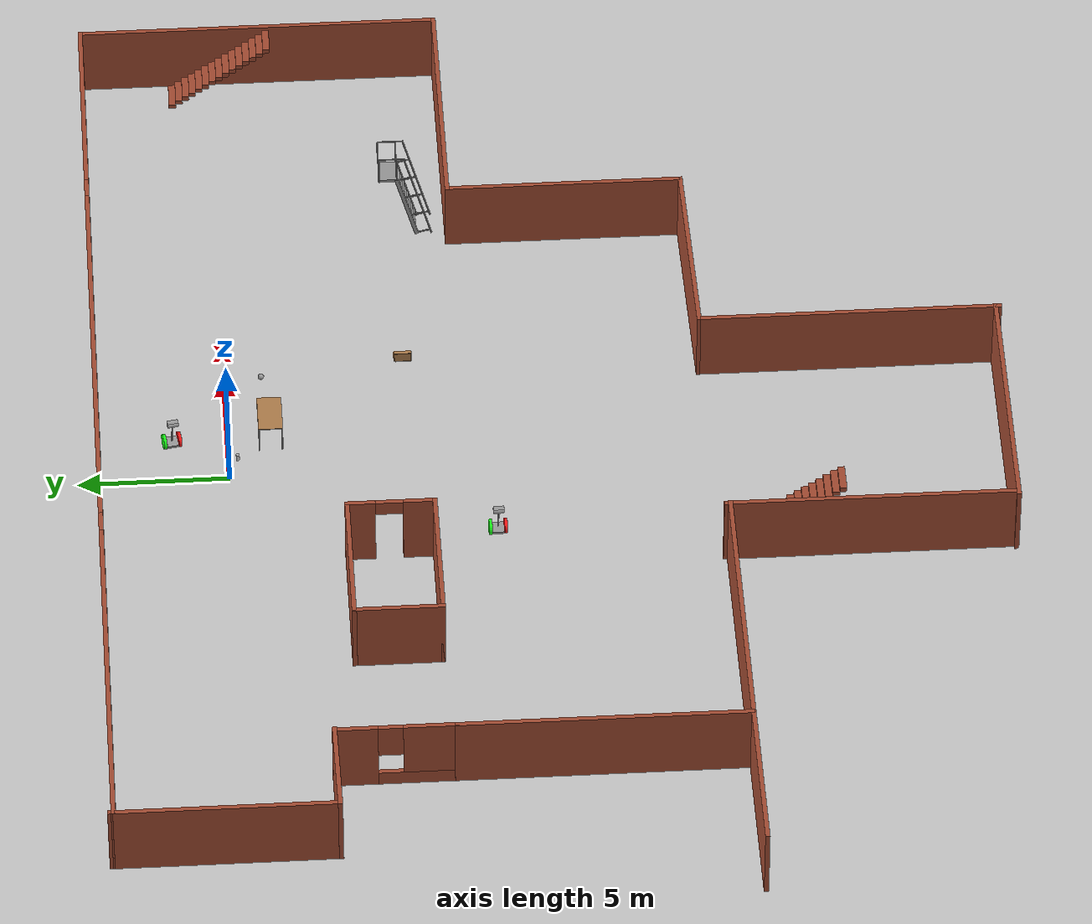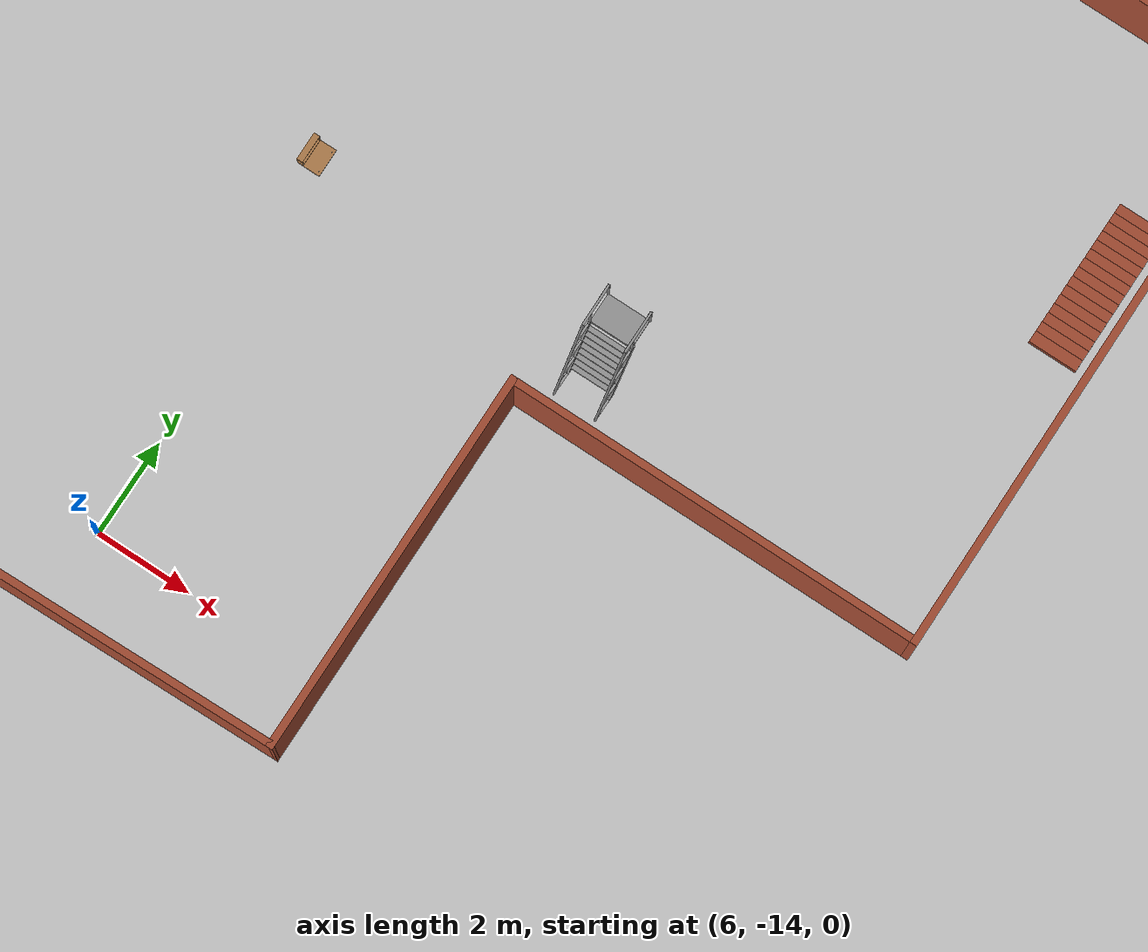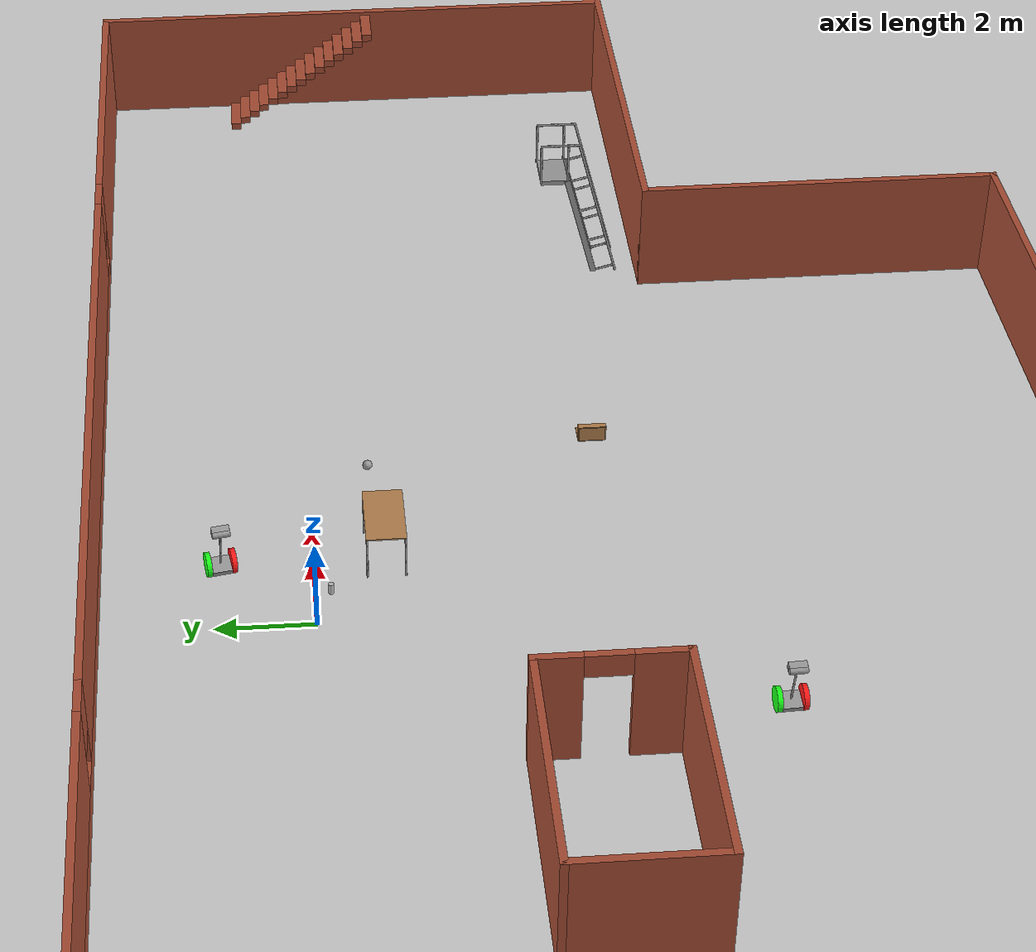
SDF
<sdf version="1.6">
 <world name="default">
  <plugin name="welcome_message" filename="libwelcome_message.so"/>
  <light name="sun" type="directional">
   <pose>0 0 10 0 -0 0</pose>
   <diffuse>0.8 0.8 0.8 1</diffuse>
   <specular>0.2 0.2 0.2 1</specular>
   <attenuation>
    <range>1000</range>
    <constant>0.9</constant>
    <linear>0.01</linear>
    <quadratic>0.001</quadratic>
   </attenuation>
   <direction>-0.5 0.1 -0.9</direction>
  </light>
  <model name="ground_plane">
   <static>1</static>
   <link name="link">
    <collision name="collision">
     <geometry><plane><normal>0 0 1</normal><size>100 100</size></plane></geometry>
     <surface><friction><ode><mu>100</mu><mu2>50</mu2></ode></friction></surface>
    </collision>
    <visual name="visual">
     <cast_shadows>0</cast_shadows>
     <geometry><plane><normal>0 0 1</normal><size>100 100</size></plane></geometry>
     <material>
      <script><uri>file://media/materials/scripts/gazebo.material</uri><name>Gazebo/Grey</name></script>
     </material>
    </visual>
   </link>
  </model>
  <gravity>0 0 -9.8</gravity>
  <magnetic_field>6e-06 2.3e-05 -4.2e-05</magnetic_field>
  <atmosphere type="adiabatic"/>
  <physics name="default_physics" default="0" type="ode">
   <max_step_size>0.001</max_step_size>
   <real_time_factor>1</real_time_factor>
   <real_time_update_rate>1000</real_time_update_rate>
  </physics>
  <scene><ambient>0.4 0.4 0.4 1</ambient><background>0.7 0.7 0.7 1</background><shadows>1</shadows></scene>
  <spherical_coordinates>
   <surface_model>EARTH_WGS84</surface_model>
   <latitude_deg>0</latitude_deg>
   <longitude_deg>0</longitude_deg>
   <elevation>0</elevation>
   <heading_deg>0</heading_deg>
  </spherical_coordinates>
  <model name="table">
   <static>1</static>
   <link name="link">
    <collision name="surface">
     <pose>0 0 1 0 -0 0</pose>
     <geometry><box><size>1.5 0.8 0.03</size></box></geometry>
     <surface><friction><ode><mu>0.6</mu><mu2>0.6</mu2></ode></friction></surface>
    </collision>
    <visual name="visual1">
     <pose>0 0 1 0 -0 0</pose>
     <geometry><box><size>1.5 0.8 0.03</size></box></geometry>
     <material>
      <script><uri>file://media/materials/scripts/gazebo.material</uri><name>Gazebo/Wood</name></script>
     </material>
    </visual>
    <collision name="front_left_leg">
     <pose>0.68 0.38 0.5 0 -0 0</pose>
     <geometry><cylinder><radius>0.02</radius><length>1</length></cylinder></geometry>
    </collision>
    <visual name="front_left_leg">
     <pose>0.68 0.38 0.5 0 -0 0</pose>
     <geometry><cylinder><radius>0.02</radius><length>1</length></cylinder></geometry>
     <material>
      <script><uri>file://media/materials/scripts/gazebo.material</uri><name>Gazebo/Grey</name></script>
     </material>
    </visual>
    <collision name="front_right_leg">
     <pose>0.68 -0.38 0.5 0 -0 0</pose>
     <geometry><cylinder><radius>0.02</radius><length>1</length></cylinder></geometry>
    </collision>
    <visual name="front_right_leg">
     <pose>0.68 -0.38 0.5 0 -0 0</pose>
     <geometry><cylinder><radius>0.02</radius><length>1</length></cylinder></geometry>
     <material>
      <script><uri>file://media/materials/scripts/gazebo.material</uri><name>Gazebo/Grey</name></script>
     </material>
    </visual>
    <collision name="back_right_leg">
     <pose>-0.68 -0.38 0.5 0 -0 0</pose>
     <geometry><cylinder><radius>0.02</radius><length>1</length></cylinder></geometry>
    </collision>
    <visual name="back_right_leg">
     <pose>-0.68 -0.38 0.5 0 -0 0</pose>
     <geometry><cylinder><radius>0.02</radius><length>1</length></cylinder></geometry>
     <material>
      <script><uri>file://media/materials/scripts/gazebo.material</uri><name>Gazebo/Grey</name></script>
     </material>
    </visual>
    <collision name="back_left_leg">
     <pose>-0.68 0.38 0.5 0 -0 0</pose>
     <geometry><cylinder><radius>0.02</radius><length>1</length></cylinder></geometry>
    </collision>
    <visual name="back_left_leg">
     <pose>-0.68 0.38 0.5 0 -0 0</pose>
     <geometry><cylinder><radius>0.02</radius><length>1</length></cylinder></geometry>
     <material>
      <script><uri>file://media/materials/scripts/gazebo.material</uri><name>Gazebo/Grey</name></script>
     </material>
    </visual>
   </link>
   <pose>1.98595 -1.41293 0 0 -0 0</pose>
  </model>
  <model name="beer">
   <link name="link">
    <pose>0 0 0.115 0 -0 0</pose>
    <inertial>
     <mass>0.39</mass>
     <inertia><ixx>0.00058</ixx><ixy>0</ixy><ixz>0</ixz><iyy>0.00058</iyy><iyz>0</iyz><izz>0.00019</izz></inertia>
    </inertial>
    <collision name="collision">
     <geometry><cylinder><radius>0.055</radius><length>0.23</length></cylinder></geometry>
    </collision>
    <visual name="visual">
     <geometry><cylinder><radius>0.055</radius><length>0.23</length></cylinder></geometry>
     <material>
      <script>
       <uri>model://beer/materials/scripts</uri>
       <uri>model://beer/materials/textures</uri>
       <name>Beer/Diffuse</name>
      </script>
     </material>
    </visual>
   </link>
   <pose>0.90067 -0.299227 -2e-06 1e-06 -0 -3e-06</pose>
  </model>
  <model name="my_ball">
   <link name="link_0">
    <inertial>
     <mass>1</mass>
     <inertia><ixx>0.1</ixx><ixy>0</ixy><ixz>0</ixz><iyy>0.1</iyy><iyz>0</iyz><izz>0.1</izz></inertia>
    </inertial>
    <visual name="visual">
     <geometry><sphere><radius>0.1</radius></sphere></geometry>
     <material>
      <lighting>1</lighting>
      <script><uri>file://media/materials/scripts/gazebo.material</uri><name>Gazebo/Grey</name></script>
      <shader type="pixel"><normal_map>__default__</normal_map></shader>
      <ambient>1 1 1 1</ambient>
      <diffuse>1 1 1 1</diffuse>
      <specular>1 1 1 1</specular>
      <emissive>1 1 1 1</emissive>
     </material>
    </visual>
    <collision name="collision">
     <geometry><sphere><radius>0.1</radius></sphere></geometry>
     <surface>
      <friction>
       <ode><mu>1</mu><mu2>1</mu2><fdir1>0 0 0</fdir1><slip1>0</slip1><slip2>0</slip2></ode>
       <torsional>
        <coefficient>1</coefficient>
        <patch_radius>0</patch_radius>
        <surface_radius>0</surface_radius>
        <use_patch_radius>1</use_patch_radius>
        <ode><slip>0</slip></ode>
       </torsional>
      </friction>
      <bounce><restitution_coefficient>0</restitution_coefficient><threshold>1e+06</threshold></bounce>
      <contact>
       <collide_without_contact>0</collide_without_contact>
       <collide_without_contact_bitmask>1</collide_without_contact_bitmask>
       <collide_bitmask>1</collide_bitmask>
       <ode>
        <soft_cfm>0</soft_cfm>
        <soft_erp>0.2</soft_erp>
        <kp>1e+13</kp>
        <kd>1</kd>
        <max_vel>0.01</max_vel>
        <min_depth>0</min_depth>
       </ode>
       <bullet>
        <split_impulse>1</split_impulse>
        <split_impulse_penetration_threshold>-0.01</split_impulse_penetration_threshold>
        <soft_cfm>0</soft_cfm>
        <soft_erp>0.2</soft_erp>
        <kp>1e+13</kp>
        <kd>1</kd>
       </bullet>
      </contact>
     </surface>
    </collision>
   </link>
   <static>0</static>
   <pose>4.71403 -1.21152 0.1 0 -0 0</pose>
  </model>
  <model name="TwoWheelBalancer">
   <link name="link_0">
    <pose>0 0 -0.35 0 -0 0</pose>
    <inertial>
     <mass>10</mass>
     <inertia>
      <ixx>0.166667</ixx>
      <ixy>0</ixy>
      <ixz>0</ixz>
      <iyy>0.166667</iyy>
      <iyz>0</iyz>
      <izz>0.166667</izz>
     </inertia>
    </inertial>
    <visual name="visual">
     <geometry><box><size>0.4 0.4 0.1</size></box></geometry>
     <material>
      <lighting>1</lighting>
      <script><uri>file://media/materials/scripts/gazebo.material</uri><name>Gazebo/Grey</name></script>
      <shader type="pixel"><normal_map>__default__</normal_map></shader>
      <ambient>0.3 0.3 0.3 1</ambient>
      <diffuse>0.7 0.7 0.7 1</diffuse>
      <specular>0.01 0.01 0.01 1</specular>
      <emissive>0 0 0 1</emissive>
     </material>
    </visual>
    <collision name="collision">
     <geometry><box><size>0.4 0.4 0.1</size></box></geometry>
     <surface>
      <friction>
       <ode><mu>1</mu><mu2>1</mu2><fdir1>0 0 0</fdir1><slip1>0</slip1><slip2>0</slip2></ode>
       <torsional>
        <coefficient>1</coefficient>
        <patch_radius>0</patch_radius>
        <surface_radius>0</surface_radius>
        <use_patch_radius>1</use_patch_radius>
        <ode><slip>0</slip></ode>
       </torsional>
      </friction>
      <bounce><restitution_coefficient>0</restitution_coefficient><threshold>1e+06</threshold></bounce>
      <contact>
       <collide_without_contact>0</collide_without_contact>
       <collide_without_contact_bitmask>1</collide_without_contact_bitmask>
       <collide_bitmask>1</collide_bitmask>
       <ode>
        <soft_cfm>0</soft_cfm>
        <soft_erp>0.2</soft_erp>
        <kp>1e+13</kp>
        <kd>1</kd>
        <max_vel>0.01</max_vel>
        <min_depth>0</min_depth>
       </ode>
       <bullet>
        <split_impulse>1</split_impulse>
        <split_impulse_penetration_threshold>-0.01</split_impulse_penetration_threshold>
        <soft_cfm>0</soft_cfm>
        <soft_erp>0.2</soft_erp>
        <kp>1e+13</kp>
        <kd>1</kd>
       </bullet>
      </contact>
     </surface>
    </collision>
   </link>
   <link name="link_1">
    <pose>0.012232 0.250024 -0.27143 0 -0 0</pose>
    <inertial>
     <mass>1</mass>
     <inertia><ixx>0.145833</ixx><ixy>0</ixy><ixz>0</ixz><iyy>0.145833</iyy><iyz>0</iyz><izz>0.125</izz></inertia>
    </inertial>
    <visual name="visual">
     <pose>0 0 0 1.5707 -0 0</pose>
     <geometry><cylinder><radius>0.25</radius><length>0.1</length></cylinder></geometry>
     <material>
      <lighting>1</lighting>
      <script><uri>file://media/materials/scripts/gazebo.material</uri><name>Gazebo/Grey</name></script>
      <shader type="pixel"><normal_map>__default__</normal_map></shader>
      <ambient>0.1 1 0.1 1</ambient>
      <diffuse>0.1 1 0.1 1</diffuse>
      <specular>0.01 0.01 0.01 1</specular>
      <emissive>0 0 0 1</emissive>
     </material>
    </visual>
    <collision name="collision">
     <pose>0 0 0 1.5707 -0 0</pose>
     <geometry><cylinder><radius>0.25</radius><length>0.1</length></cylinder></geometry>
     <surface>
      <friction>
       <ode><mu>1</mu><mu2>1</mu2><fdir1>0 0 0</fdir1><slip1>0</slip1><slip2>0</slip2></ode>
       <torsional>
        <coefficient>1</coefficient>
        <patch_radius>0</patch_radius>
        <surface_radius>0</surface_radius>
        <use_patch_radius>1</use_patch_radius>
        <ode><slip>0</slip></ode>
       </torsional>
      </friction>
      <bounce><restitution_coefficient>0</restitution_coefficient><threshold>1e+06</threshold></bounce>
      <contact>
       <collide_without_contact>0</collide_without_contact>
       <collide_without_contact_bitmask>1</collide_without_contact_bitmask>
       <collide_bitmask>1</collide_bitmask>
       <ode>
        <soft_cfm>0</soft_cfm>
        <soft_erp>0.2</soft_erp>
        <kp>1e+13</kp>
        <kd>1</kd>
        <max_vel>0.01</max_vel>
        <min_depth>0</min_depth>
       </ode>
       <bullet>
        <split_impulse>1</split_impulse>
        <split_impulse_penetration_threshold>-0.01</split_impulse_penetration_threshold>
        <soft_cfm>0</soft_cfm>
        <soft_erp>0.2</soft_erp>
        <kp>1e+13</kp>
        <kd>1</kd>
       </bullet>
      </contact>
     </surface>
    </collision>
   </link>
   <link name="link_1_clone">
    <pose>0.012232 -0.250024 -0.27143 0 -0 0</pose>
    <inertial>
     <mass>1</mass>
     <inertia><ixx>0.145833</ixx><ixy>0</ixy><ixz>0</ixz><iyy>0.145833</iyy><iyz>0</iyz><izz>0.125</izz></inertia>
    </inertial>
    <visual name="visual">
     <pose>0 0 0 1.5707 -0 0</pose>
     <geometry><cylinder><radius>0.25</radius><length>0.1</length></cylinder></geometry>
     <material>
      <lighting>1</lighting>
      <script><uri>file://media/materials/scripts/gazebo.material</uri><name>Gazebo/Grey</name></script>
      <shader type="pixel"><normal_map>__default__</normal_map></shader>
      <ambient>1 0.1 0.1 1</ambient>
      <diffuse>1 0.1 0.1 1</diffuse>
      <specular>0.01 0.01 0.01 1</specular>
      <emissive>0 0 0 1</emissive>
     </material>
    </visual>
    <collision name="collision">
     <pose>0 0 0 1.5707 -0 0</pose>
     <geometry><cylinder><radius>0.25</radius><length>0.1</length></cylinder></geometry>
     <surface>
      <friction>
       <ode><mu>1</mu><mu2>1</mu2><fdir1>0 0 0</fdir1><slip1>0</slip1><slip2>0</slip2></ode>
       <torsional>
        <coefficient>1</coefficient>
        <patch_radius>0</patch_radius>
        <surface_radius>0</surface_radius>
        <use_patch_radius>1</use_patch_radius>
        <ode><slip>0</slip></ode>
       </torsional>
      </friction>
      <bounce><restitution_coefficient>0</restitution_coefficient><threshold>1e+06</threshold></bounce>
      <contact>
       <collide_without_contact>0</collide_without_contact>
       <collide_without_contact_bitmask>1</collide_without_contact_bitmask>
       <collide_bitmask>1</collide_bitmask>
       <ode>
        <soft_cfm>0</soft_cfm>
        <soft_erp>0.2</soft_erp>
        <kp>1e+13</kp>
        <kd>1</kd>
        <max_vel>0.01</max_vel>
        <min_depth>0</min_depth>
       </ode>
       <bullet>
        <split_impulse>1</split_impulse>
        <split_impulse_penetration_threshold>-0.01</split_impulse_penetration_threshold>
        <soft_cfm>0</soft_cfm>
        <soft_erp>0.2</soft_erp>
        <kp>1e+13</kp>
        <kd>1</kd>
       </bullet>
      </contact>
     </surface>
    </collision>
   </link>
   <link name="link_2">
    <pose>0.012232 -0 -0.27143 0 -0 0</pose>
    <inertial>
     <mass>0.11</mass>
     <inertia><ixx>0.145833</ixx><ixy>0</ixy><ixz>0</ixz><iyy>0.145833</iyy><iyz>0</iyz><izz>0.125</izz></inertia>
    </inertial>
    <visual name="visual">
     <pose>0 0 0.5 0 -0 0</pose>
     <geometry><cylinder><radius>0.02</radius><length>1</length></cylinder></geometry>
     <material>
      <lighting>1</lighting>
      <script><uri>file://media/materials/scripts/gazebo.material</uri><name>Gazebo/Grey</name></script>
      <shader type="pixel"><normal_map>__default__</normal_map></shader>
      <ambient>0.3 0.3 0.3 1</ambient>
      <diffuse>0.7 0.7 0.7 1</diffuse>
      <specular>0.01 0.01 0.01 1</specular>
      <emissive>0 0 0 1</emissive>
     </material>
    </visual>
    <collision name="collision">
     <pose>0 0 0.5 0 -0 0</pose>
     <geometry><cylinder><radius>0.02</radius><length>1</length></cylinder></geometry>
     <surface>
      <friction>
       <ode><mu>1</mu><mu2>1</mu2><fdir1>0 0 0</fdir1><slip1>0</slip1><slip2>0</slip2></ode>
       <torsional>
        <coefficient>1</coefficient>
        <patch_radius>0</patch_radius>
        <surface_radius>0</surface_radius>
        <use_patch_radius>1</use_patch_radius>
        <ode><slip>0</slip></ode>
       </torsional>
      </friction>
      <bounce><restitution_coefficient>0</restitution_coefficient><threshold>1e+06</threshold></bounce>
      <contact>
       <collide_without_contact>0</collide_without_contact>
       <collide_without_contact_bitmask>1</collide_without_contact_bitmask>
       <collide_bitmask>1</collide_bitmask>
       <ode>
        <soft_cfm>0</soft_cfm>
        <soft_erp>0.2</soft_erp>
        <kp>1e+13</kp>
        <kd>1</kd>
        <max_vel>0.01</max_vel>
        <min_depth>0</min_depth>
       </ode>
       <bullet>
        <split_impulse>1</split_impulse>
        <split_impulse_penetration_threshold>-0.01</split_impulse_penetration_threshold>
        <soft_cfm>0</soft_cfm>
        <soft_erp>0.2</soft_erp>
        <kp>1e+13</kp>
        <kd>1</kd>
       </bullet>
      </contact>
     </surface>
    </collision>
   </link>
   <link name="link_3">
    <pose>0.012232 -0 0.728572 0 -0 0</pose>
    <inertial>
     <mass>0.1</mass>
     <inertia>
      <ixx>0.166667</ixx>
      <ixy>0</ixy>
      <ixz>0</ixz>
      <iyy>0.166667</iyy>
      <iyz>0</iyz>
      <izz>0.166667</izz>
     </inertia>
    </inertial>
    <visual name="visual">
     <geometry><box><size>0.15 0.35 0.15</size></box></geometry>
     <material>
      <lighting>1</lighting>
      <script><uri>file://media/materials/scripts/gazebo.material</uri><name>Gazebo/Grey</name></script>
      <shader type="pixel"><normal_map>__default__</normal_map></shader>
      <ambient>0.3 0.3 0.3 1</ambient>
      <diffuse>0.7 0.7 0.7 1</diffuse>
      <specular>0.01 0.01 0.01 1</specular>
      <emissive>0 0 0 1</emissive>
     </material>
    </visual>
    <collision name="collision">
     <geometry><box><size>0.15 0.35 0.15</size></box></geometry>
     <surface>
      <friction>
       <ode><mu>1</mu><mu2>1</mu2><fdir1>0 0 0</fdir1><slip1>0</slip1><slip2>0</slip2></ode>
       <torsional>
        <coefficient>1</coefficient>
        <patch_radius>0</patch_radius>
        <surface_radius>0</surface_radius>
        <use_patch_radius>1</use_patch_radius>
        <ode><slip>0</slip></ode>
       </torsional>
      </friction>
      <bounce><restitution_coefficient>0</restitution_coefficient><threshold>1e+06</threshold></bounce>
      <contact>
       <collide_without_contact>0</collide_without_contact>
       <collide_without_contact_bitmask>1</collide_without_contact_bitmask>
       <collide_bitmask>1</collide_bitmask>
       <ode>
        <soft_cfm>0</soft_cfm>
        <soft_erp>0.2</soft_erp>
        <kp>1e+13</kp>
        <kd>1</kd>
        <max_vel>0.01</max_vel>
        <min_depth>0</min_depth>
       </ode>
       <bullet>
        <split_impulse>1</split_impulse>
        <split_impulse_penetration_threshold>-0.01</split_impulse_penetration_threshold>
        <soft_cfm>0</soft_cfm>
        <soft_erp>0.2</soft_erp>
        <kp>1e+13</kp>
        <kd>1</kd>
       </bullet>
      </contact>
     </surface>
    </collision>
   </link>
   <link name="link_5">
    <pose>0.092232 -0.12 0.728571 0 -0 0</pose>
    <inertial>
     <mass>0.1</mass>
     <inertia><ixx>0.145833</ixx><ixy>0</ixy><ixz>0</ixz><iyy>0.145833</iyy><iyz>0</iyz><izz>0.125</izz></inertia>
    </inertial>
    <visual name="visual">
     <pose>0 0 0 0 1.5707 0</pose>
     <geometry><cylinder><radius>0.025</radius><length>0.02</length></cylinder></geometry>
     <material>
      <lighting>1</lighting>
      <script><uri>file://media/materials/scripts/gazebo.material</uri><name>Gazebo/Grey</name></script>
      <shader type="pixel"><normal_map>__default__</normal_map></shader>
      <ambient>0 0 0 1</ambient>
      <diffuse>0 0 0 1</diffuse>
      <specular>0.01 0.01 0.01 1</specular>
      <emissive>0 0 0 1</emissive>
     </material>
    </visual>
    <collision name="collision">
     <geometry><cylinder><radius>0.025</radius><length>0.02</length></cylinder></geometry>
     <surface>
      <friction>
       <ode><mu>1</mu><mu2>1</mu2><fdir1>0 0 0</fdir1><slip1>0</slip1><slip2>0</slip2></ode>
       <torsional>
        <coefficient>1</coefficient>
        <patch_radius>0</patch_radius>
        <surface_radius>0</surface_radius>
        <use_patch_radius>1</use_patch_radius>
        <ode><slip>0</slip></ode>
       </torsional>
      </friction>
      <bounce><restitution_coefficient>0</restitution_coefficient><threshold>1e+06</threshold></bounce>
      <contact>
       <collide_without_contact>0</collide_without_contact>
       <collide_without_contact_bitmask>1</collide_without_contact_bitmask>
       <collide_bitmask>1</collide_bitmask>
       <ode>
        <soft_cfm>0</soft_cfm>
        <soft_erp>0.2</soft_erp>
        <kp>1e+13</kp>
        <kd>1</kd>
        <max_vel>0.01</max_vel>
        <min_depth>0</min_depth>
       </ode>
       <bullet>
        <split_impulse>1</split_impulse>
        <split_impulse_penetration_threshold>-0.01</split_impulse_penetration_threshold>
        <soft_cfm>0</soft_cfm>
        <soft_erp>0.2</soft_erp>
        <kp>1e+13</kp>
        <kd>1</kd>
       </bullet>
      </contact>
     </surface>
    </collision>
   </link>
   <link name="link_5_clone">
    <pose>0.092232 0.12 0.728571 0 -0 0</pose>
    <inertial>
     <mass>0.1</mass>
     <inertia><ixx>0.145833</ixx><ixy>0</ixy><ixz>0</ixz><iyy>0.145833</iyy><iyz>0</iyz><izz>0.125</izz></inertia>
    </inertial>
    <visual name="visual">
     <pose>0 0 0 0 1.5707 0</pose>
     <geometry><cylinder><radius>0.025</radius><length>0.02</length></cylinder></geometry>
     <material>
      <lighting>1</lighting>
      <script><uri>file://media/materials/scripts/gazebo.material</uri><name>Gazebo/Grey</name></script>
      <shader type="pixel"><normal_map>__default__</normal_map></shader>
      <ambient>0 0 0 1</ambient>
      <diffuse>0 0 0 1</diffuse>
      <specular>0.01 0.01 0.01 1</specular>
      <emissive>0 0 0 1</emissive>
     </material>
    </visual>
    <collision name="collision">
     <geometry><cylinder><radius>0.025</radius><length>0.02</length></cylinder></geometry>
     <surface>
      <friction>
       <ode><mu>1</mu><mu2>1</mu2><fdir1>0 0 0</fdir1><slip1>0</slip1><slip2>0</slip2></ode>
       <torsional>
        <coefficient>1</coefficient>
        <patch_radius>0</patch_radius>
        <surface_radius>0</surface_radius>
        <use_patch_radius>1</use_patch_radius>
        <ode><slip>0</slip></ode>
       </torsional>
      </friction>
      <bounce><restitution_coefficient>0</restitution_coefficient><threshold>1e+06</threshold></bounce>
      <contact>
       <collide_without_contact>0</collide_without_contact>
       <collide_without_contact_bitmask>1</collide_without_contact_bitmask>
       <collide_bitmask>1</collide_bitmask>
       <ode>
        <soft_cfm>0</soft_cfm>
        <soft_erp>0.2</soft_erp>
        <kp>1e+13</kp>
        <kd>1</kd>
        <max_vel>0.01</max_vel>
        <min_depth>0</min_depth>
       </ode>
       <bullet>
        <split_impulse>1</split_impulse>
        <split_impulse_penetration_threshold>-0.01</split_impulse_penetration_threshold>
        <soft_cfm>0</soft_cfm>
        <soft_erp>0.2</soft_erp>
        <kp>1e+13</kp>
        <kd>1</kd>
       </bullet>
      </contact>
     </surface>
    </collision>
   </link>
   <link name="link_6">
    <pose>-0.062768 -0 0.728572 1.57079 -0 0</pose>
    <inertial>
     <mass>0.1</mass>
     <inertia><ixx>0.145833</ixx><ixy>0</ixy><ixz>0</ixz><iyy>0.145833</iyy><iyz>0</iyz><izz>0.125</izz></inertia>
    </inertial>
    <visual name="visual">
     <geometry><cylinder><radius>0.075</radius><length>0.35</length></cylinder></geometry>
     <material>
      <lighting>1</lighting>
      <script><uri>file://media/materials/scripts/gazebo.material</uri><name>Gazebo/Grey</name></script>
      <shader type="pixel"><normal_map>__default__</normal_map></shader>
      <ambient>0.3 0.3 0.3 1</ambient>
      <diffuse>0.7 0.7 0.7 1</diffuse>
      <specular>0.01 0.01 0.01 1</specular>
      <emissive>0 0 0 1</emissive>
     </material>
    </visual>
    <collision name="collision">
     <geometry><cylinder><radius>0.075</radius><length>0.35</length></cylinder></geometry>
     <surface>
      <friction>
       <ode><mu>1</mu><mu2>1</mu2><fdir1>0 0 0</fdir1><slip1>0</slip1><slip2>0</slip2></ode>
       <torsional>
        <coefficient>1</coefficient>
        <patch_radius>0</patch_radius>
        <surface_radius>0</surface_radius>
        <use_patch_radius>1</use_patch_radius>
        <ode><slip>0</slip></ode>
       </torsional>
      </friction>
      <bounce><restitution_coefficient>0</restitution_coefficient><threshold>1e+06</threshold></bounce>
      <contact>
       <collide_without_contact>0</collide_without_contact>
       <collide_without_contact_bitmask>1</collide_without_contact_bitmask>
       <collide_bitmask>1</collide_bitmask>
       <ode>
        <soft_cfm>0</soft_cfm>
        <soft_erp>0.2</soft_erp>
        <kp>1e+13</kp>
        <kd>1</kd>
        <max_vel>0.01</max_vel>
        <min_depth>0</min_depth>
       </ode>
       <bullet>
        <split_impulse>1</split_impulse>
        <split_impulse_penetration_threshold>-0.01</split_impulse_penetration_threshold>
        <soft_cfm>0</soft_cfm>
        <soft_erp>0.2</soft_erp>
        <kp>1e+13</kp>
        <kd>1</kd>
       </bullet>
      </contact>
     </surface>
    </collision>
   </link>
   <joint name="link_0_JOINT_0" type="revolute">
    <parent>link_0</parent>
    <child>link_1</child>
    <axis>
     <xyz>0 1 0</xyz>
     <use_parent_model_frame>0</use_parent_model_frame>
     <limit>
      <lower>-1.79769e+308</lower>
      <upper>1.79769e+308</upper>
      <effort>-1</effort>
      <velocity>-1</velocity>
     </limit>
     <dynamics>
      <spring_reference>0</spring_reference>
      <spring_stiffness>0</spring_stiffness>
      <damping>0</damping>
      <friction>0</friction>
     </dynamics>
    </axis>
    <physics>
     <ode><limit><cfm>0</cfm><erp>0.2</erp></limit><suspension><cfm>0</cfm><erp>0.2</erp></suspension></ode>
    </physics>
   </joint>
   <joint name="link_0_JOINT_1" type="revolute">
    <parent>link_0</parent>
    <child>link_1_clone</child>
    <axis>
     <xyz>0 1 0</xyz>
     <use_parent_model_frame>0</use_parent_model_frame>
     <limit>
      <lower>-1.79769e+308</lower>
      <upper>1.79769e+308</upper>
      <effort>-1</effort>
      <velocity>-1</velocity>
     </limit>
     <dynamics>
      <spring_reference>0</spring_reference>
      <spring_stiffness>0</spring_stiffness>
      <damping>0</damping>
      <friction>0</friction>
     </dynamics>
    </axis>
    <physics>
     <ode><limit><cfm>0</cfm><erp>0.2</erp></limit><suspension><cfm>0</cfm><erp>0.2</erp></suspension></ode>
    </physics>
   </joint>
   <joint name="link_0_JOINT_2" type="fixed">
    <parent>link_0</parent>
    <child>link_2</child>
    <physics>
     <ode><limit><cfm>0</cfm><erp>0.2</erp></limit><suspension><cfm>0</cfm><erp>0.2</erp></suspension></ode>
    </physics>
   </joint>
   <joint name="link_2_JOINT_3" type="fixed">
    <parent>link_2</parent>
    <child>link_3</child>
    <physics>
     <ode><limit><cfm>0</cfm><erp>0.2</erp></limit><suspension><cfm>0</cfm><erp>0.2</erp></suspension></ode>
    </physics>
   </joint>
   <joint name="link_3_JOINT_4" type="fixed">
    <parent>link_3</parent>
    <child>link_5</child>
    <physics>
     <ode><limit><cfm>0</cfm><erp>0.2</erp></limit><suspension><cfm>0</cfm><erp>0.2</erp></suspension></ode>
    </physics>
   </joint>
   <joint name="link_3_JOINT_5" type="fixed">
    <parent>link_3</parent>
    <child>link_5_clone</child>
    <physics>
     <ode><limit><cfm>0</cfm><erp>0.2</erp></limit><suspension><cfm>0</cfm><erp>0.2</erp></suspension></ode>
    </physics>
   </joint>
   <joint name="link_3_JOINT_6" type="fixed">
    <parent>link_3</parent>
    <child>link_6</child>
    <physics>
     <ode><limit><cfm>0</cfm><erp>0.2</erp></limit><suspension><cfm>0</cfm><erp>0.2</erp></suspension></ode>
    </physics>
   </joint>
   <static>0</static>
   <pose>1.61814 1.82601 0.51272 1e-06 -0.212864 0.180787</pose>
  </model>
  <model name="TwoWheelBalancer_0">
   <link name="link_0">
    <pose>0 0 -0.35 0 -0 0</pose>
    <inertial>
     <mass>10</mass>
     <inertia>
      <ixx>0.166667</ixx>
      <ixy>0</ixy>
      <ixz>0</ixz>
      <iyy>0.166667</iyy>
      <iyz>0</iyz>
      <izz>0.166667</izz>
     </inertia>
    </inertial>
    <visual name="visual">
     <geometry><box><size>0.4 0.4 0.1</size></box></geometry>
     <material>
      <lighting>1</lighting>
      <script><uri>file://media/materials/scripts/gazebo.material</uri><name>Gazebo/Grey</name></script>
      <shader type="pixel"><normal_map>__default__</normal_map></shader>
      <ambient>0.3 0.3 0.3 1</ambient>
      <diffuse>0.7 0.7 0.7 1</diffuse>
      <specular>0.01 0.01 0.01 1</specular>
      <emissive>0 0 0 1</emissive>
     </material>
    </visual>
    <collision name="collision">
     <geometry><box><size>0.4 0.4 0.1</size></box></geometry>
     <surface>
      <friction>
       <ode><mu>1</mu><mu2>1</mu2><fdir1>0 0 0</fdir1><slip1>0</slip1><slip2>0</slip2></ode>
       <torsional>
        <coefficient>1</coefficient>
        <patch_radius>0</patch_radius>
        <surface_radius>0</surface_radius>
        <use_patch_radius>1</use_patch_radius>
        <ode><slip>0</slip></ode>
       </torsional>
      </friction>
      <bounce><restitution_coefficient>0</restitution_coefficient><threshold>1e+06</threshold></bounce>
      <contact>
       <collide_without_contact>0</collide_without_contact>
       <collide_without_contact_bitmask>1</collide_without_contact_bitmask>
       <collide_bitmask>1</collide_bitmask>
       <ode>
        <soft_cfm>0</soft_cfm>
        <soft_erp>0.2</soft_erp>
        <kp>1e+13</kp>
        <kd>1</kd>
        <max_vel>0.01</max_vel>
        <min_depth>0</min_depth>
       </ode>
       <bullet>
        <split_impulse>1</split_impulse>
        <split_impulse_penetration_threshold>-0.01</split_impulse_penetration_threshold>
        <soft_cfm>0</soft_cfm>
        <soft_erp>0.2</soft_erp>
        <kp>1e+13</kp>
        <kd>1</kd>
       </bullet>
      </contact>
     </surface>
    </collision>
   </link>
   <link name="link_1">
    <pose>0.012232 0.250024 -0.27143 0 -0 0</pose>
    <inertial>
     <mass>1</mass>
     <inertia><ixx>0.145833</ixx><ixy>0</ixy><ixz>0</ixz><iyy>0.145833</iyy><iyz>0</iyz><izz>0.125</izz></inertia>
    </inertial>
    <visual name="visual">
     <pose>0 0 0 1.5707 -0 0</pose>
     <geometry><cylinder><radius>0.25</radius><length>0.1</length></cylinder></geometry>
     <material>
      <lighting>1</lighting>
      <script><uri>file://media/materials/scripts/gazebo.material</uri><name>Gazebo/Grey</name></script>
      <shader type="pixel"><normal_map>__default__</normal_map></shader>
      <ambient>0.1 1 0.1 1</ambient>
      <diffuse>0.1 1 0.1 1</diffuse>
      <specular>0.01 0.01 0.01 1</specular>
      <emissive>0 0 0 1</emissive>
     </material>
    </visual>
    <collision name="collision">
     <pose>0 0 0 1.5707 -0 0</pose>
     <geometry><cylinder><radius>0.25</radius><length>0.1</length></cylinder></geometry>
     <surface>
      <friction>
       <ode><mu>1</mu><mu2>1</mu2><fdir1>0 0 0</fdir1><slip1>0</slip1><slip2>0</slip2></ode>
       <torsional>
        <coefficient>1</coefficient>
        <patch_radius>0</patch_radius>
        <surface_radius>0</surface_radius>
        <use_patch_radius>1</use_patch_radius>
        <ode><slip>0</slip></ode>
       </torsional>
      </friction>
      <bounce><restitution_coefficient>0</restitution_coefficient><threshold>1e+06</threshold></bounce>
      <contact>
       <collide_without_contact>0</collide_without_contact>
       <collide_without_contact_bitmask>1</collide_without_contact_bitmask>
       <collide_bitmask>1</collide_bitmask>
       <ode>
        <soft_cfm>0</soft_cfm>
        <soft_erp>0.2</soft_erp>
        <kp>1e+13</kp>
        <kd>1</kd>
        <max_vel>0.01</max_vel>
        <min_depth>0</min_depth>
       </ode>
       <bullet>
        <split_impulse>1</split_impulse>
        <split_impulse_penetration_threshold>-0.01</split_impulse_penetration_threshold>
        <soft_cfm>0</soft_cfm>
        <soft_erp>0.2</soft_erp>
        <kp>1e+13</kp>
        <kd>1</kd>
       </bullet>
      </contact>
     </surface>
    </collision>
   </link>
   <link name="link_1_clone">
    <pose>0.012232 -0.250024 -0.27143 0 -0 0</pose>
    <inertial>
     <mass>1</mass>
     <inertia><ixx>0.145833</ixx><ixy>0</ixy><ixz>0</ixz><iyy>0.145833</iyy><iyz>0</iyz><izz>0.125</izz></inertia>
    </inertial>
    <visual name="visual">
     <pose>0 0 0 1.5707 -0 0</pose>
     <geometry><cylinder><radius>0.25</radius><length>0.1</length></cylinder></geometry>
     <material>
      <lighting>1</lighting>
      <script><uri>file://media/materials/scripts/gazebo.material</uri><name>Gazebo/Grey</name></script>
      <shader type="pixel"><normal_map>__default__</normal_map></shader>
      <ambient>1 0.1 0.1 1</ambient>
      <diffuse>1 0.1 0.1 1</diffuse>
      <specular>0.01 0.01 0.01 1</specular>
      <emissive>0 0 0 1</emissive>
     </material>
    </visual>
    <collision name="collision">
     <pose>0 0 0 1.5707 -0 0</pose>
     <geometry><cylinder><radius>0.25</radius><length>0.1</length></cylinder></geometry>
     <surface>
      <friction>
       <ode><mu>1</mu><mu2>1</mu2><fdir1>0 0 0</fdir1><slip1>0</slip1><slip2>0</slip2></ode>
       <torsional>
        <coefficient>1</coefficient>
        <patch_radius>0</patch_radius>
        <surface_radius>0</surface_radius>
        <use_patch_radius>1</use_patch_radius>
        <ode><slip>0</slip></ode>
       </torsional>
      </friction>
      <bounce><restitution_coefficient>0</restitution_coefficient><threshold>1e+06</threshold></bounce>
      <contact>
       <collide_without_contact>0</collide_without_contact>
       <collide_without_contact_bitmask>1</collide_without_contact_bitmask>
       <collide_bitmask>1</collide_bitmask>
       <ode>
        <soft_cfm>0</soft_cfm>
        <soft_erp>0.2</soft_erp>
        <kp>1e+13</kp>
        <kd>1</kd>
        <max_vel>0.01</max_vel>
        <min_depth>0</min_depth>
       </ode>
       <bullet>
        <split_impulse>1</split_impulse>
        <split_impulse_penetration_threshold>-0.01</split_impulse_penetration_threshold>
        <soft_cfm>0</soft_cfm>
        <soft_erp>0.2</soft_erp>
        <kp>1e+13</kp>
        <kd>1</kd>
       </bullet>
      </contact>
     </surface>
    </collision>
   </link>
   <link name="link_2">
    <pose>0.012232 -0 -0.27143 0 -0 0</pose>
    <inertial>
     <mass>0.1</mass>
     <inertia><ixx>0.145833</ixx><ixy>0</ixy><ixz>0</ixz><iyy>0.145833</iyy><iyz>0</iyz><izz>0.125</izz></inertia>
    </inertial>
    <visual name="visual">
     <pose>0 0 0.5 0 -0 0</pose>
     <geometry><cylinder><radius>0.02</radius><length>1</length></cylinder></geometry>
     <material>
      <lighting>1</lighting>
      <script><uri>file://media/materials/scripts/gazebo.material</uri><name>Gazebo/Grey</name></script>
      <shader type="pixel"><normal_map>__default__</normal_map></shader>
      <ambient>0.3 0.3 0.3 1</ambient>
      <diffuse>0.7 0.7 0.7 1</diffuse>
      <specular>0.01 0.01 0.01 1</specular>
      <emissive>0 0 0 1</emissive>
     </material>
    </visual>
    <collision name="collision">
     <pose>0 0 0.5 0 -0 0</pose>
     <geometry><cylinder><radius>0.02</radius><length>1</length></cylinder></geometry>
     <surface>
      <friction>
       <ode><mu>1</mu><mu2>1</mu2><fdir1>0 0 0</fdir1><slip1>0</slip1><slip2>0</slip2></ode>
       <torsional>
        <coefficient>1</coefficient>
        <patch_radius>0</patch_radius>
        <surface_radius>0</surface_radius>
        <use_patch_radius>1</use_patch_radius>
        <ode><slip>0</slip></ode>
       </torsional>
      </friction>
      <bounce><restitution_coefficient>0</restitution_coefficient><threshold>1e+06</threshold></bounce>
      <contact>
       <collide_without_contact>0</collide_without_contact>
       <collide_without_contact_bitmask>1</collide_without_contact_bitmask>
       <collide_bitmask>1</collide_bitmask>
       <ode>
        <soft_cfm>0</soft_cfm>
        <soft_erp>0.2</soft_erp>
        <kp>1e+13</kp>
        <kd>1</kd>
        <max_vel>0.01</max_vel>
        <min_depth>0</min_depth>
       </ode>
       <bullet>
        <split_impulse>1</split_impulse>
        <split_impulse_penetration_threshold>-0.01</split_impulse_penetration_threshold>
        <soft_cfm>0</soft_cfm>
        <soft_erp>0.2</soft_erp>
        <kp>1e+13</kp>
        <kd>1</kd>
       </bullet>
      </contact>
     </surface>
    </collision>
   </link>
   <link name="link_3">
    <pose>0.012232 -0 0.728572 0 -0 0</pose>
    <inertial>
     <mass>0.1</mass>
     <inertia>
      <ixx>0.166667</ixx>
      <ixy>0</ixy>
      <ixz>0</ixz>
      <iyy>0.166667</iyy>
      <iyz>0</iyz>
      <izz>0.166667</izz>
     </inertia>
    </inertial>
    <visual name="visual">
     <geometry><box><size>0.15 0.35 0.15</size></box></geometry>
     <material>
      <lighting>1</lighting>
      <script><uri>file://media/materials/scripts/gazebo.material</uri><name>Gazebo/Grey</name></script>
      <shader type="pixel"><normal_map>__default__</normal_map></shader>
      <ambient>0.3 0.3 0.3 1</ambient>
      <diffuse>0.7 0.7 0.7 1</diffuse>
      <specular>0.01 0.01 0.01 1</specular>
      <emissive>0 0 0 1</emissive>
     </material>
    </visual>
    <collision name="collision">
     <geometry><box><size>0.15 0.35 0.15</size></box></geometry>
     <surface>
      <friction>
       <ode><mu>1</mu><mu2>1</mu2><fdir1>0 0 0</fdir1><slip1>0</slip1><slip2>0</slip2></ode>
       <torsional>
        <coefficient>1</coefficient>
        <patch_radius>0</patch_radius>
        <surface_radius>0</surface_radius>
        <use_patch_radius>1</use_patch_radius>
        <ode><slip>0</slip></ode>
       </torsional>
      </friction>
      <bounce><restitution_coefficient>0</restitution_coefficient><threshold>1e+06</threshold></bounce>
      <contact>
       <collide_without_contact>0</collide_without_contact>
       <collide_without_contact_bitmask>1</collide_without_contact_bitmask>
       <collide_bitmask>1</collide_bitmask>
       <ode>
        <soft_cfm>0</soft_cfm>
        <soft_erp>0.2</soft_erp>
        <kp>1e+13</kp>
        <kd>1</kd>
        <max_vel>0.01</max_vel>
        <min_depth>0</min_depth>
       </ode>
       <bullet>
        <split_impulse>1</split_impulse>
        <split_impulse_penetration_threshold>-0.01</split_impulse_penetration_threshold>
        <soft_cfm>0</soft_cfm>
        <soft_erp>0.2</soft_erp>
        <kp>1e+13</kp>
        <kd>1</kd>
       </bullet>
      </contact>
     </surface>
    </collision>
   </link>
   <link name="link_5">
    <pose>0.092232 -0.12 0.728571 0 -0 0</pose>
    <inertial>
     <mass>0.1</mass>
     <inertia><ixx>0.145833</ixx><ixy>0</ixy><ixz>0</ixz><iyy>0.145833</iyy><iyz>0</iyz><izz>0.125</izz></inertia>
    </inertial>
    <visual name="visual">
     <pose>0 0 0 0 1.5707 0</pose>
     <geometry><cylinder><radius>0.025</radius><length>0.02</length></cylinder></geometry>
     <material>
      <lighting>1</lighting>
      <script><uri>file://media/materials/scripts/gazebo.material</uri><name>Gazebo/Grey</name></script>
      <shader type="pixel"><normal_map>__default__</normal_map></shader>
      <ambient>0 0 0 1</ambient>
      <diffuse>0 0 0 1</diffuse>
      <specular>0.01 0.01 0.01 1</specular>
      <emissive>0 0 0 1</emissive>
     </material>
    </visual>
    <collision name="collision">
     <geometry><cylinder><radius>0.025</radius><length>0.02</length></cylinder></geometry>
     <surface>
      <friction>
       <ode><mu>1</mu><mu2>1</mu2><fdir1>0 0 0</fdir1><slip1>0</slip1><slip2>0</slip2></ode>
       <torsional>
        <coefficient>1</coefficient>
        <patch_radius>0</patch_radius>
        <surface_radius>0</surface_radius>
        <use_patch_radius>1</use_patch_radius>
        <ode><slip>0</slip></ode>
       </torsional>
      </friction>
      <bounce><restitution_coefficient>0</restitution_coefficient><threshold>1e+06</threshold></bounce>
      <contact>
       <collide_without_contact>0</collide_without_contact>
       <collide_without_contact_bitmask>1</collide_without_contact_bitmask>
       <collide_bitmask>1</collide_bitmask>
       <ode>
        <soft_cfm>0</soft_cfm>
        <soft_erp>0.2</soft_erp>
        <kp>1e+13</kp>
        <kd>1</kd>
        <max_vel>0.01</max_vel>
        <min_depth>0</min_depth>
       </ode>
       <bullet>
        <split_impulse>1</split_impulse>
        <split_impulse_penetration_threshold>-0.01</split_impulse_penetration_threshold>
        <soft_cfm>0</soft_cfm>
        <soft_erp>0.2</soft_erp>
        <kp>1e+13</kp>
        <kd>1</kd>
       </bullet>
      </contact>
     </surface>
    </collision>
   </link>
   <link name="link_5_clone">
    <pose>0.092232 0.12 0.728571 0 -0 0</pose>
    <inertial>
     <mass>0.1</mass>
     <inertia><ixx>0.145833</ixx><ixy>0</ixy><ixz>0</ixz><iyy>0.145833</iyy><iyz>0</iyz><izz>0.125</izz></inertia>
    </inertial>
    <visual name="visual">
     <pose>0 0 0 0 1.5707 0</pose>
     <geometry><cylinder><radius>0.025</radius><length>0.02</length></cylinder></geometry>
     <material>
      <lighting>1</lighting>
      <script><uri>file://media/materials/scripts/gazebo.material</uri><name>Gazebo/Grey</name></script>
      <shader type="pixel"><normal_map>__default__</normal_map></shader>
      <ambient>0 0 0 1</ambient>
      <diffuse>0 0 0 1</diffuse>
      <specular>0.01 0.01 0.01 1</specular>
      <emissive>0 0 0 1</emissive>
     </material>
    </visual>
    <collision name="collision">
     <geometry><cylinder><radius>0.025</radius><length>0.02</length></cylinder></geometry>
     <surface>
      <friction>
       <ode><mu>1</mu><mu2>1</mu2><fdir1>0 0 0</fdir1><slip1>0</slip1><slip2>0</slip2></ode>
       <torsional>
        <coefficient>1</coefficient>
        <patch_radius>0</patch_radius>
        <surface_radius>0</surface_radius>
        <use_patch_radius>1</use_patch_radius>
        <ode><slip>0</slip></ode>
       </torsional>
      </friction>
      <bounce><restitution_coefficient>0</restitution_coefficient><threshold>1e+06</threshold></bounce>
      <contact>
       <collide_without_contact>0</collide_without_contact>
       <collide_without_contact_bitmask>1</collide_without_contact_bitmask>
       <collide_bitmask>1</collide_bitmask>
       <ode>
        <soft_cfm>0</soft_cfm>
        <soft_erp>0.2</soft_erp>
        <kp>1e+13</kp>
        <kd>1</kd>
        <max_vel>0.01</max_vel>
        <min_depth>0</min_depth>
       </ode>
       <bullet>
        <split_impulse>1</split_impulse>
        <split_impulse_penetration_threshold>-0.01</split_impulse_penetration_threshold>
        <soft_cfm>0</soft_cfm>
        <soft_erp>0.2</soft_erp>
        <kp>1e+13</kp>
        <kd>1</kd>
       </bullet>
      </contact>
     </surface>
    </collision>
   </link>
   <link name="link_6">
    <pose>-0.062768 -0 0.728572 1.57079 -0 0</pose>
    <inertial>
     <mass>0.1</mass>
     <inertia><ixx>0.145833</ixx><ixy>0</ixy><ixz>0</ixz><iyy>0.145833</iyy><iyz>0</iyz><izz>0.125</izz></inertia>
    </inertial>
    <visual name="visual">
     <geometry><cylinder><radius>0.075</radius><length>0.35</length></cylinder></geometry>
     <material>
      <lighting>1</lighting>
      <script><uri>file://media/materials/scripts/gazebo.material</uri><name>Gazebo/Grey</name></script>
      <shader type="pixel"><normal_map>__default__</normal_map></shader>
      <ambient>0.3 0.3 0.3 1</ambient>
      <diffuse>0.7 0.7 0.7 1</diffuse>
      <specular>0.01 0.01 0.01 1</specular>
      <emissive>0 0 0 1</emissive>
     </material>
    </visual>
    <collision name="collision">
     <geometry><cylinder><radius>0.075</radius><length>0.35</length></cylinder></geometry>
     <surface>
      <friction>
       <ode><mu>1</mu><mu2>1</mu2><fdir1>0 0 0</fdir1><slip1>0</slip1><slip2>0</slip2></ode>
       <torsional>
        <coefficient>1</coefficient>
        <patch_radius>0</patch_radius>
        <surface_radius>0</surface_radius>
        <use_patch_radius>1</use_patch_radius>
        <ode><slip>0</slip></ode>
       </torsional>
      </friction>
      <bounce><restitution_coefficient>0</restitution_coefficient><threshold>1e+06</threshold></bounce>
      <contact>
       <collide_without_contact>0</collide_without_contact>
       <collide_without_contact_bitmask>1</collide_without_contact_bitmask>
       <collide_bitmask>1</collide_bitmask>
       <ode>
        <soft_cfm>0</soft_cfm>
        <soft_erp>0.2</soft_erp>
        <kp>1e+13</kp>
        <kd>1</kd>
        <max_vel>0.01</max_vel>
        <min_depth>0</min_depth>
       </ode>
       <bullet>
        <split_impulse>1</split_impulse>
        <split_impulse_penetration_threshold>-0.01</split_impulse_penetration_threshold>
        <soft_cfm>0</soft_cfm>
        <soft_erp>0.2</soft_erp>
        <kp>1e+13</kp>
        <kd>1</kd>
       </bullet>
      </contact>
     </surface>
    </collision>
   </link>
   <joint name="link_0_JOINT_0" type="revolute">
    <parent>link_0</parent>
    <child>link_1</child>
    <axis>
     <xyz>0 1 0</xyz>
     <use_parent_model_frame>0</use_parent_model_frame>
     <limit>
      <lower>-1.79769e+308</lower>
      <upper>1.79769e+308</upper>
      <effort>-1</effort>
      <velocity>-1</velocity>
     </limit>
     <dynamics>
      <spring_reference>0</spring_reference>
      <spring_stiffness>0</spring_stiffness>
      <damping>0</damping>
      <friction>0</friction>
     </dynamics>
    </axis>
    <physics>
     <ode><limit><cfm>0</cfm><erp>0.2</erp></limit><suspension><cfm>0</cfm><erp>0.2</erp></suspension></ode>
    </physics>
   </joint>
   <joint name="link_0_JOINT_1" type="revolute">
    <parent>link_0</parent>
    <child>link_1_clone</child>
    <axis>
     <xyz>0 1 0</xyz>
     <use_parent_model_frame>0</use_parent_model_frame>
     <limit>
      <lower>-1.79769e+308</lower>
      <upper>1.79769e+308</upper>
      <effort>-1</effort>
      <velocity>-1</velocity>
     </limit>
     <dynamics>
      <spring_reference>0</spring_reference>
      <spring_stiffness>0</spring_stiffness>
      <damping>0</damping>
      <friction>0</friction>
     </dynamics>
    </axis>
    <physics>
     <ode><limit><cfm>0</cfm><erp>0.2</erp></limit><suspension><cfm>0</cfm><erp>0.2</erp></suspension></ode>
    </physics>
   </joint>
   <joint name="link_0_JOINT_2" type="fixed">
    <parent>link_0</parent>
    <child>link_2</child>
    <physics>
     <ode><limit><cfm>0</cfm><erp>0.2</erp></limit><suspension><cfm>0</cfm><erp>0.2</erp></suspension></ode>
    </physics>
   </joint>
   <joint name="link_2_JOINT_3" type="fixed">
    <parent>link_2</parent>
    <child>link_3</child>
    <physics>
     <ode><limit><cfm>0</cfm><erp>0.2</erp></limit><suspension><cfm>0</cfm><erp>0.2</erp></suspension></ode>
    </physics>
   </joint>
   <joint name="link_3_JOINT_4" type="fixed">
    <parent>link_3</parent>
    <child>link_5</child>
    <physics>
     <ode><limit><cfm>0</cfm><erp>0.2</erp></limit><suspension><cfm>0</cfm><erp>0.2</erp></suspension></ode>
    </physics>
   </joint>
   <joint name="link_3_JOINT_5" type="fixed">
    <parent>link_3</parent>
    <child>link_5_clone</child>
    <physics>
     <ode><limit><cfm>0</cfm><erp>0.2</erp></limit><suspension><cfm>0</cfm><erp>0.2</erp></suspension></ode>
    </physics>
   </joint>
   <joint name="link_3_JOINT_6" type="fixed">
    <parent>link_3</parent>
    <child>link_6</child>
    <physics>
     <ode><limit><cfm>0</cfm><erp>0.2</erp></limit><suspension><cfm>0</cfm><erp>0.2</erp></suspension></ode>
    </physics>
   </joint>
   <static>0</static>
   <pose>-3.07448 -8.65602 0.51275 -6e-06 -0.212461 0.044853</pose>
  </model>
  <model name="wonkyBuilding">
   <link name="Stairs_0">
    <visual name="Stairs_0_Visual_0">
     <pose>1.61422 -5.84922 0.083333 0 -0 0</pose>
     <geometry><box><size>1 0.233333 0.166667</size></box></geometry>
     <material>
      <script><uri>file://media/materials/scripts/gazebo.material</uri><name>Gazebo/Bricks</name></script>
      <ambient>1 1 1 1</ambient>
      <shader type="pixel"/>
      <diffuse>1 1 1 1</diffuse>
      <specular>0.2 0.2 0.2 1</specular>
      <emissive>0 0 0 1</emissive>
     </material>
     <meta><layer>0</layer></meta>
    </visual>
    <visual name="Stairs_0_Visual_1">
     <pose>1.61422 -6.08256 0.25 0 -0 0</pose>
     <geometry><box><size>1 0.233333 0.166667</size></box></geometry>
     <material>
      <script><uri>file://media/materials/scripts/gazebo.material</uri><name>Gazebo/Bricks</name></script>
      <ambient>1 1 1 1</ambient>
      <shader type="pixel"/>
      <diffuse>1 1 1 1</diffuse>
      <specular>0.2 0.2 0.2 1</specular>
      <emissive>0 0 0 1</emissive>
     </material>
     <meta><layer>0</layer></meta>
    </visual>
    <visual name="Stairs_0_Visual_2">
     <pose>1.61422 -6.31589 0.416667 0 -0 0</pose>
     <geometry><box><size>1 0.233333 0.166667</size></box></geometry>
     <material>
      <script><uri>file://media/materials/scripts/gazebo.material</uri><name>Gazebo/Bricks</name></script>
      <ambient>1 1 1 1</ambient>
      <shader type="pixel"/>
      <diffuse>1 1 1 1</diffuse>
      <specular>0.2 0.2 0.2 1</specular>
      <emissive>0 0 0 1</emissive>
     </material>
     <meta><layer>0</layer></meta>
    </visual>
    <visual name="Stairs_0_Visual_3">
     <pose>1.61422 -6.54923 0.583333 0 -0 0</pose>
     <geometry><box><size>1 0.233333 0.166667</size></box></geometry>
     <material>
      <script><uri>file://media/materials/scripts/gazebo.material</uri><name>Gazebo/Bricks</name></script>
      <ambient>1 1 1 1</ambient>
      <shader type="pixel"/>
      <diffuse>1 1 1 1</diffuse>
      <specular>0.2 0.2 0.2 1</specular>
      <emissive>0 0 0 1</emissive>
     </material>
     <meta><layer>0</layer></meta>
    </visual>
    <visual name="Stairs_0_Visual_4">
     <pose>1.61422 -6.78256 0.75 0 -0 0</pose>
     <geometry><box><size>1 0.233333 0.166667</size></box></geometry>
     <material>
      <script><uri>file://media/materials/scripts/gazebo.material</uri><name>Gazebo/Bricks</name></script>
      <ambient>1 1 1 1</ambient>
      <shader type="pixel"/>
      <diffuse>1 1 1 1</diffuse>
      <specular>0.2 0.2 0.2 1</specular>
      <emissive>0 0 0 1</emissive>
     </material>
     <meta><layer>0</layer></meta>
    </visual>
    <visual name="Stairs_0_Visual_5">
     <pose>1.61422 -7.01589 0.916667 0 -0 0</pose>
     <geometry><box><size>1 0.233333 0.166667</size></box></geometry>
     <material>
      <script><uri>file://media/materials/scripts/gazebo.material</uri><name>Gazebo/Bricks</name></script>
      <ambient>1 1 1 1</ambient>
      <shader type="pixel"/>
      <diffuse>1 1 1 1</diffuse>
      <specular>0.2 0.2 0.2 1</specular>
      <emissive>0 0 0 1</emissive>
     </material>
     <meta><layer>0</layer></meta>
    </visual>
    <visual name="Stairs_0_Visual_6">
     <pose>1.61422 -7.24923 1.08333 0 -0 0</pose>
     <geometry><box><size>1 0.233333 0.166667</size></box></geometry>
     <material>
      <script><uri>file://media/materials/scripts/gazebo.material</uri><name>Gazebo/Bricks</name></script>
      <ambient>1 1 1 1</ambient>
      <shader type="pixel"/>
      <diffuse>1 1 1 1</diffuse>
      <specular>0.2 0.2 0.2 1</specular>
      <emissive>0 0 0 1</emissive>
     </material>
     <meta><layer>0</layer></meta>
    </visual>
    <visual name="Stairs_0_Visual_7">
     <pose>1.61422 -7.48256 1.25 0 -0 0</pose>
     <geometry><box><size>1 0.233333 0.166667</size></box></geometry>
     <material>
      <script><uri>file://media/materials/scripts/gazebo.material</uri><name>Gazebo/Bricks</name></script>
      <ambient>1 1 1 1</ambient>
      <shader type="pixel"/>
      <diffuse>1 1 1 1</diffuse>
      <specular>0.2 0.2 0.2 1</specular>
      <emissive>0 0 0 1</emissive>
     </material>
     <meta><layer>0</layer></meta>
    </visual>
    <visual name="Stairs_0_Visual_8">
     <pose>1.61422 -7.71589 1.41667 0 -0 0</pose>
     <geometry><box><size>1 0.233333 0.166667</size></box></geometry>
     <material>
      <script><uri>file://media/materials/scripts/gazebo.material</uri><name>Gazebo/Bricks</name></script>
      <ambient>1 1 1 1</ambient>
      <shader type="pixel"/>
      <diffuse>1 1 1 1</diffuse>
      <specular>0.2 0.2 0.2 1</specular>
      <emissive>0 0 0 1</emissive>
     </material>
     <meta><layer>0</layer></meta>
    </visual>
    <visual name="Stairs_0_Visual_9">
     <pose>1.61422 -7.94923 1.58333 0 -0 0</pose>
     <geometry><box><size>1 0.233333 0.166667</size></box></geometry>
     <material>
      <script><uri>file://media/materials/scripts/gazebo.material</uri><name>Gazebo/Bricks</name></script>
      <ambient>1 1 1 1</ambient>
      <shader type="pixel"/>
      <diffuse>1 1 1 1</diffuse>
      <specular>0.2 0.2 0.2 1</specular>
      <emissive>0 0 0 1</emissive>
     </material>
     <meta><layer>0</layer></meta>
    </visual>
    <visual name="Stairs_0_Visual_10">
     <pose>1.61422 -8.18256 1.75 0 -0 0</pose>
     <geometry><box><size>1 0.233333 0.166667</size></box></geometry>
     <material>
      <script><uri>file://media/materials/scripts/gazebo.material</uri><name>Gazebo/Bricks</name></script>
      <ambient>1 1 1 1</ambient>
      <shader type="pixel"/>
      <diffuse>1 1 1 1</diffuse>
      <specular>0.2 0.2 0.2 1</specular>
      <emissive>0 0 0 1</emissive>
     </material>
     <meta><layer>0</layer></meta>
    </visual>
    <visual name="Stairs_0_Visual_11">
     <pose>1.61422 -8.41589 1.91667 0 -0 0</pose>
     <geometry><box><size>1 0.233333 0.166667</size></box></geometry>
     <material>
      <script><uri>file://media/materials/scripts/gazebo.material</uri><name>Gazebo/Bricks</name></script>
      <ambient>1 1 1 1</ambient>
      <shader type="pixel"/>
      <diffuse>1 1 1 1</diffuse>
      <specular>0.2 0.2 0.2 1</specular>
      <emissive>0 0 0 1</emissive>
     </material>
     <meta><layer>0</layer></meta>
    </visual>
    <visual name="Stairs_0_Visual_12">
     <pose>1.61422 -8.64922 2.08333 0 -0 0</pose>
     <geometry><box><size>1 0.233333 0.166667</size></box></geometry>
     <material>
      <script><uri>file://media/materials/scripts/gazebo.material</uri><name>Gazebo/Bricks</name></script>
      <ambient>1 1 1 1</ambient>
      <shader type="pixel"/>
      <diffuse>1 1 1 1</diffuse>
      <specular>0.2 0.2 0.2 1</specular>
      <emissive>0 0 0 1</emissive>
     </material>
     <meta><layer>0</layer></meta>
    </visual>
    <visual name="Stairs_0_Visual_13">
     <pose>1.61422 -8.88256 2.25 0 -0 0</pose>
     <geometry><box><size>1 0.233333 0.166667</size></box></geometry>
     <material>
      <script><uri>file://media/materials/scripts/gazebo.material</uri><name>Gazebo/Bricks</name></script>
      <ambient>1 1 1 1</ambient>
      <shader type="pixel"/>
      <diffuse>1 1 1 1</diffuse>
      <specular>0.2 0.2 0.2 1</specular>
      <emissive>0 0 0 1</emissive>
     </material>
     <meta><layer>0</layer></meta>
    </visual>
    <visual name="Stairs_0_Visual_14">
     <pose>1.61422 -9.11589 2.41667 0 -0 0</pose>
     <geometry><box><size>1 0.233333 0.166667</size></box></geometry>
     <material>
      <script><uri>file://media/materials/scripts/gazebo.material</uri><name>Gazebo/Bricks</name></script>
      <ambient>1 1 1 1</ambient>
      <shader type="pixel"/>
      <diffuse>1 1 1 1</diffuse>
      <specular>0.2 0.2 0.2 1</specular>
      <emissive>0 0 0 1</emissive>
     </material>
     <meta><layer>0</layer></meta>
    </visual>
    <collision name="Stairs_0_Collision_0">
     <pose>1.61422 -5.84922 0.083333 0 -0 0</pose>
     <geometry><box><size>1 0.233333 0.166667</size></box></geometry>
     <surface>
      <friction>
       <ode><mu>1</mu><mu2>1</mu2><fdir1>0 0 0</fdir1><slip1>0</slip1><slip2>0</slip2></ode>
       <torsional>
        <coefficient>1</coefficient>
        <patch_radius>0</patch_radius>
        <surface_radius>0</surface_radius>
        <use_patch_radius>1</use_patch_radius>
        <ode><slip>0</slip></ode>
       </torsional>
      </friction>
      <bounce><restitution_coefficient>0</restitution_coefficient><threshold>1e+06</threshold></bounce>
      <contact>
       <collide_without_contact>0</collide_without_contact>
       <collide_without_contact_bitmask>1</collide_without_contact_bitmask>
       <collide_bitmask>1</collide_bitmask>
       <ode>
        <soft_cfm>0</soft_cfm>
        <soft_erp>0.2</soft_erp>
        <kp>1e+13</kp>
        <kd>1</kd>
        <max_vel>0.01</max_vel>
        <min_depth>0</min_depth>
       </ode>
       <bullet>
        <split_impulse>1</split_impulse>
        <split_impulse_penetration_threshold>-0.01</split_impulse_penetration_threshold>
        <soft_cfm>0</soft_cfm>
        <soft_erp>0.2</soft_erp>
        <kp>1e+13</kp>
        <kd>1</kd>
       </bullet>
      </contact>
     </surface>
    </collision>
    <collision name="Stairs_0_Collision_1">
     <pose>1.61422 -6.08256 0.25 0 -0 0</pose>
     <geometry><box><size>1 0.233333 0.166667</size></box></geometry>
     <surface>
      <friction>
       <ode><mu>1</mu><mu2>1</mu2><fdir1>0 0 0</fdir1><slip1>0</slip1><slip2>0</slip2></ode>
       <torsional>
        <coefficient>1</coefficient>
        <patch_radius>0</patch_radius>
        <surface_radius>0</surface_radius>
        <use_patch_radius>1</use_patch_radius>
        <ode><slip>0</slip></ode>
       </torsional>
      </friction>
      <bounce><restitution_coefficient>0</restitution_coefficient><threshold>1e+06</threshold></bounce>
      <contact>
       <collide_without_contact>0</collide_without_contact>
       <collide_without_contact_bitmask>1</collide_without_contact_bitmask>
       <collide_bitmask>1</collide_bitmask>
       <ode>
        <soft_cfm>0</soft_cfm>
        <soft_erp>0.2</soft_erp>
        <kp>1e+13</kp>
        <kd>1</kd>
        <max_vel>0.01</max_vel>
        <min_depth>0</min_depth>
       </ode>
       <bullet>
        <split_impulse>1</split_impulse>
        <split_impulse_penetration_threshold>-0.01</split_impulse_penetration_threshold>
        <soft_cfm>0</soft_cfm>
        <soft_erp>0.2</soft_erp>
        <kp>1e+13</kp>
        <kd>1</kd>
       </bullet>
      </contact>
     </surface>
    </collision>
    <collision name="Stairs_0_Collision_2">
     <pose>1.61422 -6.31589 0.416667 0 -0 0</pose>
     <geometry><box><size>1 0.233333 0.166667</size></box></geometry>
     <surface>
      <friction>
       <ode><mu>1</mu><mu2>1</mu2><fdir1>0 0 0</fdir1><slip1>0</slip1><slip2>0</slip2></ode>
       <torsional>
        <coefficient>1</coefficient>
        <patch_radius>0</patch_radius>
        <surface_radius>0</surface_radius>
        <use_patch_radius>1</use_patch_radius>
        <ode><slip>0</slip></ode>
       </torsional>
      </friction>
      <bounce><restitution_coefficient>0</restitution_coefficient><threshold>1e+06</threshold></bounce>
      <contact>
       <collide_without_contact>0</collide_without_contact>
       <collide_without_contact_bitmask>1</collide_without_contact_bitmask>
       <collide_bitmask>1</collide_bitmask>
       <ode>
        <soft_cfm>0</soft_cfm>
        <soft_erp>0.2</soft_erp>
        <kp>1e+13</kp>
        <kd>1</kd>
        <max_vel>0.01</max_vel>
        <min_depth>0</min_depth>
       </ode>
       <bullet>
        <split_impulse>1</split_impulse>
        <split_impulse_penetration_threshold>-0.01</split_impulse_penetration_threshold>
        <soft_cfm>0</soft_cfm>
        <soft_erp>0.2</soft_erp>
        <kp>1e+13</kp>
        <kd>1</kd>
       </bullet>
      </contact>
     </surface>
    </collision>
    <collision name="Stairs_0_Collision_3">
     <pose>1.61422 -6.54923 0.583333 0 -0 0</pose>
     <geometry><box><size>1 0.233333 0.166667</size></box></geometry>
     <surface>
      <friction>
       <ode><mu>1</mu><mu2>1</mu2><fdir1>0 0 0</fdir1><slip1>0</slip1><slip2>0</slip2></ode>
       <torsional>
        <coefficient>1</coefficient>
        <patch_radius>0</patch_radius>
        <surface_radius>0</surface_radius>
        <use_patch_radius>1</use_patch_radius>
        <ode><slip>0</slip></ode>
       </torsional>
      </friction>
      <bounce><restitution_coefficient>0</restitution_coefficient><threshold>1e+06</threshold></bounce>
      <contact>
       <collide_without_contact>0</collide_without_contact>
       <collide_without_contact_bitmask>1</collide_without_contact_bitmask>
       <collide_bitmask>1</collide_bitmask>
       <ode>
        <soft_cfm>0</soft_cfm>
        <soft_erp>0.2</soft_erp>
        <kp>1e+13</kp>
        <kd>1</kd>
        <max_vel>0.01</max_vel>
        <min_depth>0</min_depth>
       </ode>
       <bullet>
        <split_impulse>1</split_impulse>
        <split_impulse_penetration_threshold>-0.01</split_impulse_penetration_threshold>
        <soft_cfm>0</soft_cfm>
        <soft_erp>0.2</soft_erp>
        <kp>1e+13</kp>
        <kd>1</kd>
       </bullet>
      </contact>
     </surface>
    </collision>
    <collision name="Stairs_0_Collision_4">
     <pose>1.61422 -6.78256 0.75 0 -0 0</pose>
     <geometry><box><size>1 0.233333 0.166667</size></box></geometry>
     <surface>
      <friction>
       <ode><mu>1</mu><mu2>1</mu2><fdir1>0 0 0</fdir1><slip1>0</slip1><slip2>0</slip2></ode>
       <torsional>
        <coefficient>1</coefficient>
        <patch_radius>0</patch_radius>
        <surface_radius>0</surface_radius>
        <use_patch_radius>1</use_patch_radius>
        <ode><slip>0</slip></ode>
       </torsional>
      </friction>
      <bounce><restitution_coefficient>0</restitution_coefficient><threshold>1e+06</threshold></bounce>
      <contact>
       <collide_without_contact>0</collide_without_contact>
       <collide_without_contact_bitmask>1</collide_without_contact_bitmask>
       <collide_bitmask>1</collide_bitmask>
       <ode>
        <soft_cfm>0</soft_cfm>
        <soft_erp>0.2</soft_erp>
        <kp>1e+13</kp>
        <kd>1</kd>
        <max_vel>0.01</max_vel>
        <min_depth>0</min_depth>
       </ode>
       <bullet>
        <split_impulse>1</split_impulse>
        <split_impulse_penetration_threshold>-0.01</split_impulse_penetration_threshold>
        <soft_cfm>0</soft_cfm>
        <soft_erp>0.2</soft_erp>
        <kp>1e+13</kp>
        <kd>1</kd>
       </bullet>
      </contact>
     </surface>
    </collision>
    <collision name="Stairs_0_Collision_5">
     <pose>1.61422 -7.01589 0.916667 0 -0 0</pose>
     <geometry><box><size>1 0.233333 0.166667</size></box></geometry>
     <surface>
      <friction>
       <ode><mu>1</mu><mu2>1</mu2><fdir1>0 0 0</fdir1><slip1>0</slip1><slip2>0</slip2></ode>
       <torsional>
        <coefficient>1</coefficient>
        <patch_radius>0</patch_radius>
        <surface_radius>0</surface_radius>
        <use_patch_radius>1</use_patch_radius>
        <ode><slip>0</slip></ode>
       </torsional>
      </friction>
      <bounce><restitution_coefficient>0</restitution_coefficient><threshold>1e+06</threshold></bounce>
      <contact>
       <collide_without_contact>0</collide_without_contact>
       <collide_without_contact_bitmask>1</collide_without_contact_bitmask>
       <collide_bitmask>1</collide_bitmask>
       <ode>
        <soft_cfm>0</soft_cfm>
        <soft_erp>0.2</soft_erp>
        <kp>1e+13</kp>
        <kd>1</kd>
        <max_vel>0.01</max_vel>
        <min_depth>0</min_depth>
       </ode>
       <bullet>
        <split_impulse>1</split_impulse>
        <split_impulse_penetration_threshold>-0.01</split_impulse_penetration_threshold>
        <soft_cfm>0</soft_cfm>
        <soft_erp>0.2</soft_erp>
        <kp>1e+13</kp>
        <kd>1</kd>
       </bullet>
      </contact>
     </surface>
    </collision>
    <collision name="Stairs_0_Collision_6">
     <pose>1.61422 -7.24923 1.08333 0 -0 0</pose>
     <geometry><box><size>1 0.233333 0.166667</size></box></geometry>
     <surface>
      <friction>
       <ode><mu>1</mu><mu2>1</mu2><fdir1>0 0 0</fdir1><slip1>0</slip1><slip2>0</slip2></ode>
       <torsional>
        <coefficient>1</coefficient>
        <patch_radius>0</patch_radius>
        <surface_radius>0</surface_radius>
        <use_patch_radius>1</use_patch_radius>
        <ode><slip>0</slip></ode>
       </torsional>
      </friction>
      <bounce><restitution_coefficient>0</restitution_coefficient><threshold>1e+06</threshold></bounce>
      <contact>
       <collide_without_contact>0</collide_without_contact>
       <collide_without_contact_bitmask>1</collide_without_contact_bitmask>
       <collide_bitmask>1</collide_bitmask>
       <ode>
        <soft_cfm>0</soft_cfm>
        <soft_erp>0.2</soft_erp>
        <kp>1e+13</kp>
        <kd>1</kd>
        <max_vel>0.01</max_vel>
        <min_depth>0</min_depth>
       </ode>
       <bullet>
        <split_impulse>1</split_impulse>
        <split_impulse_penetration_threshold>-0.01</split_impulse_penetration_threshold>
        <soft_cfm>0</soft_cfm>
        <soft_erp>0.2</soft_erp>
        <kp>1e+13</kp>
        <kd>1</kd>
       </bullet>
      </contact>
     </surface>
    </collision>
    <collision name="Stairs_0_Collision_8">
     <pose>1.61422 -7.71589 1.41667 0 -0 0</pose>
     <geometry><box><size>1 0.233333 0.166667</size></box></geometry>
     <surface>
      <friction>
       <ode><mu>1</mu><mu2>1</mu2><fdir1>0 0 0</fdir1><slip1>0</slip1><slip2>0</slip2></ode>
       <torsional>
        <coefficient>1</coefficient>
        <patch_radius>0</patch_radius>
        <surface_radius>0</surface_radius>
        <use_patch_radius>1</use_patch_radius>
        <ode><slip>0</slip></ode>
       </torsional>
      </friction>
      <bounce><restitution_coefficient>0</restitution_coefficient><threshold>1e+06</threshold></bounce>
      <contact>
       <collide_without_contact>0</collide_without_contact>
       <collide_without_contact_bitmask>1</collide_without_contact_bitmask>
       <collide_bitmask>1</collide_bitmask>
       <ode>
        <soft_cfm>0</soft_cfm>
        <soft_erp>0.2</soft_erp>
        <kp>1e+13</kp>
        <kd>1</kd>
        <max_vel>0.01</max_vel>
        <min_depth>0</min_depth>
       </ode>
       <bullet>
        <split_impulse>1</split_impulse>
        <split_impulse_penetration_threshold>-0.01</split_impulse_penetration_threshold>
        <soft_cfm>0</soft_cfm>
        <soft_erp>0.2</soft_erp>
        <kp>1e+13</kp>
        <kd>1</kd>
       </bullet>
      </contact>
     </surface>
    </collision>
    <collision name="Stairs_0_Collision_7">
     <pose>1.61422 -7.48256 1.25 0 -0 0</pose>
     <geometry><box><size>1 0.233333 0.166667</size></box></geometry>
     <surface>
      <friction>
       <ode><mu>1</mu><mu2>1</mu2><fdir1>0 0 0</fdir1><slip1>0</slip1><slip2>0</slip2></ode>
       <torsional>
        <coefficient>1</coefficient>
        <patch_radius>0</patch_radius>
        <surface_radius>0</surface_radius>
        <use_patch_radius>1</use_patch_radius>
        <ode><slip>0</slip></ode>
       </torsional>
      </friction>
      <bounce><restitution_coefficient>0</restitution_coefficient><threshold>1e+06</threshold></bounce>
      <contact>
       <collide_without_contact>0</collide_without_contact>
       <collide_without_contact_bitmask>1</collide_without_contact_bitmask>
       <collide_bitmask>1</collide_bitmask>
       <ode>
        <soft_cfm>0</soft_cfm>
        <soft_erp>0.2</soft_erp>
        <kp>1e+13</kp>
        <kd>1</kd>
        <max_vel>0.01</max_vel>
        <min_depth>0</min_depth>
       </ode>
       <bullet>
        <split_impulse>1</split_impulse>
        <split_impulse_penetration_threshold>-0.01</split_impulse_penetration_threshold>
        <soft_cfm>0</soft_cfm>
        <soft_erp>0.2</soft_erp>
        <kp>1e+13</kp>
        <kd>1</kd>
       </bullet>
      </contact>
     </surface>
    </collision>
    <collision name="Stairs_0_Collision_10">
     <pose>1.61422 -8.18256 1.75 0 -0 0</pose>
     <geometry><box><size>1 0.233333 0.166667</size></box></geometry>
     <surface>
      <friction>
       <ode><mu>1</mu><mu2>1</mu2><fdir1>0 0 0</fdir1><slip1>0</slip1><slip2>0</slip2></ode>
       <torsional>
        <coefficient>1</coefficient>
        <patch_radius>0</patch_radius>
        <surface_radius>0</surface_radius>
        <use_patch_radius>1</use_patch_radius>
        <ode><slip>0</slip></ode>
       </torsional>
      </friction>
      <bounce><restitution_coefficient>0</restitution_coefficient><threshold>1e+06</threshold></bounce>
      <contact>
       <collide_without_contact>0</collide_without_contact>
       <collide_without_contact_bitmask>1</collide_without_contact_bitmask>
       <collide_bitmask>1</collide_bitmask>
       <ode>
        <soft_cfm>0</soft_cfm>
        <soft_erp>0.2</soft_erp>
        <kp>1e+13</kp>
        <kd>1</kd>
        <max_vel>0.01</max_vel>
        <min_depth>0</min_depth>
       </ode>
       <bullet>
        <split_impulse>1</split_impulse>
        <split_impulse_penetration_threshold>-0.01</split_impulse_penetration_threshold>
        <soft_cfm>0</soft_cfm>
        <soft_erp>0.2</soft_erp>
        <kp>1e+13</kp>
        <kd>1</kd>
       </bullet>
      </contact>
     </surface>
    </collision>
    <collision name="Stairs_0_Collision_9">
     <pose>1.61422 -7.94923 1.58333 0 -0 0</pose>
     <geometry><box><size>1 0.233333 0.166667</size></box></geometry>
     <surface>
      <friction>
       <ode><mu>1</mu><mu2>1</mu2><fdir1>0 0 0</fdir1><slip1>0</slip1><slip2>0</slip2></ode>
       <torsional>
        <coefficient>1</coefficient>
        <patch_radius>0</patch_radius>
        <surface_radius>0</surface_radius>
        <use_patch_radius>1</use_patch_radius>
        <ode><slip>0</slip></ode>
       </torsional>
      </friction>
      <bounce><restitution_coefficient>0</restitution_coefficient><threshold>1e+06</threshold></bounce>
      <contact>
       <collide_without_contact>0</collide_without_contact>
       <collide_without_contact_bitmask>1</collide_without_contact_bitmask>
       <collide_bitmask>1</collide_bitmask>
       <ode>
        <soft_cfm>0</soft_cfm>
        <soft_erp>0.2</soft_erp>
        <kp>1e+13</kp>
        <kd>1</kd>
        <max_vel>0.01</max_vel>
        <min_depth>0</min_depth>
       </ode>
       <bullet>
        <split_impulse>1</split_impulse>
        <split_impulse_penetration_threshold>-0.01</split_impulse_penetration_threshold>
        <soft_cfm>0</soft_cfm>
        <soft_erp>0.2</soft_erp>
        <kp>1e+13</kp>
        <kd>1</kd>
       </bullet>
      </contact>
     </surface>
    </collision>
    <collision name="Stairs_0_Collision_11">
     <pose>1.61422 -8.41589 1.91667 0 -0 0</pose>
     <geometry><box><size>1 0.233333 0.166667</size></box></geometry>
     <surface>
      <friction>
       <ode><mu>1</mu><mu2>1</mu2><fdir1>0 0 0</fdir1><slip1>0</slip1><slip2>0</slip2></ode>
       <torsional>
        <coefficient>1</coefficient>
        <patch_radius>0</patch_radius>
        <surface_radius>0</surface_radius>
        <use_patch_radius>1</use_patch_radius>
        <ode><slip>0</slip></ode>
       </torsional>
      </friction>
      <bounce><restitution_coefficient>0</restitution_coefficient><threshold>1e+06</threshold></bounce>
      <contact>
       <collide_without_contact>0</collide_without_contact>
       <collide_without_contact_bitmask>1</collide_without_contact_bitmask>
       <collide_bitmask>1</collide_bitmask>
       <ode>
        <soft_cfm>0</soft_cfm>
        <soft_erp>0.2</soft_erp>
        <kp>1e+13</kp>
        <kd>1</kd>
        <max_vel>0.01</max_vel>
        <min_depth>0</min_depth>
       </ode>
       <bullet>
        <split_impulse>1</split_impulse>
        <split_impulse_penetration_threshold>-0.01</split_impulse_penetration_threshold>
        <soft_cfm>0</soft_cfm>
        <soft_erp>0.2</soft_erp>
        <kp>1e+13</kp>
        <kd>1</kd>
       </bullet>
      </contact>
     </surface>
    </collision>
    <collision name="Stairs_0_Collision_13">
     <pose>1.61422 -8.88256 2.25 0 -0 0</pose>
     <geometry><box><size>1 0.233333 0.166667</size></box></geometry>
     <surface>
      <friction>
       <ode><mu>1</mu><mu2>1</mu2><fdir1>0 0 0</fdir1><slip1>0</slip1><slip2>0</slip2></ode>
       <torsional>
        <coefficient>1</coefficient>
        <patch_radius>0</patch_radius>
        <surface_radius>0</surface_radius>
        <use_patch_radius>1</use_patch_radius>
        <ode><slip>0</slip></ode>
       </torsional>
      </friction>
      <bounce><restitution_coefficient>0</restitution_coefficient><threshold>1e+06</threshold></bounce>
      <contact>
       <collide_without_contact>0</collide_without_contact>
       <collide_without_contact_bitmask>1</collide_without_contact_bitmask>
       <collide_bitmask>1</collide_bitmask>
       <ode>
        <soft_cfm>0</soft_cfm>
        <soft_erp>0.2</soft_erp>
        <kp>1e+13</kp>
        <kd>1</kd>
        <max_vel>0.01</max_vel>
        <min_depth>0</min_depth>
       </ode>
       <bullet>
        <split_impulse>1</split_impulse>
        <split_impulse_penetration_threshold>-0.01</split_impulse_penetration_threshold>
        <soft_cfm>0</soft_cfm>
        <soft_erp>0.2</soft_erp>
        <kp>1e+13</kp>
        <kd>1</kd>
       </bullet>
      </contact>
     </surface>
    </collision>
    <collision name="Stairs_0_Collision_12">
     <pose>1.61422 -8.64922 2.08333 0 -0 0</pose>
     <geometry><box><size>1 0.233333 0.166667</size></box></geometry>
     <surface>
      <friction>
       <ode><mu>1</mu><mu2>1</mu2><fdir1>0 0 0</fdir1><slip1>0</slip1><slip2>0</slip2></ode>
       <torsional>
        <coefficient>1</coefficient>
        <patch_radius>0</patch_radius>
        <surface_radius>0</surface_radius>
        <use_patch_radius>1</use_patch_radius>
        <ode><slip>0</slip></ode>
       </torsional>
      </friction>
      <bounce><restitution_coefficient>0</restitution_coefficient><threshold>1e+06</threshold></bounce>
      <contact>
       <collide_without_contact>0</collide_without_contact>
       <collide_without_contact_bitmask>1</collide_without_contact_bitmask>
       <collide_bitmask>1</collide_bitmask>
       <ode>
        <soft_cfm>0</soft_cfm>
        <soft_erp>0.2</soft_erp>
        <kp>1e+13</kp>
        <kd>1</kd>
        <max_vel>0.01</max_vel>
        <min_depth>0</min_depth>
       </ode>
       <bullet>
        <split_impulse>1</split_impulse>
        <split_impulse_penetration_threshold>-0.01</split_impulse_penetration_threshold>
        <soft_cfm>0</soft_cfm>
        <soft_erp>0.2</soft_erp>
        <kp>1e+13</kp>
        <kd>1</kd>
       </bullet>
      </contact>
     </surface>
    </collision>
    <collision name="Stairs_0_Collision_14">
     <pose>1.61422 -9.11589 2.41667 0 -0 0</pose>
     <geometry><box><size>1 0.233333 0.166667</size></box></geometry>
     <surface>
      <friction>
       <ode><mu>1</mu><mu2>1</mu2><fdir1>0 0 0</fdir1><slip1>0</slip1><slip2>0</slip2></ode>
       <torsional>
        <coefficient>1</coefficient>
        <patch_radius>0</patch_radius>
        <surface_radius>0</surface_radius>
        <use_patch_radius>1</use_patch_radius>
        <ode><slip>0</slip></ode>
       </torsional>
      </friction>
      <bounce><restitution_coefficient>0</restitution_coefficient><threshold>1e+06</threshold></bounce>
      <contact>
       <collide_without_contact>0</collide_without_contact>
       <collide_without_contact_bitmask>1</collide_without_contact_bitmask>
       <collide_bitmask>1</collide_bitmask>
       <ode>
        <soft_cfm>0</soft_cfm>
        <soft_erp>0.2</soft_erp>
        <kp>1e+13</kp>
        <kd>1</kd>
        <max_vel>0.01</max_vel>
        <min_depth>0</min_depth>
       </ode>
       <bullet>
        <split_impulse>1</split_impulse>
        <split_impulse_penetration_threshold>-0.01</split_impulse_penetration_threshold>
        <soft_cfm>0</soft_cfm>
        <soft_erp>0.2</soft_erp>
        <kp>1e+13</kp>
        <kd>1</kd>
       </bullet>
      </contact>
     </surface>
    </collision>
   </link>
   <link name="Stairs_1">
    <visual name="Stairs_1_Visual_0">
     <pose>24.2059 11.9696 0.083333 0 -0 0</pose>
     <geometry><box><size>1 0.233333 0.166667</size></box></geometry>
     <material>
      <script><uri>file://media/materials/scripts/gazebo.material</uri><name>Gazebo/Bricks</name></script>
      <ambient>1 1 1 1</ambient>
      <shader type="pixel"/>
      <diffuse>1 1 1 1</diffuse>
      <specular>0.2 0.2 0.2 1</specular>
      <emissive>0 0 0 1</emissive>
     </material>
     <meta><layer>0</layer></meta>
    </visual>
    <visual name="Stairs_1_Visual_1">
     <pose>24.2059 11.7363 0.25 0 -0 0</pose>
     <geometry><box><size>1 0.233333 0.166667</size></box></geometry>
     <material>
      <script><uri>file://media/materials/scripts/gazebo.material</uri><name>Gazebo/Bricks</name></script>
      <ambient>1 1 1 1</ambient>
      <shader type="pixel"/>
      <diffuse>1 1 1 1</diffuse>
      <specular>0.2 0.2 0.2 1</specular>
      <emissive>0 0 0 1</emissive>
     </material>
     <meta><layer>0</layer></meta>
    </visual>
    <visual name="Stairs_1_Visual_2">
     <pose>24.2059 11.5029 0.416667 0 -0 0</pose>
     <geometry><box><size>1 0.233333 0.166667</size></box></geometry>
     <material>
      <script><uri>file://media/materials/scripts/gazebo.material</uri><name>Gazebo/Bricks</name></script>
      <ambient>1 1 1 1</ambient>
      <shader type="pixel"/>
      <diffuse>1 1 1 1</diffuse>
      <specular>0.2 0.2 0.2 1</specular>
      <emissive>0 0 0 1</emissive>
     </material>
     <meta><layer>0</layer></meta>
    </visual>
    <visual name="Stairs_1_Visual_3">
     <pose>24.2059 11.2696 0.583333 0 -0 0</pose>
     <geometry><box><size>1 0.233333 0.166667</size></box></geometry>
     <material>
      <script><uri>file://media/materials/scripts/gazebo.material</uri><name>Gazebo/Bricks</name></script>
      <ambient>1 1 1 1</ambient>
      <shader type="pixel"/>
      <diffuse>1 1 1 1</diffuse>
      <specular>0.2 0.2 0.2 1</specular>
      <emissive>0 0 0 1</emissive>
     </material>
     <meta><layer>0</layer></meta>
    </visual>
    <visual name="Stairs_1_Visual_4">
     <pose>24.2059 11.0363 0.75 0 -0 0</pose>
     <geometry><box><size>1 0.233333 0.166667</size></box></geometry>
     <material>
      <script><uri>file://media/materials/scripts/gazebo.material</uri><name>Gazebo/Bricks</name></script>
      <ambient>1 1 1 1</ambient>
      <shader type="pixel"/>
      <diffuse>1 1 1 1</diffuse>
      <specular>0.2 0.2 0.2 1</specular>
      <emissive>0 0 0 1</emissive>
     </material>
     <meta><layer>0</layer></meta>
    </visual>
    <visual name="Stairs_1_Visual_5">
     <pose>24.2059 10.8029 0.916667 0 -0 0</pose>
     <geometry><box><size>1 0.233333 0.166667</size></box></geometry>
     <material>
      <script><uri>file://media/materials/scripts/gazebo.material</uri><name>Gazebo/Bricks</name></script>
      <ambient>1 1 1 1</ambient>
      <shader type="pixel"/>
      <diffuse>1 1 1 1</diffuse>
      <specular>0.2 0.2 0.2 1</specular>
      <emissive>0 0 0 1</emissive>
     </material>
     <meta><layer>0</layer></meta>
    </visual>
    <visual name="Stairs_1_Visual_6">
     <pose>24.2059 10.5696 1.08333 0 -0 0</pose>
     <geometry><box><size>1 0.233333 0.166667</size></box></geometry>
     <material>
      <script><uri>file://media/materials/scripts/gazebo.material</uri><name>Gazebo/Bricks</name></script>
      <ambient>1 1 1 1</ambient>
      <shader type="pixel"/>
      <diffuse>1 1 1 1</diffuse>
      <specular>0.2 0.2 0.2 1</specular>
      <emissive>0 0 0 1</emissive>
     </material>
     <meta><layer>0</layer></meta>
    </visual>
    <visual name="Stairs_1_Visual_7">
     <pose>24.2059 10.3363 1.25 0 -0 0</pose>
     <geometry><box><size>1 0.233333 0.166667</size></box></geometry>
     <material>
      <script><uri>file://media/materials/scripts/gazebo.material</uri><name>Gazebo/Bricks</name></script>
      <ambient>1 1 1 1</ambient>
      <shader type="pixel"/>
      <diffuse>1 1 1 1</diffuse>
      <specular>0.2 0.2 0.2 1</specular>
      <emissive>0 0 0 1</emissive>
     </material>
     <meta><layer>0</layer></meta>
    </visual>
    <visual name="Stairs_1_Visual_8">
     <pose>24.2059 10.1029 1.41667 0 -0 0</pose>
     <geometry><box><size>1 0.233333 0.166667</size></box></geometry>
     <material>
      <script><uri>file://media/materials/scripts/gazebo.material</uri><name>Gazebo/Bricks</name></script>
      <ambient>1 1 1 1</ambient>
      <shader type="pixel"/>
      <diffuse>1 1 1 1</diffuse>
      <specular>0.2 0.2 0.2 1</specular>
      <emissive>0 0 0 1</emissive>
     </material>
     <meta><layer>0</layer></meta>
    </visual>
    <visual name="Stairs_1_Visual_9">
     <pose>24.2059 9.86959 1.58333 0 -0 0</pose>
     <geometry><box><size>1 0.233333 0.166667</size></box></geometry>
     <material>
      <script><uri>file://media/materials/scripts/gazebo.material</uri><name>Gazebo/Bricks</name></script>
      <ambient>1 1 1 1</ambient>
      <shader type="pixel"/>
      <diffuse>1 1 1 1</diffuse>
      <specular>0.2 0.2 0.2 1</specular>
      <emissive>0 0 0 1</emissive>
     </material>
     <meta><layer>0</layer></meta>
    </visual>
    <visual name="Stairs_1_Visual_10">
     <pose>24.2059 9.63626 1.75 0 -0 0</pose>
     <geometry><box><size>1 0.233333 0.166667</size></box></geometry>
     <material>
      <script><uri>file://media/materials/scripts/gazebo.material</uri><name>Gazebo/Bricks</name></script>
      <ambient>1 1 1 1</ambient>
      <shader type="pixel"/>
      <diffuse>1 1 1 1</diffuse>
      <specular>0.2 0.2 0.2 1</specular>
      <emissive>0 0 0 1</emissive>
     </material>
     <meta><layer>0</layer></meta>
    </visual>
    <visual name="Stairs_1_Visual_11">
     <pose>24.2059 9.40292 1.91667 0 -0 0</pose>
     <geometry><box><size>1 0.233333 0.166667</size></box></geometry>
     <material>
      <script><uri>file://media/materials/scripts/gazebo.material</uri><name>Gazebo/Bricks</name></script>
      <ambient>1 1 1 1</ambient>
      <shader type="pixel"/>
      <diffuse>1 1 1 1</diffuse>
      <specular>0.2 0.2 0.2 1</specular>
      <emissive>0 0 0 1</emissive>
     </material>
     <meta><layer>0</layer></meta>
    </visual>
    <visual name="Stairs_1_Visual_12">
     <pose>24.2059 9.16959 2.08333 0 -0 0</pose>
     <geometry><box><size>1 0.233333 0.166667</size></box></geometry>
     <material>
      <script><uri>file://media/materials/scripts/gazebo.material</uri><name>Gazebo/Bricks</name></script>
      <ambient>1 1 1 1</ambient>
      <shader type="pixel"/>
      <diffuse>1 1 1 1</diffuse>
      <specular>0.2 0.2 0.2 1</specular>
      <emissive>0 0 0 1</emissive>
     </material>
     <meta><layer>0</layer></meta>
    </visual>
    <visual name="Stairs_1_Visual_13">
     <pose>24.2059 8.93626 2.25 0 -0 0</pose>
     <geometry><box><size>1 0.233333 0.166667</size></box></geometry>
     <material>
      <script><uri>file://media/materials/scripts/gazebo.material</uri><name>Gazebo/Bricks</name></script>
      <ambient>1 1 1 1</ambient>
      <shader type="pixel"/>
      <diffuse>1 1 1 1</diffuse>
      <specular>0.2 0.2 0.2 1</specular>
      <emissive>0 0 0 1</emissive>
     </material>
     <meta><layer>0</layer></meta>
    </visual>
    <visual name="Stairs_1_Visual_14">
     <pose>24.2059 8.70292 2.41667 0 -0 0</pose>
     <geometry><box><size>1 0.233333 0.166667</size></box></geometry>
     <material>
      <script><uri>file://media/materials/scripts/gazebo.material</uri><name>Gazebo/Bricks</name></script>
      <ambient>1 1 1 1</ambient>
      <shader type="pixel"/>
      <diffuse>1 1 1 1</diffuse>
      <specular>0.2 0.2 0.2 1</specular>
      <emissive>0 0 0 1</emissive>
     </material>
     <meta><layer>0</layer></meta>
    </visual>
    <collision name="Stairs_1_Collision_0">
     <pose>24.2059 11.9696 0.083333 0 -0 0</pose>
     <geometry><box><size>1 0.233333 0.166667</size></box></geometry>
     <surface>
      <friction>
       <ode><mu>1</mu><mu2>1</mu2><fdir1>0 0 0</fdir1><slip1>0</slip1><slip2>0</slip2></ode>
       <torsional>
        <coefficient>1</coefficient>
        <patch_radius>0</patch_radius>
        <surface_radius>0</surface_radius>
        <use_patch_radius>1</use_patch_radius>
        <ode><slip>0</slip></ode>
       </torsional>
      </friction>
      <bounce><restitution_coefficient>0</restitution_coefficient><threshold>1e+06</threshold></bounce>
      <contact>
       <collide_without_contact>0</collide_without_contact>
       <collide_without_contact_bitmask>1</collide_without_contact_bitmask>
       <collide_bitmask>1</collide_bitmask>
       <ode>
        <soft_cfm>0</soft_cfm>
        <soft_erp>0.2</soft_erp>
        <kp>1e+13</kp>
        <kd>1</kd>
        <max_vel>0.01</max_vel>
        <min_depth>0</min_depth>
       </ode>
       <bullet>
        <split_impulse>1</split_impulse>
        <split_impulse_penetration_threshold>-0.01</split_impulse_penetration_threshold>
        <soft_cfm>0</soft_cfm>
        <soft_erp>0.2</soft_erp>
        <kp>1e+13</kp>
        <kd>1</kd>
       </bullet>
      </contact>
     </surface>
    </collision>
    <collision name="Stairs_1_Collision_1">
     <pose>24.2059 11.7363 0.25 0 -0 0</pose>
     <geometry><box><size>1 0.233333 0.166667</size></box></geometry>
     <surface>
      <friction>
       <ode><mu>1</mu><mu2>1</mu2><fdir1>0 0 0</fdir1><slip1>0</slip1><slip2>0</slip2></ode>
       <torsional>
        <coefficient>1</coefficient>
        <patch_radius>0</patch_radius>
        <surface_radius>0</surface_radius>
        <use_patch_radius>1</use_patch_radius>
        <ode><slip>0</slip></ode>
       </torsional>
      </friction>
      <bounce><restitution_coefficient>0</restitution_coefficient><threshold>1e+06</threshold></bounce>
      <contact>
       <collide_without_contact>0</collide_without_contact>
       <collide_without_contact_bitmask>1</collide_without_contact_bitmask>
       <collide_bitmask>1</collide_bitmask>
       <ode>
        <soft_cfm>0</soft_cfm>
        <soft_erp>0.2</soft_erp>
        <kp>1e+13</kp>
        <kd>1</kd>
        <max_vel>0.01</max_vel>
        <min_depth>0</min_depth>
       </ode>
       <bullet>
        <split_impulse>1</split_impulse>
        <split_impulse_penetration_threshold>-0.01</split_impulse_penetration_threshold>
        <soft_cfm>0</soft_cfm>
        <soft_erp>0.2</soft_erp>
        <kp>1e+13</kp>
        <kd>1</kd>
       </bullet>
      </contact>
     </surface>
    </collision>
    <collision name="Stairs_1_Collision_2">
     <pose>24.2059 11.5029 0.416667 0 -0 0</pose>
     <geometry><box><size>1 0.233333 0.166667</size></box></geometry>
     <surface>
      <friction>
       <ode><mu>1</mu><mu2>1</mu2><fdir1>0 0 0</fdir1><slip1>0</slip1><slip2>0</slip2></ode>
       <torsional>
        <coefficient>1</coefficient>
        <patch_radius>0</patch_radius>
        <surface_radius>0</surface_radius>
        <use_patch_radius>1</use_patch_radius>
        <ode><slip>0</slip></ode>
       </torsional>
      </friction>
      <bounce><restitution_coefficient>0</restitution_coefficient><threshold>1e+06</threshold></bounce>
      <contact>
       <collide_without_contact>0</collide_without_contact>
       <collide_without_contact_bitmask>1</collide_without_contact_bitmask>
       <collide_bitmask>1</collide_bitmask>
       <ode>
        <soft_cfm>0</soft_cfm>
        <soft_erp>0.2</soft_erp>
        <kp>1e+13</kp>
        <kd>1</kd>
        <max_vel>0.01</max_vel>
        <min_depth>0</min_depth>
       </ode>
       <bullet>
        <split_impulse>1</split_impulse>
        <split_impulse_penetration_threshold>-0.01</split_impulse_penetration_threshold>
        <soft_cfm>0</soft_cfm>
        <soft_erp>0.2</soft_erp>
        <kp>1e+13</kp>
        <kd>1</kd>
       </bullet>
      </contact>
     </surface>
    </collision>
    <collision name="Stairs_1_Collision_9">
     <pose>24.2059 9.86959 1.58333 0 -0 0</pose>
     <geometry><box><size>1 0.233333 0.166667</size></box></geometry>
     <surface>
      <friction>
       <ode><mu>1</mu><mu2>1</mu2><fdir1>0 0 0</fdir1><slip1>0</slip1><slip2>0</slip2></ode>
       <torsional>
        <coefficient>1</coefficient>
        <patch_radius>0</patch_radius>
        <surface_radius>0</surface_radius>
        <use_patch_radius>1</use_patch_radius>
        <ode><slip>0</slip></ode>
       </torsional>
      </friction>
      <bounce><restitution_coefficient>0</restitution_coefficient><threshold>1e+06</threshold></bounce>
      <contact>
       <collide_without_contact>0</collide_without_contact>
       <collide_without_contact_bitmask>1</collide_without_contact_bitmask>
       <collide_bitmask>1</collide_bitmask>
       <ode>
        <soft_cfm>0</soft_cfm>
        <soft_erp>0.2</soft_erp>
        <kp>1e+13</kp>
        <kd>1</kd>
        <max_vel>0.01</max_vel>
        <min_depth>0</min_depth>
       </ode>
       <bullet>
        <split_impulse>1</split_impulse>
        <split_impulse_penetration_threshold>-0.01</split_impulse_penetration_threshold>
        <soft_cfm>0</soft_cfm>
        <soft_erp>0.2</soft_erp>
        <kp>1e+13</kp>
        <kd>1</kd>
       </bullet>
      </contact>
     </surface>
    </collision>
    <collision name="Stairs_1_Collision_3">
     <pose>24.2059 11.2696 0.583333 0 -0 0</pose>
     <geometry><box><size>1 0.233333 0.166667</size></box></geometry>
     <surface>
      <friction>
       <ode><mu>1</mu><mu2>1</mu2><fdir1>0 0 0</fdir1><slip1>0</slip1><slip2>0</slip2></ode>
       <torsional>
        <coefficient>1</coefficient>
        <patch_radius>0</patch_radius>
        <surface_radius>0</surface_radius>
        <use_patch_radius>1</use_patch_radius>
        <ode><slip>0</slip></ode>
       </torsional>
      </friction>
      <bounce><restitution_coefficient>0</restitution_coefficient><threshold>1e+06</threshold></bounce>
      <contact>
       <collide_without_contact>0</collide_without_contact>
       <collide_without_contact_bitmask>1</collide_without_contact_bitmask>
       <collide_bitmask>1</collide_bitmask>
       <ode>
        <soft_cfm>0</soft_cfm>
        <soft_erp>0.2</soft_erp>
        <kp>1e+13</kp>
        <kd>1</kd>
        <max_vel>0.01</max_vel>
        <min_depth>0</min_depth>
       </ode>
       <bullet>
        <split_impulse>1</split_impulse>
        <split_impulse_penetration_threshold>-0.01</split_impulse_penetration_threshold>
        <soft_cfm>0</soft_cfm>
        <soft_erp>0.2</soft_erp>
        <kp>1e+13</kp>
        <kd>1</kd>
       </bullet>
      </contact>
     </surface>
    </collision>
    <collision name="Stairs_1_Collision_5">
     <pose>24.2059 10.8029 0.916667 0 -0 0</pose>
     <geometry><box><size>1 0.233333 0.166667</size></box></geometry>
     <surface>
      <friction>
       <ode><mu>1</mu><mu2>1</mu2><fdir1>0 0 0</fdir1><slip1>0</slip1><slip2>0</slip2></ode>
       <torsional>
        <coefficient>1</coefficient>
        <patch_radius>0</patch_radius>
        <surface_radius>0</surface_radius>
        <use_patch_radius>1</use_patch_radius>
        <ode><slip>0</slip></ode>
       </torsional>
      </friction>
      <bounce><restitution_coefficient>0</restitution_coefficient><threshold>1e+06</threshold></bounce>
      <contact>
       <collide_without_contact>0</collide_without_contact>
       <collide_without_contact_bitmask>1</collide_without_contact_bitmask>
       <collide_bitmask>1</collide_bitmask>
       <ode>
        <soft_cfm>0</soft_cfm>
        <soft_erp>0.2</soft_erp>
        <kp>1e+13</kp>
        <kd>1</kd>
        <max_vel>0.01</max_vel>
        <min_depth>0</min_depth>
       </ode>
       <bullet>
        <split_impulse>1</split_impulse>
        <split_impulse_penetration_threshold>-0.01</split_impulse_penetration_threshold>
        <soft_cfm>0</soft_cfm>
        <soft_erp>0.2</soft_erp>
        <kp>1e+13</kp>
        <kd>1</kd>
       </bullet>
      </contact>
     </surface>
    </collision>
    <collision name="Stairs_1_Collision_4">
     <pose>24.2059 11.0363 0.75 0 -0 0</pose>
     <geometry><box><size>1 0.233333 0.166667</size></box></geometry>
     <surface>
      <friction>
       <ode><mu>1</mu><mu2>1</mu2><fdir1>0 0 0</fdir1><slip1>0</slip1><slip2>0</slip2></ode>
       <torsional>
        <coefficient>1</coefficient>
        <patch_radius>0</patch_radius>
        <surface_radius>0</surface_radius>
        <use_patch_radius>1</use_patch_radius>
        <ode><slip>0</slip></ode>
       </torsional>
      </friction>
      <bounce><restitution_coefficient>0</restitution_coefficient><threshold>1e+06</threshold></bounce>
      <contact>
       <collide_without_contact>0</collide_without_contact>
       <collide_without_contact_bitmask>1</collide_without_contact_bitmask>
       <collide_bitmask>1</collide_bitmask>
       <ode>
        <soft_cfm>0</soft_cfm>
        <soft_erp>0.2</soft_erp>
        <kp>1e+13</kp>
        <kd>1</kd>
        <max_vel>0.01</max_vel>
        <min_depth>0</min_depth>
       </ode>
       <bullet>
        <split_impulse>1</split_impulse>
        <split_impulse_penetration_threshold>-0.01</split_impulse_penetration_threshold>
        <soft_cfm>0</soft_cfm>
        <soft_erp>0.2</soft_erp>
        <kp>1e+13</kp>
        <kd>1</kd>
       </bullet>
      </contact>
     </surface>
    </collision>
    <collision name="Stairs_1_Collision_7">
     <pose>24.2059 10.3363 1.25 0 -0 0</pose>
     <geometry><box><size>1 0.233333 0.166667</size></box></geometry>
     <surface>
      <friction>
       <ode><mu>1</mu><mu2>1</mu2><fdir1>0 0 0</fdir1><slip1>0</slip1><slip2>0</slip2></ode>
       <torsional>
        <coefficient>1</coefficient>
        <patch_radius>0</patch_radius>
        <surface_radius>0</surface_radius>
        <use_patch_radius>1</use_patch_radius>
        <ode><slip>0</slip></ode>
       </torsional>
      </friction>
      <bounce><restitution_coefficient>0</restitution_coefficient><threshold>1e+06</threshold></bounce>
      <contact>
       <collide_without_contact>0</collide_without_contact>
       <collide_without_contact_bitmask>1</collide_without_contact_bitmask>
       <collide_bitmask>1</collide_bitmask>
       <ode>
        <soft_cfm>0</soft_cfm>
        <soft_erp>0.2</soft_erp>
        <kp>1e+13</kp>
        <kd>1</kd>
        <max_vel>0.01</max_vel>
        <min_depth>0</min_depth>
       </ode>
       <bullet>
        <split_impulse>1</split_impulse>
        <split_impulse_penetration_threshold>-0.01</split_impulse_penetration_threshold>
        <soft_cfm>0</soft_cfm>
        <soft_erp>0.2</soft_erp>
        <kp>1e+13</kp>
        <kd>1</kd>
       </bullet>
      </contact>
     </surface>
    </collision>
    <collision name="Stairs_1_Collision_6">
     <pose>24.2059 10.5696 1.08333 0 -0 0</pose>
     <geometry><box><size>1 0.233333 0.166667</size></box></geometry>
     <surface>
      <friction>
       <ode><mu>1</mu><mu2>1</mu2><fdir1>0 0 0</fdir1><slip1>0</slip1><slip2>0</slip2></ode>
       <torsional>
        <coefficient>1</coefficient>
        <patch_radius>0</patch_radius>
        <surface_radius>0</surface_radius>
        <use_patch_radius>1</use_patch_radius>
        <ode><slip>0</slip></ode>
       </torsional>
      </friction>
      <bounce><restitution_coefficient>0</restitution_coefficient><threshold>1e+06</threshold></bounce>
      <contact>
       <collide_without_contact>0</collide_without_contact>
       <collide_without_contact_bitmask>1</collide_without_contact_bitmask>
       <collide_bitmask>1</collide_bitmask>
       <ode>
        <soft_cfm>0</soft_cfm>
        <soft_erp>0.2</soft_erp>
        <kp>1e+13</kp>
        <kd>1</kd>
        <max_vel>0.01</max_vel>
        <min_depth>0</min_depth>
       </ode>
       <bullet>
        <split_impulse>1</split_impulse>
        <split_impulse_penetration_threshold>-0.01</split_impulse_penetration_threshold>
        <soft_cfm>0</soft_cfm>
        <soft_erp>0.2</soft_erp>
        <kp>1e+13</kp>
        <kd>1</kd>
       </bullet>
      </contact>
     </surface>
    </collision>
    <collision name="Stairs_1_Collision_10">
     <pose>24.2059 9.63626 1.75 0 -0 0</pose>
     <geometry><box><size>1 0.233333 0.166667</size></box></geometry>
     <surface>
      <friction>
       <ode><mu>1</mu><mu2>1</mu2><fdir1>0 0 0</fdir1><slip1>0</slip1><slip2>0</slip2></ode>
       <torsional>
        <coefficient>1</coefficient>
        <patch_radius>0</patch_radius>
        <surface_radius>0</surface_radius>
        <use_patch_radius>1</use_patch_radius>
        <ode><slip>0</slip></ode>
       </torsional>
      </friction>
      <bounce><restitution_coefficient>0</restitution_coefficient><threshold>1e+06</threshold></bounce>
      <contact>
       <collide_without_contact>0</collide_without_contact>
       <collide_without_contact_bitmask>1</collide_without_contact_bitmask>
       <collide_bitmask>1</collide_bitmask>
       <ode>
        <soft_cfm>0</soft_cfm>
        <soft_erp>0.2</soft_erp>
        <kp>1e+13</kp>
        <kd>1</kd>
        <max_vel>0.01</max_vel>
        <min_depth>0</min_depth>
       </ode>
       <bullet>
        <split_impulse>1</split_impulse>
        <split_impulse_penetration_threshold>-0.01</split_impulse_penetration_threshold>
        <soft_cfm>0</soft_cfm>
        <soft_erp>0.2</soft_erp>
        <kp>1e+13</kp>
        <kd>1</kd>
       </bullet>
      </contact>
     </surface>
    </collision>
    <collision name="Stairs_1_Collision_8">
     <pose>24.2059 10.1029 1.41667 0 -0 0</pose>
     <geometry><box><size>1 0.233333 0.166667</size></box></geometry>
     <surface>
      <friction>
       <ode><mu>1</mu><mu2>1</mu2><fdir1>0 0 0</fdir1><slip1>0</slip1><slip2>0</slip2></ode>
       <torsional>
        <coefficient>1</coefficient>
        <patch_radius>0</patch_radius>
        <surface_radius>0</surface_radius>
        <use_patch_radius>1</use_patch_radius>
        <ode><slip>0</slip></ode>
       </torsional>
      </friction>
      <bounce><restitution_coefficient>0</restitution_coefficient><threshold>1e+06</threshold></bounce>
      <contact>
       <collide_without_contact>0</collide_without_contact>
       <collide_without_contact_bitmask>1</collide_without_contact_bitmask>
       <collide_bitmask>1</collide_bitmask>
       <ode>
        <soft_cfm>0</soft_cfm>
        <soft_erp>0.2</soft_erp>
        <kp>1e+13</kp>
        <kd>1</kd>
        <max_vel>0.01</max_vel>
        <min_depth>0</min_depth>
       </ode>
       <bullet>
        <split_impulse>1</split_impulse>
        <split_impulse_penetration_threshold>-0.01</split_impulse_penetration_threshold>
        <soft_cfm>0</soft_cfm>
        <soft_erp>0.2</soft_erp>
        <kp>1e+13</kp>
        <kd>1</kd>
       </bullet>
      </contact>
     </surface>
    </collision>
    <collision name="Stairs_1_Collision_11">
     <pose>24.2059 9.40292 1.91667 0 -0 0</pose>
     <geometry><box><size>1 0.233333 0.166667</size></box></geometry>
     <surface>
      <friction>
       <ode><mu>1</mu><mu2>1</mu2><fdir1>0 0 0</fdir1><slip1>0</slip1><slip2>0</slip2></ode>
       <torsional>
        <coefficient>1</coefficient>
        <patch_radius>0</patch_radius>
        <surface_radius>0</surface_radius>
        <use_patch_radius>1</use_patch_radius>
        <ode><slip>0</slip></ode>
       </torsional>
      </friction>
      <bounce><restitution_coefficient>0</restitution_coefficient><threshold>1e+06</threshold></bounce>
      <contact>
       <collide_without_contact>0</collide_without_contact>
       <collide_without_contact_bitmask>1</collide_without_contact_bitmask>
       <collide_bitmask>1</collide_bitmask>
       <ode>
        <soft_cfm>0</soft_cfm>
        <soft_erp>0.2</soft_erp>
        <kp>1e+13</kp>
        <kd>1</kd>
        <max_vel>0.01</max_vel>
        <min_depth>0</min_depth>
       </ode>
       <bullet>
        <split_impulse>1</split_impulse>
        <split_impulse_penetration_threshold>-0.01</split_impulse_penetration_threshold>
        <soft_cfm>0</soft_cfm>
        <soft_erp>0.2</soft_erp>
        <kp>1e+13</kp>
        <kd>1</kd>
       </bullet>
      </contact>
     </surface>
    </collision>
    <collision name="Stairs_1_Collision_12">
     <pose>24.2059 9.16959 2.08333 0 -0 0</pose>
     <geometry><box><size>1 0.233333 0.166667</size></box></geometry>
     <surface>
      <friction>
       <ode><mu>1</mu><mu2>1</mu2><fdir1>0 0 0</fdir1><slip1>0</slip1><slip2>0</slip2></ode>
       <torsional>
        <coefficient>1</coefficient>
        <patch_radius>0</patch_radius>
        <surface_radius>0</surface_radius>
        <use_patch_radius>1</use_patch_radius>
        <ode><slip>0</slip></ode>
       </torsional>
      </friction>
      <bounce><restitution_coefficient>0</restitution_coefficient><threshold>1e+06</threshold></bounce>
      <contact>
       <collide_without_contact>0</collide_without_contact>
       <collide_without_contact_bitmask>1</collide_without_contact_bitmask>
       <collide_bitmask>1</collide_bitmask>
       <ode>
        <soft_cfm>0</soft_cfm>
        <soft_erp>0.2</soft_erp>
        <kp>1e+13</kp>
        <kd>1</kd>
        <max_vel>0.01</max_vel>
        <min_depth>0</min_depth>
       </ode>
       <bullet>
        <split_impulse>1</split_impulse>
        <split_impulse_penetration_threshold>-0.01</split_impulse_penetration_threshold>
        <soft_cfm>0</soft_cfm>
        <soft_erp>0.2</soft_erp>
        <kp>1e+13</kp>
        <kd>1</kd>
       </bullet>
      </contact>
     </surface>
    </collision>
    <collision name="Stairs_1_Collision_13">
     <pose>24.2059 8.93626 2.25 0 -0 0</pose>
     <geometry><box><size>1 0.233333 0.166667</size></box></geometry>
     <surface>
      <friction>
       <ode><mu>1</mu><mu2>1</mu2><fdir1>0 0 0</fdir1><slip1>0</slip1><slip2>0</slip2></ode>
       <torsional>
        <coefficient>1</coefficient>
        <patch_radius>0</patch_radius>
        <surface_radius>0</surface_radius>
        <use_patch_radius>1</use_patch_radius>
        <ode><slip>0</slip></ode>
       </torsional>
      </friction>
      <bounce><restitution_coefficient>0</restitution_coefficient><threshold>1e+06</threshold></bounce>
      <contact>
       <collide_without_contact>0</collide_without_contact>
       <collide_without_contact_bitmask>1</collide_without_contact_bitmask>
       <collide_bitmask>1</collide_bitmask>
       <ode>
        <soft_cfm>0</soft_cfm>
        <soft_erp>0.2</soft_erp>
        <kp>1e+13</kp>
        <kd>1</kd>
        <max_vel>0.01</max_vel>
        <min_depth>0</min_depth>
       </ode>
       <bullet>
        <split_impulse>1</split_impulse>
        <split_impulse_penetration_threshold>-0.01</split_impulse_penetration_threshold>
        <soft_cfm>0</soft_cfm>
        <soft_erp>0.2</soft_erp>
        <kp>1e+13</kp>
        <kd>1</kd>
       </bullet>
      </contact>
     </surface>
    </collision>
    <collision name="Stairs_1_Collision_14">
     <pose>24.2059 8.70292 2.41667 0 -0 0</pose>
     <geometry><box><size>1 0.233333 0.166667</size></box></geometry>
     <surface>
      <friction>
       <ode><mu>1</mu><mu2>1</mu2><fdir1>0 0 0</fdir1><slip1>0</slip1><slip2>0</slip2></ode>
       <torsional>
        <coefficient>1</coefficient>
        <patch_radius>0</patch_radius>
        <surface_radius>0</surface_radius>
        <use_patch_radius>1</use_patch_radius>
        <ode><slip>0</slip></ode>
       </torsional>
      </friction>
      <bounce><restitution_coefficient>0</restitution_coefficient><threshold>1e+06</threshold></bounce>
      <contact>
       <collide_without_contact>0</collide_without_contact>
       <collide_without_contact_bitmask>1</collide_without_contact_bitmask>
       <collide_bitmask>1</collide_bitmask>
       <ode>
        <soft_cfm>0</soft_cfm>
        <soft_erp>0.2</soft_erp>
        <kp>1e+13</kp>
        <kd>1</kd>
        <max_vel>0.01</max_vel>
        <min_depth>0</min_depth>
       </ode>
       <bullet>
        <split_impulse>1</split_impulse>
        <split_impulse_penetration_threshold>-0.01</split_impulse_penetration_threshold>
        <soft_cfm>0</soft_cfm>
        <soft_erp>0.2</soft_erp>
        <kp>1e+13</kp>
        <kd>1</kd>
       </bullet>
      </contact>
     </surface>
    </collision>
   </link>
   <link name="Wall_33">
    <pose>5.00474 -14.8391 0 0 0 -0.013767</pose>
    <visual name="Wall_33_Visual">
     <pose>0 0 1.25 0 -0 0</pose>
     <geometry><box><size>9.01014 0.15 2.5</size></box></geometry>
     <material>
      <script><uri>file://media/materials/scripts/gazebo.material</uri><name>Gazebo/Bricks</name></script>
      <ambient>1 1 1 1</ambient>
      <shader type="pixel"/>
      <diffuse>1 1 1 1</diffuse>
      <specular>0.2 0.2 0.2 1</specular>
      <emissive>0 0 0 1</emissive>
     </material>
     <meta><layer>0</layer></meta>
    </visual>
    <collision name="Wall_33_Collision">
     <pose>0 0 1.25 0 -0 0</pose>
     <geometry><box><size>9.01014 0.15 2.5</size></box></geometry>
     <surface>
      <friction>
       <ode><mu>1</mu><mu2>1</mu2><fdir1>0 0 0</fdir1><slip1>0</slip1><slip2>0</slip2></ode>
       <torsional>
        <coefficient>1</coefficient>
        <patch_radius>0</patch_radius>
        <surface_radius>0</surface_radius>
        <use_patch_radius>1</use_patch_radius>
        <ode><slip>0</slip></ode>
       </torsional>
      </friction>
      <bounce><restitution_coefficient>0</restitution_coefficient><threshold>1e+06</threshold></bounce>
      <contact>
       <collide_without_contact>0</collide_without_contact>
       <collide_without_contact_bitmask>1</collide_without_contact_bitmask>
       <collide_bitmask>1</collide_bitmask>
       <ode>
        <soft_cfm>0</soft_cfm>
        <soft_erp>0.2</soft_erp>
        <kp>1e+13</kp>
        <kd>1</kd>
        <max_vel>0.01</max_vel>
        <min_depth>0</min_depth>
       </ode>
       <bullet>
        <split_impulse>1</split_impulse>
        <split_impulse_penetration_threshold>-0.01</split_impulse_penetration_threshold>
        <soft_cfm>0</soft_cfm>
        <soft_erp>0.2</soft_erp>
        <kp>1e+13</kp>
        <kd>1</kd>
       </bullet>
      </contact>
     </surface>
    </collision>
   </link>
   <link name="Wall_34">
    <pose>9.43439 -10.0971 0 0 -0 1.5708</pose>
    <visual name="Wall_34_Visual">
     <pose>0 0 1.25 0 -0 0</pose>
     <geometry><box><size>10 0.15 2.5</size></box></geometry>
     <material>
      <script><uri>file://media/materials/scripts/gazebo.material</uri><name>Gazebo/Bricks</name></script>
      <ambient>1 1 1 1</ambient>
      <shader type="pixel"/>
      <diffuse>1 1 1 1</diffuse>
      <specular>0.2 0.2 0.2 1</specular>
      <emissive>0 0 0 1</emissive>
     </material>
     <meta><layer>0</layer></meta>
    </visual>
    <collision name="Wall_34_Collision">
     <pose>0 0 1.25 0 -0 0</pose>
     <geometry><box><size>10 0.15 2.5</size></box></geometry>
     <surface>
      <friction>
       <ode><mu>1</mu><mu2>1</mu2><fdir1>0 0 0</fdir1><slip1>0</slip1><slip2>0</slip2></ode>
       <torsional>
        <coefficient>1</coefficient>
        <patch_radius>0</patch_radius>
        <surface_radius>0</surface_radius>
        <use_patch_radius>1</use_patch_radius>
        <ode><slip>0</slip></ode>
       </torsional>
      </friction>
      <bounce><restitution_coefficient>0</restitution_coefficient><threshold>1e+06</threshold></bounce>
      <contact>
       <collide_without_contact>0</collide_without_contact>
       <collide_without_contact_bitmask>1</collide_without_contact_bitmask>
       <collide_bitmask>1</collide_bitmask>
       <ode>
        <soft_cfm>0</soft_cfm>
        <soft_erp>0.2</soft_erp>
        <kp>1e+13</kp>
        <kd>1</kd>
        <max_vel>0.01</max_vel>
        <min_depth>0</min_depth>
       </ode>
       <bullet>
        <split_impulse>1</split_impulse>
        <split_impulse_penetration_threshold>-0.01</split_impulse_penetration_threshold>
        <soft_cfm>0</soft_cfm>
        <soft_erp>0.2</soft_erp>
        <kp>1e+13</kp>
        <kd>1</kd>
       </bullet>
      </contact>
     </surface>
    </collision>
   </link>
   <link name="Wall_35">
    <pose>12.8797 -4.98912 0 0 -0 0.017699</pose>
    <visual name="Wall_35_Visual">
     <pose>0 0 1.25 0 -0 0</pose>
     <geometry><box><size>7.04178 0.15 2.5</size></box></geometry>
     <material>
      <script><uri>file://media/materials/scripts/gazebo.material</uri><name>Gazebo/Bricks</name></script>
      <ambient>1 1 1 1</ambient>
      <shader type="pixel"/>
      <diffuse>1 1 1 1</diffuse>
      <specular>0.2 0.2 0.2 1</specular>
      <emissive>0 0 0 1</emissive>
     </material>
     <meta><layer>0</layer></meta>
    </visual>
    <collision name="Wall_35_Collision">
     <pose>0 0 1.25 0 -0 0</pose>
     <geometry><box><size>7.04178 0.15 2.5</size></box></geometry>
     <surface>
      <friction>
       <ode><mu>1</mu><mu2>1</mu2><fdir1>0 0 0</fdir1><slip1>0</slip1><slip2>0</slip2></ode>
       <torsional>
        <coefficient>1</coefficient>
        <patch_radius>0</patch_radius>
        <surface_radius>0</surface_radius>
        <use_patch_radius>1</use_patch_radius>
        <ode><slip>0</slip></ode>
       </torsional>
      </friction>
      <bounce><restitution_coefficient>0</restitution_coefficient><threshold>1e+06</threshold></bounce>
      <contact>
       <collide_without_contact>0</collide_without_contact>
       <collide_without_contact_bitmask>1</collide_without_contact_bitmask>
       <collide_bitmask>1</collide_bitmask>
       <ode>
        <soft_cfm>0</soft_cfm>
        <soft_erp>0.2</soft_erp>
        <kp>1e+13</kp>
        <kd>1</kd>
        <max_vel>0.01</max_vel>
        <min_depth>0</min_depth>
       </ode>
       <bullet>
        <split_impulse>1</split_impulse>
        <split_impulse_penetration_threshold>-0.01</split_impulse_penetration_threshold>
        <soft_cfm>0</soft_cfm>
        <soft_erp>0.2</soft_erp>
        <kp>1e+13</kp>
        <kd>1</kd>
       </bullet>
      </contact>
     </surface>
    </collision>
   </link>
   <link name="Wall_36">
    <pose>16.3251 -1.00313 0 0 -0 1.5708</pose>
    <visual name="Wall_36_Visual">
     <pose>0 0 1.25 0 -0 0</pose>
     <geometry><box><size>8 0.15 2.5</size></box></geometry>
     <material>
      <script><uri>file://media/materials/scripts/gazebo.material</uri><name>Gazebo/Bricks</name></script>
      <ambient>1 1 1 1</ambient>
      <shader type="pixel"/>
      <diffuse>1 1 1 1</diffuse>
      <specular>0.2 0.2 0.2 1</specular>
      <emissive>0 0 0 1</emissive>
     </material>
     <meta><layer>0</layer></meta>
    </visual>
    <collision name="Wall_36_Collision">
     <pose>0 0 1.25 0 -0 0</pose>
     <geometry><box><size>8 0.15 2.5</size></box></geometry>
     <surface>
      <friction>
       <ode><mu>1</mu><mu2>1</mu2><fdir1>0 0 0</fdir1><slip1>0</slip1><slip2>0</slip2></ode>
       <torsional>
        <coefficient>1</coefficient>
        <patch_radius>0</patch_radius>
        <surface_radius>0</surface_radius>
        <use_patch_radius>1</use_patch_radius>
        <ode><slip>0</slip></ode>
       </torsional>
      </friction>
      <bounce><restitution_coefficient>0</restitution_coefficient><threshold>1e+06</threshold></bounce>
      <contact>
       <collide_without_contact>0</collide_without_contact>
       <collide_without_contact_bitmask>1</collide_without_contact_bitmask>
       <collide_bitmask>1</collide_bitmask>
       <ode>
        <soft_cfm>0</soft_cfm>
        <soft_erp>0.2</soft_erp>
        <kp>1e+13</kp>
        <kd>1</kd>
        <max_vel>0.01</max_vel>
        <min_depth>0</min_depth>
       </ode>
       <bullet>
        <split_impulse>1</split_impulse>
        <split_impulse_penetration_threshold>-0.01</split_impulse_penetration_threshold>
        <soft_cfm>0</soft_cfm>
        <soft_erp>0.2</soft_erp>
        <kp>1e+13</kp>
        <kd>1</kd>
       </bullet>
      </contact>
     </surface>
    </collision>
   </link>
   <link name="Wall_37">
    <pose>20.6251 2.92187 0 0 -0 0</pose>
    <visual name="Wall_37_Visual">
     <pose>0 0 1.25 0 -0 0</pose>
     <geometry><box><size>8.75 0.15 2.5</size></box></geometry>
     <material>
      <script><uri>file://media/materials/scripts/gazebo.material</uri><name>Gazebo/Bricks</name></script>
      <ambient>1 1 1 1</ambient>
      <shader type="pixel"/>
      <diffuse>1 1 1 1</diffuse>
      <specular>0.2 0.2 0.2 1</specular>
      <emissive>0 0 0 1</emissive>
     </material>
     <meta><layer>0</layer></meta>
    </visual>
    <collision name="Wall_37_Collision">
     <pose>0 0 1.25 0 -0 0</pose>
     <geometry><box><size>8.75 0.15 2.5</size></box></geometry>
     <surface>
      <friction>
       <ode><mu>1</mu><mu2>1</mu2><fdir1>0 0 0</fdir1><slip1>0</slip1><slip2>0</slip2></ode>
       <torsional>
        <coefficient>1</coefficient>
        <patch_radius>0</patch_radius>
        <surface_radius>0</surface_radius>
        <use_patch_radius>1</use_patch_radius>
        <ode><slip>0</slip></ode>
       </torsional>
      </friction>
      <bounce><restitution_coefficient>0</restitution_coefficient><threshold>1e+06</threshold></bounce>
      <contact>
       <collide_without_contact>0</collide_without_contact>
       <collide_without_contact_bitmask>1</collide_without_contact_bitmask>
       <collide_bitmask>1</collide_bitmask>
       <ode>
        <soft_cfm>0</soft_cfm>
        <soft_erp>0.2</soft_erp>
        <kp>1e+13</kp>
        <kd>1</kd>
        <max_vel>0.01</max_vel>
        <min_depth>0</min_depth>
       </ode>
       <bullet>
        <split_impulse>1</split_impulse>
        <split_impulse_penetration_threshold>-0.01</split_impulse_penetration_threshold>
        <soft_cfm>0</soft_cfm>
        <soft_erp>0.2</soft_erp>
        <kp>1e+13</kp>
        <kd>1</kd>
       </bullet>
      </contact>
     </surface>
    </collision>
   </link>
   <link name="Wall_38">
    <pose>24.9251 8.97187 0 0 -0 1.5708</pose>
    <visual name="Wall_38_Visual">
     <pose>0 0 1.25 0 -0 0</pose>
     <geometry><box><size>12.25 0.15 2.5</size></box></geometry>
     <material>
      <script><uri>file://media/materials/scripts/gazebo.material</uri><name>Gazebo/Bricks</name></script>
      <ambient>1 1 1 1</ambient>
      <shader type="pixel"/>
      <diffuse>1 1 1 1</diffuse>
      <specular>0.2 0.2 0.2 1</specular>
      <emissive>0 0 0 1</emissive>
     </material>
     <meta><layer>0</layer></meta>
    </visual>
    <collision name="Wall_38_Collision">
     <pose>0 0 1.25 0 -0 0</pose>
     <geometry><box><size>12.25 0.15 2.5</size></box></geometry>
     <surface>
      <friction>
       <ode><mu>1</mu><mu2>1</mu2><fdir1>0 0 0</fdir1><slip1>0</slip1><slip2>0</slip2></ode>
       <torsional>
        <coefficient>1</coefficient>
        <patch_radius>0</patch_radius>
        <surface_radius>0</surface_radius>
        <use_patch_radius>1</use_patch_radius>
        <ode><slip>0</slip></ode>
       </torsional>
      </friction>
      <bounce><restitution_coefficient>0</restitution_coefficient><threshold>1e+06</threshold></bounce>
      <contact>
       <collide_without_contact>0</collide_without_contact>
       <collide_without_contact_bitmask>1</collide_without_contact_bitmask>
       <collide_bitmask>1</collide_bitmask>
       <ode>
        <soft_cfm>0</soft_cfm>
        <soft_erp>0.2</soft_erp>
        <kp>1e+13</kp>
        <kd>1</kd>
        <max_vel>0.01</max_vel>
        <min_depth>0</min_depth>
       </ode>
       <bullet>
        <split_impulse>1</split_impulse>
        <split_impulse_penetration_threshold>-0.01</split_impulse_penetration_threshold>
        <soft_cfm>0</soft_cfm>
        <soft_erp>0.2</soft_erp>
        <kp>1e+13</kp>
        <kd>1</kd>
       </bullet>
      </contact>
     </surface>
    </collision>
   </link>
   <link name="Wall_39">
    <pose>6.50411 14.9688 0 0 0 -3.13871</pose>
    <visual name="Wall_39_Visual_0">
     <pose>-14.7498 0 1.25 0 -0 0</pose>
     <geometry><box><size>7.4924 0.15 2.5</size></box></geometry>
     <material>
      <script><uri>file://media/materials/scripts/gazebo.material</uri><name>Gazebo/Bricks</name></script>
      <ambient>1 1 1 1</ambient>
      <shader type="pixel"/>
      <diffuse>1 1 1 1</diffuse>
      <specular>0.2 0.2 0.2 1</specular>
      <emissive>0 0 0 1</emissive>
     </material>
     <meta><layer>0</layer></meta>
    </visual>
    <visual name="Wall_39_Visual_1">
     <pose>3.7462 0 0.25 0 -0 0</pose>
     <geometry><box><size>29.4996 0.15 0.5</size></box></geometry>
     <material>
      <script><uri>file://media/materials/scripts/gazebo.material</uri><name>Gazebo/Bricks</name></script>
      <ambient>1 1 1 1</ambient>
      <shader type="pixel"/>
      <diffuse>1 1 1 1</diffuse>
      <specular>0.2 0.2 0.2 1</specular>
      <emissive>0 0 0 1</emissive>
     </material>
     <meta><layer>0</layer></meta>
    </visual>
    <visual name="Wall_39_Visual_2">
     <pose>-2.58739 0 1.5 0 -0 0</pose>
     <geometry><box><size>15.2324 0.15 2</size></box></geometry>
     <material>
      <script><uri>file://media/materials/scripts/gazebo.material</uri><name>Gazebo/Bricks</name></script>
      <ambient>1 1 1 1</ambient>
      <shader type="pixel"/>
      <diffuse>1 1 1 1</diffuse>
      <specular>0.2 0.2 0.2 1</specular>
      <emissive>0 0 0 1</emissive>
     </material>
     <meta><layer>0</layer></meta>
    </visual>
    <visual name="Wall_39_Visual_3">
     <pose>12.1624 0 1.5 0 -0 0</pose>
     <geometry><box><size>12.6672 0.15 2</size></box></geometry>
     <material>
      <script><uri>file://media/materials/scripts/gazebo.material</uri><name>Gazebo/Bricks</name></script>
      <ambient>1 1 1 1</ambient>
      <shader type="pixel"/>
      <diffuse>1 1 1 1</diffuse>
      <specular>0.2 0.2 0.2 1</specular>
      <emissive>0 0 0 1</emissive>
     </material>
     <meta><layer>0</layer></meta>
    </visual>
    <visual name="Wall_39_Visual_4">
     <pose>-10.6036 0 1.9 0 -0 0</pose>
     <geometry><box><size>0.8 0.15 1.2</size></box></geometry>
     <material>
      <script><uri>file://media/materials/scripts/gazebo.material</uri><name>Gazebo/Bricks</name></script>
      <ambient>1 1 1 1</ambient>
      <shader type="pixel"/>
      <diffuse>1 1 1 1</diffuse>
      <specular>0.2 0.2 0.2 1</specular>
      <emissive>0 0 0 1</emissive>
     </material>
     <meta><layer>0</layer></meta>
    </visual>
    <visual name="Wall_39_Visual_5">
     <pose>5.4288 0 1.9 0 -0 0</pose>
     <geometry><box><size>0.8 0.15 1.2</size></box></geometry>
     <material>
      <script><uri>file://media/materials/scripts/gazebo.material</uri><name>Gazebo/Bricks</name></script>
      <ambient>1 1 1 1</ambient>
      <shader type="pixel"/>
      <diffuse>1 1 1 1</diffuse>
      <specular>0.2 0.2 0.2 1</specular>
      <emissive>0 0 0 1</emissive>
     </material>
     <meta><layer>0</layer></meta>
    </visual>
    <collision name="Wall_39_Collision_4">
     <pose>-10.6036 0 1.9 0 -0 0</pose>
     <geometry><box><size>0.8 0.15 1.2</size></box></geometry>
     <surface>
      <friction>
       <ode><mu>1</mu><mu2>1</mu2><fdir1>0 0 0</fdir1><slip1>0</slip1><slip2>0</slip2></ode>
       <torsional>
        <coefficient>1</coefficient>
        <patch_radius>0</patch_radius>
        <surface_radius>0</surface_radius>
        <use_patch_radius>1</use_patch_radius>
        <ode><slip>0</slip></ode>
       </torsional>
      </friction>
      <bounce><restitution_coefficient>0</restitution_coefficient><threshold>1e+06</threshold></bounce>
      <contact>
       <collide_without_contact>0</collide_without_contact>
       <collide_without_contact_bitmask>1</collide_without_contact_bitmask>
       <collide_bitmask>1</collide_bitmask>
       <ode>
        <soft_cfm>0</soft_cfm>
        <soft_erp>0.2</soft_erp>
        <kp>1e+13</kp>
        <kd>1</kd>
        <max_vel>0.01</max_vel>
        <min_depth>0</min_depth>
       </ode>
       <bullet>
        <split_impulse>1</split_impulse>
        <split_impulse_penetration_threshold>-0.01</split_impulse_penetration_threshold>
        <soft_cfm>0</soft_cfm>
        <soft_erp>0.2</soft_erp>
        <kp>1e+13</kp>
        <kd>1</kd>
       </bullet>
      </contact>
     </surface>
    </collision>
    <collision name="Wall_39_Collision_3">
     <pose>12.1624 0 1.5 0 -0 0</pose>
     <geometry><box><size>12.6672 0.15 2</size></box></geometry>
     <surface>
      <friction>
       <ode><mu>1</mu><mu2>1</mu2><fdir1>0 0 0</fdir1><slip1>0</slip1><slip2>0</slip2></ode>
       <torsional>
        <coefficient>1</coefficient>
        <patch_radius>0</patch_radius>
        <surface_radius>0</surface_radius>
        <use_patch_radius>1</use_patch_radius>
        <ode><slip>0</slip></ode>
       </torsional>
      </friction>
      <bounce><restitution_coefficient>0</restitution_coefficient><threshold>1e+06</threshold></bounce>
      <contact>
       <collide_without_contact>0</collide_without_contact>
       <collide_without_contact_bitmask>1</collide_without_contact_bitmask>
       <collide_bitmask>1</collide_bitmask>
       <ode>
        <soft_cfm>0</soft_cfm>
        <soft_erp>0.2</soft_erp>
        <kp>1e+13</kp>
        <kd>1</kd>
        <max_vel>0.01</max_vel>
        <min_depth>0</min_depth>
       </ode>
       <bullet>
        <split_impulse>1</split_impulse>
        <split_impulse_penetration_threshold>-0.01</split_impulse_penetration_threshold>
        <soft_cfm>0</soft_cfm>
        <soft_erp>0.2</soft_erp>
        <kp>1e+13</kp>
        <kd>1</kd>
       </bullet>
      </contact>
     </surface>
    </collision>
    <collision name="Wall_39_Collision_0">
     <pose>-14.7498 0 1.25 0 -0 0</pose>
     <geometry><box><size>7.4924 0.15 2.5</size></box></geometry>
     <surface>
      <friction>
       <ode><mu>1</mu><mu2>1</mu2><fdir1>0 0 0</fdir1><slip1>0</slip1><slip2>0</slip2></ode>
       <torsional>
        <coefficient>1</coefficient>
        <patch_radius>0</patch_radius>
        <surface_radius>0</surface_radius>
        <use_patch_radius>1</use_patch_radius>
        <ode><slip>0</slip></ode>
       </torsional>
      </friction>
      <bounce><restitution_coefficient>0</restitution_coefficient><threshold>1e+06</threshold></bounce>
      <contact>
       <collide_without_contact>0</collide_without_contact>
       <collide_without_contact_bitmask>1</collide_without_contact_bitmask>
       <collide_bitmask>1</collide_bitmask>
       <ode>
        <soft_cfm>0</soft_cfm>
        <soft_erp>0.2</soft_erp>
        <kp>1e+13</kp>
        <kd>1</kd>
        <max_vel>0.01</max_vel>
        <min_depth>0</min_depth>
       </ode>
       <bullet>
        <split_impulse>1</split_impulse>
        <split_impulse_penetration_threshold>-0.01</split_impulse_penetration_threshold>
        <soft_cfm>0</soft_cfm>
        <soft_erp>0.2</soft_erp>
        <kp>1e+13</kp>
        <kd>1</kd>
       </bullet>
      </contact>
     </surface>
    </collision>
    <collision name="Wall_39_Collision_1">
     <pose>3.7462 0 0.25 0 -0 0</pose>
     <geometry><box><size>29.4996 0.15 0.5</size></box></geometry>
     <surface>
      <friction>
       <ode><mu>1</mu><mu2>1</mu2><fdir1>0 0 0</fdir1><slip1>0</slip1><slip2>0</slip2></ode>
       <torsional>
        <coefficient>1</coefficient>
        <patch_radius>0</patch_radius>
        <surface_radius>0</surface_radius>
        <use_patch_radius>1</use_patch_radius>
        <ode><slip>0</slip></ode>
       </torsional>
      </friction>
      <bounce><restitution_coefficient>0</restitution_coefficient><threshold>1e+06</threshold></bounce>
      <contact>
       <collide_without_contact>0</collide_without_contact>
       <collide_without_contact_bitmask>1</collide_without_contact_bitmask>
       <collide_bitmask>1</collide_bitmask>
       <ode>
        <soft_cfm>0</soft_cfm>
        <soft_erp>0.2</soft_erp>
        <kp>1e+13</kp>
        <kd>1</kd>
        <max_vel>0.01</max_vel>
        <min_depth>0</min_depth>
       </ode>
       <bullet>
        <split_impulse>1</split_impulse>
        <split_impulse_penetration_threshold>-0.01</split_impulse_penetration_threshold>
        <soft_cfm>0</soft_cfm>
        <soft_erp>0.2</soft_erp>
        <kp>1e+13</kp>
        <kd>1</kd>
       </bullet>
      </contact>
     </surface>
    </collision>
    <collision name="Wall_39_Collision_2">
     <pose>-2.58739 0 1.5 0 -0 0</pose>
     <geometry><box><size>15.2324 0.15 2</size></box></geometry>
     <surface>
      <friction>
       <ode><mu>1</mu><mu2>1</mu2><fdir1>0 0 0</fdir1><slip1>0</slip1><slip2>0</slip2></ode>
       <torsional>
        <coefficient>1</coefficient>
        <patch_radius>0</patch_radius>
        <surface_radius>0</surface_radius>
        <use_patch_radius>1</use_patch_radius>
        <ode><slip>0</slip></ode>
       </torsional>
      </friction>
      <bounce><restitution_coefficient>0</restitution_coefficient><threshold>1e+06</threshold></bounce>
      <contact>
       <collide_without_contact>0</collide_without_contact>
       <collide_without_contact_bitmask>1</collide_without_contact_bitmask>
       <collide_bitmask>1</collide_bitmask>
       <ode>
        <soft_cfm>0</soft_cfm>
        <soft_erp>0.2</soft_erp>
        <kp>1e+13</kp>
        <kd>1</kd>
        <max_vel>0.01</max_vel>
        <min_depth>0</min_depth>
       </ode>
       <bullet>
        <split_impulse>1</split_impulse>
        <split_impulse_penetration_threshold>-0.01</split_impulse_penetration_threshold>
        <soft_cfm>0</soft_cfm>
        <soft_erp>0.2</soft_erp>
        <kp>1e+13</kp>
        <kd>1</kd>
       </bullet>
      </contact>
     </surface>
    </collision>
    <collision name="Wall_39_Collision_5">
     <pose>5.4288 0 1.9 0 -0 0</pose>
     <geometry><box><size>0.8 0.15 1.2</size></box></geometry>
     <surface>
      <friction>
       <ode><mu>1</mu><mu2>1</mu2><fdir1>0 0 0</fdir1><slip1>0</slip1><slip2>0</slip2></ode>
       <torsional>
        <coefficient>1</coefficient>
        <patch_radius>0</patch_radius>
        <surface_radius>0</surface_radius>
        <use_patch_radius>1</use_patch_radius>
        <ode><slip>0</slip></ode>
       </torsional>
      </friction>
      <bounce><restitution_coefficient>0</restitution_coefficient><threshold>1e+06</threshold></bounce>
      <contact>
       <collide_without_contact>0</collide_without_contact>
       <collide_without_contact_bitmask>1</collide_without_contact_bitmask>
       <collide_bitmask>1</collide_bitmask>
       <ode>
        <soft_cfm>0</soft_cfm>
        <soft_erp>0.2</soft_erp>
        <kp>1e+13</kp>
        <kd>1</kd>
        <max_vel>0.01</max_vel>
        <min_depth>0</min_depth>
       </ode>
       <bullet>
        <split_impulse>1</split_impulse>
        <split_impulse_penetration_threshold>-0.01</split_impulse_penetration_threshold>
        <soft_cfm>0</soft_cfm>
        <soft_erp>0.2</soft_erp>
        <kp>1e+13</kp>
        <kd>1</kd>
       </bullet>
      </contact>
     </surface>
    </collision>
   </link>
   <link name="Wall_40">
    <pose>-11.9169 11.4719 0 0 0 -1.5708</pose>
    <visual name="Wall_40_Visual">
     <pose>0 0 1.25 0 -0 0</pose>
     <geometry><box><size>7.25 0.15 2.5</size></box></geometry>
     <material>
      <script><uri>file://media/materials/scripts/gazebo.material</uri><name>Gazebo/Bricks</name></script>
      <ambient>1 1 1 1</ambient>
      <shader type="pixel"/>
      <diffuse>1 1 1 1</diffuse>
      <specular>0.2 0.2 0.2 1</specular>
      <emissive>0 0 0 1</emissive>
     </material>
     <meta><layer>0</layer></meta>
    </visual>
    <collision name="Wall_40_Collision">
     <pose>0 0 1.25 0 -0 0</pose>
     <geometry><box><size>7.25 0.15 2.5</size></box></geometry>
     <surface>
      <friction>
       <ode><mu>1</mu><mu2>1</mu2><fdir1>0 0 0</fdir1><slip1>0</slip1><slip2>0</slip2></ode>
       <torsional>
        <coefficient>1</coefficient>
        <patch_radius>0</patch_radius>
        <surface_radius>0</surface_radius>
        <use_patch_radius>1</use_patch_radius>
        <ode><slip>0</slip></ode>
       </torsional>
      </friction>
      <bounce><restitution_coefficient>0</restitution_coefficient><threshold>1e+06</threshold></bounce>
      <contact>
       <collide_without_contact>0</collide_without_contact>
       <collide_without_contact_bitmask>1</collide_without_contact_bitmask>
       <collide_bitmask>1</collide_bitmask>
       <ode>
        <soft_cfm>0</soft_cfm>
        <soft_erp>0.2</soft_erp>
        <kp>1e+13</kp>
        <kd>1</kd>
        <max_vel>0.01</max_vel>
        <min_depth>0</min_depth>
       </ode>
       <bullet>
        <split_impulse>1</split_impulse>
        <split_impulse_penetration_threshold>-0.01</split_impulse_penetration_threshold>
        <soft_cfm>0</soft_cfm>
        <soft_erp>0.2</soft_erp>
        <kp>1e+13</kp>
        <kd>1</kd>
       </bullet>
      </contact>
     </surface>
    </collision>
   </link>
   <link name="Wall_41">
    <pose>-10.3152 7.83416 0 0 -0 0.011463</pose>
    <visual name="Wall_41_Visual">
     <pose>0 0 1.25 0 -0 0</pose>
     <geometry><box><size>3.35347 0.15 2.5</size></box></geometry>
     <material>
      <script><uri>file://media/materials/scripts/gazebo.material</uri><name>Gazebo/Bricks</name></script>
      <ambient>1 1 1 1</ambient>
      <shader type="pixel"/>
      <diffuse>1 1 1 1</diffuse>
      <specular>0.2 0.2 0.2 1</specular>
      <emissive>0 0 0 1</emissive>
     </material>
     <meta><layer>0</layer></meta>
    </visual>
    <collision name="Wall_41_Collision">
     <pose>0 0 1.25 0 -0 0</pose>
     <geometry><box><size>3.35347 0.15 2.5</size></box></geometry>
     <surface>
      <friction>
       <ode><mu>1</mu><mu2>1</mu2><fdir1>0 0 0</fdir1><slip1>0</slip1><slip2>0</slip2></ode>
       <torsional>
        <coefficient>1</coefficient>
        <patch_radius>0</patch_radius>
        <surface_radius>0</surface_radius>
        <use_patch_radius>1</use_patch_radius>
        <ode><slip>0</slip></ode>
       </torsional>
      </friction>
      <bounce><restitution_coefficient>0</restitution_coefficient><threshold>1e+06</threshold></bounce>
      <contact>
       <collide_without_contact>0</collide_without_contact>
       <collide_without_contact_bitmask>1</collide_without_contact_bitmask>
       <collide_bitmask>1</collide_bitmask>
       <ode>
        <soft_cfm>0</soft_cfm>
        <soft_erp>0.2</soft_erp>
        <kp>1e+13</kp>
        <kd>1</kd>
        <max_vel>0.01</max_vel>
        <min_depth>0</min_depth>
       </ode>
       <bullet>
        <split_impulse>1</split_impulse>
        <split_impulse_penetration_threshold>-0.01</split_impulse_penetration_threshold>
        <soft_cfm>0</soft_cfm>
        <soft_erp>0.2</soft_erp>
        <kp>1e+13</kp>
        <kd>1</kd>
       </bullet>
      </contact>
     </surface>
    </collision>
   </link>
   <link name="Wall_42">
    <pose>-8.74827 5.92752 0 0 0 -1.5708</pose>
    <visual name="Wall_42_Visual_0">
     <pose>-1.27852 0 1.25 0 -0 0</pose>
     <geometry><box><size>1.44296 0.15 2.5</size></box></geometry>
     <material>
      <script><uri>file://media/materials/scripts/gazebo.material</uri><name>Gazebo/Bricks</name></script>
      <ambient>1 1 1 1</ambient>
      <shader type="pixel"/>
      <diffuse>1 1 1 1</diffuse>
      <specular>0.2 0.2 0.2 1</specular>
      <emissive>0 0 0 1</emissive>
     </material>
     <meta><layer>0</layer></meta>
    </visual>
    <visual name="Wall_42_Visual_1">
     <pose>0.721479 0 0.25 0 -0 0</pose>
     <geometry><box><size>2.55704 0.15 0.5</size></box></geometry>
     <material>
      <script><uri>file://media/materials/scripts/gazebo.material</uri><name>Gazebo/Bricks</name></script>
      <ambient>1 1 1 1</ambient>
      <shader type="pixel"/>
      <diffuse>1 1 1 1</diffuse>
      <specular>0.2 0.2 0.2 1</specular>
      <emissive>0 0 0 1</emissive>
     </material>
     <meta><layer>0</layer></meta>
    </visual>
    <visual name="Wall_42_Visual_2">
     <pose>1.12148 0 1.5 0 -0 0</pose>
     <geometry><box><size>1.75704 0.15 2</size></box></geometry>
     <material>
      <script><uri>file://media/materials/scripts/gazebo.material</uri><name>Gazebo/Bricks</name></script>
      <ambient>1 1 1 1</ambient>
      <shader type="pixel"/>
      <diffuse>1 1 1 1</diffuse>
      <specular>0.2 0.2 0.2 1</specular>
      <emissive>0 0 0 1</emissive>
     </material>
     <meta><layer>0</layer></meta>
    </visual>
    <visual name="Wall_42_Visual_3">
     <pose>-0.157042 0 1.9 0 -0 0</pose>
     <geometry><box><size>0.8 0.15 1.2</size></box></geometry>
     <material>
      <script><uri>file://media/materials/scripts/gazebo.material</uri><name>Gazebo/Bricks</name></script>
      <ambient>1 1 1 1</ambient>
      <shader type="pixel"/>
      <diffuse>1 1 1 1</diffuse>
      <specular>0.2 0.2 0.2 1</specular>
      <emissive>0 0 0 1</emissive>
     </material>
     <meta><layer>0</layer></meta>
    </visual>
    <collision name="Wall_42_Collision_0">
     <pose>-1.27852 0 1.25 0 -0 0</pose>
     <geometry><box><size>1.44296 0.15 2.5</size></box></geometry>
     <surface>
      <friction>
       <ode><mu>1</mu><mu2>1</mu2><fdir1>0 0 0</fdir1><slip1>0</slip1><slip2>0</slip2></ode>
       <torsional>
        <coefficient>1</coefficient>
        <patch_radius>0</patch_radius>
        <surface_radius>0</surface_radius>
        <use_patch_radius>1</use_patch_radius>
        <ode><slip>0</slip></ode>
       </torsional>
      </friction>
      <bounce><restitution_coefficient>0</restitution_coefficient><threshold>1e+06</threshold></bounce>
      <contact>
       <collide_without_contact>0</collide_without_contact>
       <collide_without_contact_bitmask>1</collide_without_contact_bitmask>
       <collide_bitmask>1</collide_bitmask>
       <ode>
        <soft_cfm>0</soft_cfm>
        <soft_erp>0.2</soft_erp>
        <kp>1e+13</kp>
        <kd>1</kd>
        <max_vel>0.01</max_vel>
        <min_depth>0</min_depth>
       </ode>
       <bullet>
        <split_impulse>1</split_impulse>
        <split_impulse_penetration_threshold>-0.01</split_impulse_penetration_threshold>
        <soft_cfm>0</soft_cfm>
        <soft_erp>0.2</soft_erp>
        <kp>1e+13</kp>
        <kd>1</kd>
       </bullet>
      </contact>
     </surface>
    </collision>
    <collision name="Wall_42_Collision_1">
     <pose>0.721479 0 0.25 0 -0 0</pose>
     <geometry><box><size>2.55704 0.15 0.5</size></box></geometry>
     <surface>
      <friction>
       <ode><mu>1</mu><mu2>1</mu2><fdir1>0 0 0</fdir1><slip1>0</slip1><slip2>0</slip2></ode>
       <torsional>
        <coefficient>1</coefficient>
        <patch_radius>0</patch_radius>
        <surface_radius>0</surface_radius>
        <use_patch_radius>1</use_patch_radius>
        <ode><slip>0</slip></ode>
       </torsional>
      </friction>
      <bounce><restitution_coefficient>0</restitution_coefficient><threshold>1e+06</threshold></bounce>
      <contact>
       <collide_without_contact>0</collide_without_contact>
       <collide_without_contact_bitmask>1</collide_without_contact_bitmask>
       <collide_bitmask>1</collide_bitmask>
       <ode>
        <soft_cfm>0</soft_cfm>
        <soft_erp>0.2</soft_erp>
        <kp>1e+13</kp>
        <kd>1</kd>
        <max_vel>0.01</max_vel>
        <min_depth>0</min_depth>
       </ode>
       <bullet>
        <split_impulse>1</split_impulse>
        <split_impulse_penetration_threshold>-0.01</split_impulse_penetration_threshold>
        <soft_cfm>0</soft_cfm>
        <soft_erp>0.2</soft_erp>
        <kp>1e+13</kp>
        <kd>1</kd>
       </bullet>
      </contact>
     </surface>
    </collision>
    <collision name="Wall_42_Collision_2">
     <pose>1.12148 0 1.5 0 -0 0</pose>
     <geometry><box><size>1.75704 0.15 2</size></box></geometry>
     <surface>
      <friction>
       <ode><mu>1</mu><mu2>1</mu2><fdir1>0 0 0</fdir1><slip1>0</slip1><slip2>0</slip2></ode>
       <torsional>
        <coefficient>1</coefficient>
        <patch_radius>0</patch_radius>
        <surface_radius>0</surface_radius>
        <use_patch_radius>1</use_patch_radius>
        <ode><slip>0</slip></ode>
       </torsional>
      </friction>
      <bounce><restitution_coefficient>0</restitution_coefficient><threshold>1e+06</threshold></bounce>
      <contact>
       <collide_without_contact>0</collide_without_contact>
       <collide_without_contact_bitmask>1</collide_without_contact_bitmask>
       <collide_bitmask>1</collide_bitmask>
       <ode>
        <soft_cfm>0</soft_cfm>
        <soft_erp>0.2</soft_erp>
        <kp>1e+13</kp>
        <kd>1</kd>
        <max_vel>0.01</max_vel>
        <min_depth>0</min_depth>
       </ode>
       <bullet>
        <split_impulse>1</split_impulse>
        <split_impulse_penetration_threshold>-0.01</split_impulse_penetration_threshold>
        <soft_cfm>0</soft_cfm>
        <soft_erp>0.2</soft_erp>
        <kp>1e+13</kp>
        <kd>1</kd>
       </bullet>
      </contact>
     </surface>
    </collision>
    <collision name="Wall_42_Collision_3">
     <pose>-0.157042 0 1.9 0 -0 0</pose>
     <geometry><box><size>0.8 0.15 1.2</size></box></geometry>
     <surface>
      <friction>
       <ode><mu>1</mu><mu2>1</mu2><fdir1>0 0 0</fdir1><slip1>0</slip1><slip2>0</slip2></ode>
       <torsional>
        <coefficient>1</coefficient>
        <patch_radius>0</patch_radius>
        <surface_radius>0</surface_radius>
        <use_patch_radius>1</use_patch_radius>
        <ode><slip>0</slip></ode>
       </torsional>
      </friction>
      <bounce><restitution_coefficient>0</restitution_coefficient><threshold>1e+06</threshold></bounce>
      <contact>
       <collide_without_contact>0</collide_without_contact>
       <collide_without_contact_bitmask>1</collide_without_contact_bitmask>
       <collide_bitmask>1</collide_bitmask>
       <ode>
        <soft_cfm>0</soft_cfm>
        <soft_erp>0.2</soft_erp>
        <kp>1e+13</kp>
        <kd>1</kd>
        <max_vel>0.01</max_vel>
        <min_depth>0</min_depth>
       </ode>
       <bullet>
        <split_impulse>1</split_impulse>
        <split_impulse_penetration_threshold>-0.01</split_impulse_penetration_threshold>
        <soft_cfm>0</soft_cfm>
        <soft_erp>0.2</soft_erp>
        <kp>1e+13</kp>
        <kd>1</kd>
       </bullet>
      </contact>
     </surface>
    </collision>
   </link>
   <link name="Wall_44">
    <pose>-8.75228 -0.695387 0 0 0 -1.5708</pose>
    <visual name="Wall_44_Visual">
     <pose>0 0 1.25 0 -0 0</pose>
     <geometry><box><size>9.5 0.15 2.5</size></box></geometry>
     <material>
      <script><uri>file://media/materials/scripts/gazebo.material</uri><name>Gazebo/Bricks</name></script>
      <ambient>1 1 1 1</ambient>
      <shader type="pixel"/>
      <diffuse>1 1 1 1</diffuse>
      <specular>0.2 0.2 0.2 1</specular>
      <emissive>0 0 0 1</emissive>
     </material>
     <meta><layer>0</layer></meta>
    </visual>
    <collision name="Wall_44_Collision">
     <pose>0 0 1.25 0 -0 0</pose>
     <geometry><box><size>9.5 0.15 2.5</size></box></geometry>
     <surface>
      <friction>
       <ode><mu>1</mu><mu2>1</mu2><fdir1>0 0 0</fdir1><slip1>0</slip1><slip2>0</slip2></ode>
       <torsional>
        <coefficient>1</coefficient>
        <patch_radius>0</patch_radius>
        <surface_radius>0</surface_radius>
        <use_patch_radius>1</use_patch_radius>
        <ode><slip>0</slip></ode>
       </torsional>
      </friction>
      <bounce><restitution_coefficient>0</restitution_coefficient><threshold>1e+06</threshold></bounce>
      <contact>
       <collide_without_contact>0</collide_without_contact>
       <collide_without_contact_bitmask>1</collide_without_contact_bitmask>
       <collide_bitmask>1</collide_bitmask>
       <ode>
        <soft_cfm>0</soft_cfm>
        <soft_erp>0.2</soft_erp>
        <kp>1e+13</kp>
        <kd>1</kd>
        <max_vel>0.01</max_vel>
        <min_depth>0</min_depth>
       </ode>
       <bullet>
        <split_impulse>1</split_impulse>
        <split_impulse_penetration_threshold>-0.01</split_impulse_penetration_threshold>
        <soft_cfm>0</soft_cfm>
        <soft_erp>0.2</soft_erp>
        <kp>1e+13</kp>
        <kd>1</kd>
       </bullet>
      </contact>
     </surface>
    </collision>
   </link>
   <link name="Wall_45">
    <pose>-6.72899 -5.40282 0 0 -0 0</pose>
    <inertial>
     <mass>1</mass>
     <inertia><ixx>1</ixx><ixy>0</ixy><ixz>0</ixz><iyy>1</iyy><iyz>0</iyz><izz>1</izz></inertia>
    </inertial>
    <visual name="Wall_45_Visual">
     <pose>0 0 1.25 0 -0 0</pose>
     <geometry><box><size>15 0.15 2.5</size></box></geometry>
     <material>
      <script><uri>file://media/materials/scripts/gazebo.material</uri><name>Gazebo/Bricks</name></script>
      <ambient>1 1 1 1</ambient>
      <shader type="pixel"><normal_map>__default__</normal_map></shader>
      <diffuse>1 1 1 1</diffuse>
      <specular>0.2 0.2 0.2 1</specular>
      <emissive>0 0 0 1</emissive>
     </material>
     <meta><layer>0</layer></meta>
    </visual>
    <collision name="Wall_45_Collision">
     <pose>0 0 1.25 0 -0 0</pose>
     <geometry><box><size>15 0.15 2.5</size></box></geometry>
     <surface>
      <friction>
       <ode><mu>1</mu><mu2>1</mu2><fdir1>0 0 0</fdir1><slip1>0</slip1><slip2>0</slip2></ode>
       <torsional>
        <coefficient>1</coefficient>
        <patch_radius>0</patch_radius>
        <surface_radius>0</surface_radius>
        <use_patch_radius>1</use_patch_radius>
        <ode><slip>0</slip></ode>
       </torsional>
      </friction>
      <bounce><restitution_coefficient>0</restitution_coefficient><threshold>1e+06</threshold></bounce>
      <contact>
       <collide_without_contact>0</collide_without_contact>
       <collide_without_contact_bitmask>1</collide_without_contact_bitmask>
       <collide_bitmask>1</collide_bitmask>
       <ode>
        <soft_cfm>0</soft_cfm>
        <soft_erp>0.2</soft_erp>
        <kp>1e+13</kp>
        <kd>1</kd>
        <max_vel>0.01</max_vel>
        <min_depth>0</min_depth>
       </ode>
       <bullet>
        <split_impulse>1</split_impulse>
        <split_impulse_penetration_threshold>-0.01</split_impulse_penetration_threshold>
        <soft_cfm>0</soft_cfm>
        <soft_erp>0.2</soft_erp>
        <kp>1e+13</kp>
        <kd>1</kd>
       </bullet>
      </contact>
     </surface>
    </collision>
   </link>
   <link name="Wall_46">
    <pose>0.675089 -9.95313 0 0 0 -1.5708</pose>
    <visual name="Wall_46_Visual">
     <pose>0 0 1.25 0 -0 0</pose>
     <geometry><box><size>9.5 0.15 2.5</size></box></geometry>
     <material>
      <script><uri>file://media/materials/scripts/gazebo.material</uri><name>Gazebo/Bricks</name></script>
      <ambient>1 1 1 1</ambient>
      <shader type="pixel"/>
      <diffuse>1 1 1 1</diffuse>
      <specular>0.2 0.2 0.2 1</specular>
      <emissive>0 0 0 1</emissive>
     </material>
     <meta><layer>0</layer></meta>
    </visual>
    <collision name="Wall_46_Collision">
     <pose>0 0 1.25 0 -0 0</pose>
     <geometry><box><size>9.5 0.15 2.5</size></box></geometry>
     <surface>
      <friction>
       <ode><mu>1</mu><mu2>1</mu2><fdir1>0 0 0</fdir1><slip1>0</slip1><slip2>0</slip2></ode>
       <torsional>
        <coefficient>1</coefficient>
        <patch_radius>0</patch_radius>
        <surface_radius>0</surface_radius>
        <use_patch_radius>1</use_patch_radius>
        <ode><slip>0</slip></ode>
       </torsional>
      </friction>
      <bounce><restitution_coefficient>0</restitution_coefficient><threshold>1e+06</threshold></bounce>
      <contact>
       <collide_without_contact>0</collide_without_contact>
       <collide_without_contact_bitmask>1</collide_without_contact_bitmask>
       <collide_bitmask>1</collide_bitmask>
       <ode>
        <soft_cfm>0</soft_cfm>
        <soft_erp>0.2</soft_erp>
        <kp>1e+13</kp>
        <kd>1</kd>
        <max_vel>0.01</max_vel>
        <min_depth>0</min_depth>
       </ode>
       <bullet>
        <split_impulse>1</split_impulse>
        <split_impulse_penetration_threshold>-0.01</split_impulse_penetration_threshold>
        <soft_cfm>0</soft_cfm>
        <soft_erp>0.2</soft_erp>
        <kp>1e+13</kp>
        <kd>1</kd>
       </bullet>
      </contact>
     </surface>
    </collision>
   </link>
   <link name="Wall_48">
    <pose>-3.444 5.5569 0 0 0 -1.5708</pose>
    <visual name="Wall_48_Visual">
     <pose>0 0 1.25 0 -0 0</pose>
     <geometry><box><size>3 0.15 2.5</size></box></geometry>
     <material>
      <script><uri>file://media/materials/scripts/gazebo.material</uri><name>Gazebo/Bricks</name></script>
      <ambient>1 1 1 1</ambient>
      <shader type="pixel"/>
      <diffuse>1 1 1 1</diffuse>
      <specular>0.2 0.2 0.2 1</specular>
      <emissive>0 0 0 1</emissive>
     </material>
     <meta><layer>0</layer></meta>
    </visual>
    <collision name="Wall_48_Collision">
     <pose>0 0 1.25 0 -0 0</pose>
     <geometry><box><size>3 0.15 2.5</size></box></geometry>
     <surface>
      <friction>
       <ode><mu>1</mu><mu2>1</mu2><fdir1>0 0 0</fdir1><slip1>0</slip1><slip2>0</slip2></ode>
       <torsional>
        <coefficient>1</coefficient>
        <patch_radius>0</patch_radius>
        <surface_radius>0</surface_radius>
        <use_patch_radius>1</use_patch_radius>
        <ode><slip>0</slip></ode>
       </torsional>
      </friction>
      <bounce><restitution_coefficient>0</restitution_coefficient><threshold>1e+06</threshold></bounce>
      <contact>
       <collide_without_contact>0</collide_without_contact>
       <collide_without_contact_bitmask>1</collide_without_contact_bitmask>
       <collide_bitmask>1</collide_bitmask>
       <ode>
        <soft_cfm>0</soft_cfm>
        <soft_erp>0.2</soft_erp>
        <kp>1e+13</kp>
        <kd>1</kd>
        <max_vel>0.01</max_vel>
        <min_depth>0</min_depth>
       </ode>
       <bullet>
        <split_impulse>1</split_impulse>
        <split_impulse_penetration_threshold>-0.01</split_impulse_penetration_threshold>
        <soft_cfm>0</soft_cfm>
        <soft_erp>0.2</soft_erp>
        <kp>1e+13</kp>
        <kd>1</kd>
       </bullet>
      </contact>
     </surface>
    </collision>
   </link>
   <link name="Wall_49">
    <pose>-1.019 4.1319 0 0 -0 0</pose>
    <visual name="Wall_49_Visual">
     <pose>0 0 1.25 0 -0 0</pose>
     <geometry><box><size>5 0.15 2.5</size></box></geometry>
     <material>
      <script><uri>file://media/materials/scripts/gazebo.material</uri><name>Gazebo/Bricks</name></script>
      <ambient>1 1 1 1</ambient>
      <shader type="pixel"/>
      <diffuse>1 1 1 1</diffuse>
      <specular>0.2 0.2 0.2 1</specular>
      <emissive>0 0 0 1</emissive>
     </material>
     <meta><layer>0</layer></meta>
    </visual>
    <collision name="Wall_49_Collision">
     <pose>0 0 1.25 0 -0 0</pose>
     <geometry><box><size>5 0.15 2.5</size></box></geometry>
     <surface>
      <friction>
       <ode><mu>1</mu><mu2>1</mu2><fdir1>0 0 0</fdir1><slip1>0</slip1><slip2>0</slip2></ode>
       <torsional>
        <coefficient>1</coefficient>
        <patch_radius>0</patch_radius>
        <surface_radius>0</surface_radius>
        <use_patch_radius>1</use_patch_radius>
        <ode><slip>0</slip></ode>
       </torsional>
      </friction>
      <bounce><restitution_coefficient>0</restitution_coefficient><threshold>1e+06</threshold></bounce>
      <contact>
       <collide_without_contact>0</collide_without_contact>
       <collide_without_contact_bitmask>1</collide_without_contact_bitmask>
       <collide_bitmask>1</collide_bitmask>
       <ode>
        <soft_cfm>0</soft_cfm>
        <soft_erp>0.2</soft_erp>
        <kp>1e+13</kp>
        <kd>1</kd>
        <max_vel>0.01</max_vel>
        <min_depth>0</min_depth>
       </ode>
       <bullet>
        <split_impulse>1</split_impulse>
        <split_impulse_penetration_threshold>-0.01</split_impulse_penetration_threshold>
        <soft_cfm>0</soft_cfm>
        <soft_erp>0.2</soft_erp>
        <kp>1e+13</kp>
        <kd>1</kd>
       </bullet>
      </contact>
     </surface>
    </collision>
   </link>
   <link name="Wall_50">
    <pose>1.406 5.5569 0 0 -0 1.5708</pose>
    <visual name="Wall_50_Visual_0">
     <pose>-0.942254 0 1.25 0 -0 0</pose>
     <geometry><box><size>1.11549 0.15 2.5</size></box></geometry>
     <material>
      <script><uri>file://media/materials/scripts/gazebo.material</uri><name>Gazebo/Bricks</name></script>
      <ambient>1 1 1 1</ambient>
      <shader type="pixel"/>
      <diffuse>1 1 1 1</diffuse>
      <specular>0.2 0.2 0.2 1</specular>
      <emissive>0 0 0 1</emissive>
     </material>
     <meta><layer>0</layer></meta>
    </visual>
    <visual name="Wall_50_Visual_1">
     <pose>1.00775 0 1.25 0 -0 0</pose>
     <geometry><box><size>0.984507 0.15 2.5</size></box></geometry>
     <material>
      <script><uri>file://media/materials/scripts/gazebo.material</uri><name>Gazebo/Bricks</name></script>
      <ambient>1 1 1 1</ambient>
      <shader type="pixel"/>
      <diffuse>1 1 1 1</diffuse>
      <specular>0.2 0.2 0.2 1</specular>
      <emissive>0 0 0 1</emissive>
     </material>
     <meta><layer>0</layer></meta>
    </visual>
    <visual name="Wall_50_Visual_2">
     <pose>0.065493 0 2.25 0 -0 0</pose>
     <geometry><box><size>0.9 0.15 0.5</size></box></geometry>
     <material>
      <script><uri>file://media/materials/scripts/gazebo.material</uri><name>Gazebo/Bricks</name></script>
      <ambient>1 1 1 1</ambient>
      <shader type="pixel"/>
      <diffuse>1 1 1 1</diffuse>
      <specular>0.2 0.2 0.2 1</specular>
      <emissive>0 0 0 1</emissive>
     </material>
     <meta><layer>0</layer></meta>
    </visual>
    <collision name="Wall_50_Collision_0">
     <pose>-0.942254 0 1.25 0 -0 0</pose>
     <geometry><box><size>1.11549 0.15 2.5</size></box></geometry>
     <surface>
      <friction>
       <ode><mu>1</mu><mu2>1</mu2><fdir1>0 0 0</fdir1><slip1>0</slip1><slip2>0</slip2></ode>
       <torsional>
        <coefficient>1</coefficient>
        <patch_radius>0</patch_radius>
        <surface_radius>0</surface_radius>
        <use_patch_radius>1</use_patch_radius>
        <ode><slip>0</slip></ode>
       </torsional>
      </friction>
      <bounce><restitution_coefficient>0</restitution_coefficient><threshold>1e+06</threshold></bounce>
      <contact>
       <collide_without_contact>0</collide_without_contact>
       <collide_without_contact_bitmask>1</collide_without_contact_bitmask>
       <collide_bitmask>1</collide_bitmask>
       <ode>
        <soft_cfm>0</soft_cfm>
        <soft_erp>0.2</soft_erp>
        <kp>1e+13</kp>
        <kd>1</kd>
        <max_vel>0.01</max_vel>
        <min_depth>0</min_depth>
       </ode>
       <bullet>
        <split_impulse>1</split_impulse>
        <split_impulse_penetration_threshold>-0.01</split_impulse_penetration_threshold>
        <soft_cfm>0</soft_cfm>
        <soft_erp>0.2</soft_erp>
        <kp>1e+13</kp>
        <kd>1</kd>
       </bullet>
      </contact>
     </surface>
    </collision>
    <collision name="Wall_50_Collision_1">
     <pose>1.00775 0 1.25 0 -0 0</pose>
     <geometry><box><size>0.984507 0.15 2.5</size></box></geometry>
     <surface>
      <friction>
       <ode><mu>1</mu><mu2>1</mu2><fdir1>0 0 0</fdir1><slip1>0</slip1><slip2>0</slip2></ode>
       <torsional>
        <coefficient>1</coefficient>
        <patch_radius>0</patch_radius>
        <surface_radius>0</surface_radius>
        <use_patch_radius>1</use_patch_radius>
        <ode><slip>0</slip></ode>
       </torsional>
      </friction>
      <bounce><restitution_coefficient>0</restitution_coefficient><threshold>1e+06</threshold></bounce>
      <contact>
       <collide_without_contact>0</collide_without_contact>
       <collide_without_contact_bitmask>1</collide_without_contact_bitmask>
       <collide_bitmask>1</collide_bitmask>
       <ode>
        <soft_cfm>0</soft_cfm>
        <soft_erp>0.2</soft_erp>
        <kp>1e+13</kp>
        <kd>1</kd>
        <max_vel>0.01</max_vel>
        <min_depth>0</min_depth>
       </ode>
       <bullet>
        <split_impulse>1</split_impulse>
        <split_impulse_penetration_threshold>-0.01</split_impulse_penetration_threshold>
        <soft_cfm>0</soft_cfm>
        <soft_erp>0.2</soft_erp>
        <kp>1e+13</kp>
        <kd>1</kd>
       </bullet>
      </contact>
     </surface>
    </collision>
    <collision name="Wall_50_Collision_2">
     <pose>0.065493 0 2.25 0 -0 0</pose>
     <geometry><box><size>0.9 0.15 0.5</size></box></geometry>
     <surface>
      <friction>
       <ode><mu>1</mu><mu2>1</mu2><fdir1>0 0 0</fdir1><slip1>0</slip1><slip2>0</slip2></ode>
       <torsional>
        <coefficient>1</coefficient>
        <patch_radius>0</patch_radius>
        <surface_radius>0</surface_radius>
        <use_patch_radius>1</use_patch_radius>
        <ode><slip>0</slip></ode>
       </torsional>
      </friction>
      <bounce><restitution_coefficient>0</restitution_coefficient><threshold>1e+06</threshold></bounce>
      <contact>
       <collide_without_contact>0</collide_without_contact>
       <collide_without_contact_bitmask>1</collide_without_contact_bitmask>
       <collide_bitmask>1</collide_bitmask>
       <ode>
        <soft_cfm>0</soft_cfm>
        <soft_erp>0.2</soft_erp>
        <kp>1e+13</kp>
        <kd>1</kd>
        <max_vel>0.01</max_vel>
        <min_depth>0</min_depth>
       </ode>
       <bullet>
        <split_impulse>1</split_impulse>
        <split_impulse_penetration_threshold>-0.01</split_impulse_penetration_threshold>
        <soft_cfm>0</soft_cfm>
        <soft_erp>0.2</soft_erp>
        <kp>1e+13</kp>
        <kd>1</kd>
       </bullet>
      </contact>
     </surface>
    </collision>
   </link>
   <link name="Wall_51">
    <pose>-1.019 6.9819 0 0 -0 3.14159</pose>
    <visual name="Wall_51_Visual">
     <pose>0 0 1.25 0 -0 0</pose>
     <geometry><box><size>5 0.15 2.5</size></box></geometry>
     <material>
      <script><uri>file://media/materials/scripts/gazebo.material</uri><name>Gazebo/Bricks</name></script>
      <ambient>1 1 1 1</ambient>
      <shader type="pixel"/>
      <diffuse>1 1 1 1</diffuse>
      <specular>0.2 0.2 0.2 1</specular>
      <emissive>0 0 0 1</emissive>
     </material>
     <meta><layer>0</layer></meta>
    </visual>
    <collision name="Wall_51_Collision">
     <pose>0 0 1.25 0 -0 0</pose>
     <geometry><box><size>5 0.15 2.5</size></box></geometry>
     <surface>
      <friction>
       <ode><mu>1</mu><mu2>1</mu2><fdir1>0 0 0</fdir1><slip1>0</slip1><slip2>0</slip2></ode>
       <torsional>
        <coefficient>1</coefficient>
        <patch_radius>0</patch_radius>
        <surface_radius>0</surface_radius>
        <use_patch_radius>1</use_patch_radius>
        <ode><slip>0</slip></ode>
       </torsional>
      </friction>
      <bounce><restitution_coefficient>0</restitution_coefficient><threshold>1e+06</threshold></bounce>
      <contact>
       <collide_without_contact>0</collide_without_contact>
       <collide_without_contact_bitmask>1</collide_without_contact_bitmask>
       <collide_bitmask>1</collide_bitmask>
       <ode>
        <soft_cfm>0</soft_cfm>
        <soft_erp>0.2</soft_erp>
        <kp>1e+13</kp>
        <kd>1</kd>
        <max_vel>0.01</max_vel>
        <min_depth>0</min_depth>
       </ode>
       <bullet>
        <split_impulse>1</split_impulse>
        <split_impulse_penetration_threshold>-0.01</split_impulse_penetration_threshold>
        <soft_cfm>0</soft_cfm>
        <soft_erp>0.2</soft_erp>
        <kp>1e+13</kp>
        <kd>1</kd>
       </bullet>
      </contact>
     </surface>
    </collision>
   </link>
   <static>1</static>
   <pose>-5.33653 -10.6887 0 0 -0 0</pose>
  </model>
  <model name="cabinet">
   <static>1</static>
   <link name="cabinet_bottom_plate">
    <inertial>
     <pose>0 0 -1 0 -0 0</pose>
     <inertia><ixx>2.05</ixx><ixy>0</ixy><ixz>0</ixz><iyy>2.05</iyy><iyz>0</iyz><izz>2.05</izz></inertia>
     <mass>25</mass>
    </inertial>
    <collision name="cabinet_bottom_plate_geom">
     <pose>0 0 0.01 0 -0 0</pose>
     <geometry><box><size>0.45 0.45 0.02</size></box></geometry>
    </collision>
    <visual name="cabinet_bottom_plate_geom_visual">
     <pose>0 0 0.01 0 -0 0</pose>
     <geometry><box><size>0.45 0.45 0.02</size></box></geometry>
     <material>
      <script><uri>file://media/materials/scripts/gazebo.material</uri><name>Gazebo/Wood</name></script>
     </material>
    </visual>
    <collision name="cabinet_bottom_plate_geom_cabinet_back_plate">
     <pose>0.235 0 0.51 0 -0 0</pose>
     <geometry><box><size>0.02 0.45 1.02</size></box></geometry>
    </collision>
    <visual name="cabinet_bottom_plate_geom_cabinet_back_plate_visual">
     <pose>0.235 0 0.51 0 -0 0</pose>
     <geometry><box><size>0.02 0.45 1.02</size></box></geometry>
     <material>
      <script><uri>file://media/materials/scripts/gazebo.material</uri><name>Gazebo/Wood</name></script>
     </material>
    </visual>
    <collision name="cabinet_bottom_plate_geom_cabinet_left_plate">
     <pose>0 0.235 0.51 0 -0 0</pose>
     <geometry><box><size>0.45 0.02 1.02</size></box></geometry>
    </collision>
    <visual name="cabinet_bottom_plate_geom_cabinet_left_plate_visual">
     <pose>0 0.235 0.51 0 -0 0</pose>
     <geometry><box><size>0.45 0.02 1.02</size></box></geometry>
     <material>
      <script><uri>file://media/materials/scripts/gazebo.material</uri><name>Gazebo/Wood</name></script>
     </material>
    </visual>
    <collision name="cabinet_bottom_plate_geom_cabinet_middle_plate">
     <pose>0 0 0.51 0 -0 0</pose>
     <geometry><box><size>0.45 0.45 0.02</size></box></geometry>
    </collision>
    <visual name="cabinet_bottom_plate_geom_cabinet_middle_plate_visual">
     <pose>0 0 0.51 0 -0 0</pose>
     <geometry><box><size>0.45 0.45 0.02</size></box></geometry>
     <material>
      <script><uri>file://media/materials/scripts/gazebo.material</uri><name>Gazebo/Wood</name></script>
     </material>
    </visual>
    <collision name="cabinet_bottom_plate_geom_cabinet_right_plate">
     <pose>0 -0.235 0.51 0 -0 0</pose>
     <geometry><box><size>0.45 0.02 1.02</size></box></geometry>
    </collision>
    <visual name="cabinet_bottom_plate_geom_cabinet_right_plate_visual">
     <pose>0 -0.235 0.51 0 -0 0</pose>
     <geometry><box><size>0.45 0.02 1.02</size></box></geometry>
     <material>
      <script><uri>file://media/materials/scripts/gazebo.material</uri><name>Gazebo/Wood</name></script>
     </material>
    </visual>
    <collision name="cabinet_bottom_plate_geom_cabinet_top_plate">
     <pose>0 0 1.01 0 -0 0</pose>
     <geometry><box><size>0.45 0.45 0.02</size></box></geometry>
    </collision>
    <visual name="cabinet_bottom_plate_geom_cabinet_top_plate_visual">
     <pose>0 0 1.01 0 -0 0</pose>
     <geometry><box><size>0.45 0.45 0.02</size></box></geometry>
     <material>
      <script><uri>file://media/materials/scripts/gazebo.material</uri><name>Gazebo/Wood</name></script>
     </material>
    </visual>
   </link>
   <pose>-13.4687 -14.9534 0 0 -0 0</pose>
  </model>
  <model name="wooden_case">
   <link name="base">
    <pose>0 0 0.024 0 -0 0</pose>
    <inertial>
     <pose>-0.022184 0 0.171592 0 -0 0</pose>
     <mass>3.96264</mass>
     <inertia>
      <ixx>0.213536</ixx>
      <ixy>0</ixy>
      <ixz>0.000779377</ixz>
      <iyy>0.0708943</iyy>
      <iyz>0</iyz>
      <izz>0.154604</izz>
     </inertia>
    </inertial>
    <collision name="collision_back">
     <pose>-0.053975 0 0.1778 0 -0 0</pose>
     <geometry><box><size>0.01905 0.5461 0.3175</size></box></geometry>
     <surface>
      <contact>
       <poissons_ratio>0.347</poissons_ratio>
       <elastic_modulus>8.8e+09</elastic_modulus>
       <ode><kp>100000</kp><kd>100</kd><max_vel>100</max_vel><min_depth>0.001</min_depth></ode>
      </contact>
      <friction>
       <torsional>
        <coefficient>1</coefficient>
        <use_patch_radius>0</use_patch_radius>
        <surface_radius>0.01</surface_radius>
       </torsional>
      </friction>
     </surface>
    </collision>
    <visual name="visual_back">
     <pose>-0.053975 0 0.1778 0 -0 0</pose>
     <geometry><box><size>0.01905 0.5461 0.3175</size></box></geometry>
     <material>
      <script><uri>file://media/materials/scripts/gazebo.material</uri><name>Gazebo/Wood</name></script>
     </material>
    </visual>
    <collision name="collision_bottom">
     <pose>0 0 0.009525 0 -0 0</pose>
     <geometry><box><size>0.127 0.5842 0.01905</size></box></geometry>
     <surface>
      <contact>
       <poissons_ratio>0.347</poissons_ratio>
       <elastic_modulus>8.8e+09</elastic_modulus>
       <ode><kp>100000</kp><kd>100</kd><max_vel>100</max_vel><min_depth>0.001</min_depth></ode>
      </contact>
      <friction>
       <torsional>
        <coefficient>1</coefficient>
        <use_patch_radius>0</use_patch_radius>
        <surface_radius>0.01</surface_radius>
       </torsional>
      </friction>
     </surface>
    </collision>
    <visual name="visual_bottom">
     <pose>0 0 0.009525 0 -0 0</pose>
     <geometry><box><size>0.127 0.5842 0.01905</size></box></geometry>
     <material>
      <script><uri>file://media/materials/scripts/gazebo.material</uri><name>Gazebo/Wood</name></script>
     </material>
    </visual>
    <collision name="collision_top">
     <pose>0 0 0.346075 0 -0 0</pose>
     <geometry><box><size>0.127 0.5842 0.01905</size></box></geometry>
     <surface>
      <contact>
       <poissons_ratio>0.347</poissons_ratio>
       <elastic_modulus>8.8e+09</elastic_modulus>
       <ode><kp>100000</kp><kd>100</kd><max_vel>100</max_vel><min_depth>0.001</min_depth></ode>
      </contact>
      <friction>
       <torsional>
        <coefficient>1</coefficient>
        <use_patch_radius>0</use_patch_radius>
        <surface_radius>0.01</surface_radius>
       </torsional>
      </friction>
     </surface>
    </collision>
    <visual name="visual_top">
     <pose>0 0 0.346075 0 -0 0</pose>
     <geometry><box><size>0.127 0.5842 0.01905</size></box></geometry>
     <material>
      <script><uri>file://media/materials/scripts/gazebo.material</uri><name>Gazebo/Wood</name></script>
     </material>
    </visual>
    <collision name="collision_left">
     <pose>0 -0.282575 0.1778 0 -0 0</pose>
     <geometry><box><size>0.127 0.01905 0.3175</size></box></geometry>
     <surface>
      <contact>
       <poissons_ratio>0.347</poissons_ratio>
       <elastic_modulus>8.8e+09</elastic_modulus>
       <ode><kp>100000</kp><kd>100</kd><max_vel>100</max_vel><min_depth>0.001</min_depth></ode>
      </contact>
      <friction>
       <torsional>
        <coefficient>1</coefficient>
        <use_patch_radius>0</use_patch_radius>
        <surface_radius>0.01</surface_radius>
       </torsional>
      </friction>
     </surface>
    </collision>
    <visual name="visual_left">
     <pose>0 -0.282575 0.1778 0 -0 0</pose>
     <geometry><box><size>0.127 0.01905 0.3175</size></box></geometry>
     <material>
      <script><uri>file://media/materials/scripts/gazebo.material</uri><name>Gazebo/Wood</name></script>
     </material>
    </visual>
    <collision name="collision_right">
     <pose>0 0.282575 0.1778 0 -0 0</pose>
     <geometry><box><size>0.127 0.01905 0.3175</size></box></geometry>
     <surface>
      <contact>
       <poissons_ratio>0.347</poissons_ratio>
       <elastic_modulus>8.8e+09</elastic_modulus>
       <ode><kp>100000</kp><kd>100</kd><max_vel>100</max_vel><min_depth>0.001</min_depth></ode>
      </contact>
      <friction>
       <torsional>
        <coefficient>1</coefficient>
        <use_patch_radius>0</use_patch_radius>
        <surface_radius>0.01</surface_radius>
       </torsional>
      </friction>
     </surface>
    </collision>
    <visual name="visual_right">
     <pose>0 0.282575 0.1778 0 -0 0</pose>
     <geometry><box><size>0.127 0.01905 0.3175</size></box></geometry>
     <material>
      <script><uri>file://media/materials/scripts/gazebo.material</uri><name>Gazebo/Wood</name></script>
     </material>
    </visual>
    <collision name="collision_block_left">
     <pose>0.0095 -0.2151 -0.012 0 -0 0</pose>
     <geometry><box><size>0.108 0.05 0.024</size></box></geometry>
     <surface>
      <contact>
       <poissons_ratio>0.347</poissons_ratio>
       <elastic_modulus>8.8e+09</elastic_modulus>
       <ode><kp>100000</kp><kd>100</kd><max_vel>100</max_vel><min_depth>0.001</min_depth></ode>
      </contact>
      <friction>
       <torsional>
        <coefficient>1</coefficient>
        <use_patch_radius>0</use_patch_radius>
        <surface_radius>0.01</surface_radius>
       </torsional>
      </friction>
     </surface>
    </collision>
    <visual name="visual_block_left">
     <pose>0.0095 -0.2151 -0.012 0 -0 0</pose>
     <geometry><box><size>0.108 0.05 0.024</size></box></geometry>
     <material>
      <script><uri>file://media/materials/scripts/gazebo.material</uri><name>Gazebo/Wood</name></script>
     </material>
    </visual>
    <collision name="collision_block_right">
     <pose>0.0095 0.2151 -0.012 0 -0 0</pose>
     <geometry><box><size>0.108 0.05 0.024</size></box></geometry>
     <surface>
      <contact>
       <poissons_ratio>0.347</poissons_ratio>
       <elastic_modulus>8.8e+09</elastic_modulus>
       <ode><kp>100000</kp><kd>100</kd><max_vel>100</max_vel><min_depth>0.001</min_depth></ode>
      </contact>
      <friction>
       <torsional>
        <coefficient>1</coefficient>
        <use_patch_radius>0</use_patch_radius>
        <surface_radius>0.01</surface_radius>
       </torsional>
      </friction>
     </surface>
    </collision>
    <visual name="visual_block_right">
     <pose>0.0095 0.2151 -0.012 0 -0 0</pose>
     <geometry><box><size>0.108 0.05 0.024</size></box></geometry>
     <material>
      <script><uri>file://media/materials/scripts/gazebo.material</uri><name>Gazebo/Wood</name></script>
     </material>
    </visual>
   </link>
   <link name="lid">
    <pose>0.243775 0 0.009525 0 -0 0</pose>
    <inertial>
     <mass>1.97874</mass>
     <inertia>
      <ixx>0.0563367</ixx>
      <ixy>0</ixy>
      <ixz>0</ixz>
      <iyy>0.020911</iyy>
      <iyz>0</iyz>
      <izz>0.0771281</izz>
     </inertia>
    </inertial>
    <collision name="collision">
     <geometry><box><size>0.3556 0.5842 0.01905</size></box></geometry>
     <surface>
      <contact>
       <poissons_ratio>0.347</poissons_ratio>
       <elastic_modulus>8.8e+09</elastic_modulus>
       <ode><kp>100000</kp><kd>100</kd><max_vel>100</max_vel><min_depth>0.001</min_depth></ode>
      </contact>
      <friction>
       <torsional>
        <coefficient>1</coefficient>
        <use_patch_radius>0</use_patch_radius>
        <surface_radius>0.01</surface_radius>
       </torsional>
      </friction>
     </surface>
    </collision>
    <visual name="visual">
     <geometry><box><size>0.3556 0.5842 0.01905</size></box></geometry>
     <material>
      <script><uri>file://media/materials/scripts/gazebo.material</uri><name>Gazebo/Wood</name></script>
     </material>
    </visual>
    <visual name="tee_nut_1">
     <pose>0.122 -0.216 0 0 -0 0</pose>
     <geometry><cylinder><radius>0.00635</radius><length>0.0192405</length></cylinder></geometry>
     <material>
      <script><uri>file://media/materials/scripts/gazebo.material</uri><name>Gazebo/Grey</name></script>
     </material>
    </visual>
    <visual name="tee_nut_2">
     <pose>0.122 -0.088 0 0 -0 0</pose>
     <geometry><cylinder><radius>0.00635</radius><length>0.0192405</length></cylinder></geometry>
     <material>
      <script><uri>file://media/materials/scripts/gazebo.material</uri><name>Gazebo/Grey</name></script>
     </material>
    </visual>
    <visual name="tee_nut_3">
     <pose>0.122 0.088 0 0 -0 0</pose>
     <geometry><cylinder><radius>0.00635</radius><length>0.0192405</length></cylinder></geometry>
     <material>
      <script><uri>file://media/materials/scripts/gazebo.material</uri><name>Gazebo/Grey</name></script>
     </material>
    </visual>
    <visual name="tee_nut_4">
     <pose>0.122 0.216 0 0 -0 0</pose>
     <geometry><cylinder><radius>0.00635</radius><length>0.0192405</length></cylinder></geometry>
     <material>
      <script><uri>file://media/materials/scripts/gazebo.material</uri><name>Gazebo/Grey</name></script>
     </material>
    </visual>
   </link>
   <joint name="lid_hinge" type="revolute">
    <pose>-0.1778 0 0.01905 0 -0 0</pose>
    <parent>base</parent>
    <child>lid</child>
    <axis>
     <xyz>0 1 0</xyz>
     <limit><upper>0.523599</upper><lower>-1.5708</lower></limit>
     <use_parent_model_frame>0</use_parent_model_frame>
     <dynamics><spring_reference>0</spring_reference><spring_stiffness>0</spring_stiffness></dynamics>
    </axis>
   </joint>
   <pose>5.30249 -5.95329 -0.001057 0 -0.000428 0</pose>
  </model>
  <model name="ladder_75deg_2rails">
   <static>1</static>
   <link name="step0">
    <pose>0 0.071453 0.266667 0 -0 0</pose>
    <inertial>
     <mass>9.75482</mass>
     <inertia>
      <ixx>0.00957124</ixx>
      <iyy>0.65963</iyy>
      <izz>0.666842</izz>
      <ixy>0</ixy>
      <ixz>0</ixz>
      <iyz>0</iyz>
     </inertia>
    </inertial>
    <collision name="collision"><geometry><box><size>0.9 0.1016 0.0381</size></box></geometry></collision>
    <visual name="visual">
     <geometry><box><size>0.9 0.1016 0.0381</size></box></geometry>
     <material>
      <script><uri>file://media/materials/scripts/gazebo.material</uri><name>Gazebo/Grey</name></script>
     </material>
    </visual>
   </link>
   <link name="step1">
    <pose>0 0.142906 0.533333 0 -0 0</pose>
    <inertial>
     <mass>9.75482</mass>
     <inertia>
      <ixx>0.00957124</ixx>
      <iyy>0.65963</iyy>
      <izz>0.666842</izz>
      <ixy>0</ixy>
      <ixz>0</ixz>
      <iyz>0</iyz>
     </inertia>
    </inertial>
    <collision name="collision"><geometry><box><size>0.9 0.1016 0.0381</size></box></geometry></collision>
    <visual name="visual">
     <geometry><box><size>0.9 0.1016 0.0381</size></box></geometry>
     <material>
      <script><uri>file://media/materials/scripts/gazebo.material</uri><name>Gazebo/Grey</name></script>
     </material>
    </visual>
   </link>
   <link name="step2">
    <pose>0 0.214359 0.8 0 -0 0</pose>
    <inertial>
     <mass>9.75482</mass>
     <inertia>
      <ixx>0.00957124</ixx>
      <iyy>0.65963</iyy>
      <izz>0.666842</izz>
      <ixy>0</ixy>
      <ixz>0</ixz>
      <iyz>0</iyz>
     </inertia>
    </inertial>
    <collision name="collision"><geometry><box><size>0.9 0.1016 0.0381</size></box></geometry></collision>
    <visual name="visual">
     <geometry><box><size>0.9 0.1016 0.0381</size></box></geometry>
     <material>
      <script><uri>file://media/materials/scripts/gazebo.material</uri><name>Gazebo/Grey</name></script>
     </material>
    </visual>
   </link>
   <link name="step3">
    <pose>0 0.285812 1.06667 0 -0 0</pose>
    <inertial>
     <mass>9.75482</mass>
     <inertia>
      <ixx>0.00957124</ixx>
      <iyy>0.65963</iyy>
      <izz>0.666842</izz>
      <ixy>0</ixy>
      <ixz>0</ixz>
      <iyz>0</iyz>
     </inertia>
    </inertial>
    <collision name="collision"><geometry><box><size>0.9 0.1016 0.0381</size></box></geometry></collision>
    <visual name="visual">
     <geometry><box><size>0.9 0.1016 0.0381</size></box></geometry>
     <material>
      <script><uri>file://media/materials/scripts/gazebo.material</uri><name>Gazebo/Grey</name></script>
     </material>
    </visual>
   </link>
   <link name="step4">
    <pose>0 0.357266 1.33333 0 -0 0</pose>
    <inertial>
     <mass>9.75482</mass>
     <inertia>
      <ixx>0.00957124</ixx>
      <iyy>0.65963</iyy>
      <izz>0.666842</izz>
      <ixy>0</ixy>
      <ixz>0</ixz>
      <iyz>0</iyz>
     </inertia>
    </inertial>
    <collision name="collision"><geometry><box><size>0.9 0.1016 0.0381</size></box></geometry></collision>
    <visual name="visual">
     <geometry><box><size>0.9 0.1016 0.0381</size></box></geometry>
     <material>
      <script><uri>file://media/materials/scripts/gazebo.material</uri><name>Gazebo/Grey</name></script>
     </material>
    </visual>
   </link>
   <link name="step5">
    <pose>0 0.428719 1.6 0 -0 0</pose>
    <inertial>
     <mass>9.75482</mass>
     <inertia>
      <ixx>0.00957124</ixx>
      <iyy>0.65963</iyy>
      <izz>0.666842</izz>
      <ixy>0</ixy>
      <ixz>0</ixz>
      <iyz>0</iyz>
     </inertia>
    </inertial>
    <collision name="collision"><geometry><box><size>0.9 0.1016 0.0381</size></box></geometry></collision>
    <visual name="visual">
     <geometry><box><size>0.9 0.1016 0.0381</size></box></geometry>
     <material>
      <script><uri>file://media/materials/scripts/gazebo.material</uri><name>Gazebo/Grey</name></script>
     </material>
    </visual>
   </link>
   <link name="step6">
    <pose>0 0.500172 1.86667 0 -0 0</pose>
    <inertial>
     <mass>9.75482</mass>
     <inertia>
      <ixx>0.00957124</ixx>
      <iyy>0.65963</iyy>
      <izz>0.666842</izz>
      <ixy>0</ixy>
      <ixz>0</ixz>
      <iyz>0</iyz>
     </inertia>
    </inertial>
    <collision name="collision"><geometry><box><size>0.9 0.1016 0.0381</size></box></geometry></collision>
    <visual name="visual">
     <geometry><box><size>0.9 0.1016 0.0381</size></box></geometry>
     <material>
      <script><uri>file://media/materials/scripts/gazebo.material</uri><name>Gazebo/Grey</name></script>
     </material>
    </visual>
   </link>
   <link name="step7">
    <pose>0 0.571625 2.13333 0 -0 0</pose>
    <inertial>
     <mass>9.75482</mass>
     <inertia>
      <ixx>0.00957124</ixx>
      <iyy>0.65963</iyy>
      <izz>0.666842</izz>
      <ixy>0</ixy>
      <ixz>0</ixz>
      <iyz>0</iyz>
     </inertia>
    </inertial>
    <collision name="collision"><geometry><box><size>0.9 0.1016 0.0381</size></box></geometry></collision>
    <visual name="visual">
     <geometry><box><size>0.9 0.1016 0.0381</size></box></geometry>
     <material>
      <script><uri>file://media/materials/scripts/gazebo.material</uri><name>Gazebo/Grey</name></script>
     </material>
    </visual>
   </link>
   <link name="landing">
    <pose>0 0.943078 2.4 0 -0 0</pose>
    <inertial>
     <mass>57.6072</mass>
     <inertia><ixx>1.73518</ixx><iyy>3.89545</iyy><izz>5.6167</izz><ixy>0</ixy><ixz>0</ixz><iyz>0</iyz></inertia>
    </inertial>
    <collision name="collision"><geometry><box><size>0.9 0.6 0.1016</size></box></geometry></collision>
    <visual name="visual">
     <geometry><box><size>0.9 0.6 0.1016</size></box></geometry>
     <material>
      <script><uri>file://media/materials/scripts/gazebo.material</uri><name>Gazebo/Grey</name></script>
     </material>
    </visual>
   </link>
   <link name="left_side_wall">
    <pose>-0.45 0.321539 1.2 1.309 -0 0</pose>
    <collision name="collision"><geometry><box><size>0.0508 2.56466 0.13</size></box></geometry></collision>
    <visual name="visual">
     <geometry><box><size>0.0508 2.56466 0.13</size></box></geometry>
     <material>
      <script><uri>file://media/materials/scripts/gazebo.material</uri><name>Gazebo/Grey</name></script>
     </material>
    </visual>
   </link>
   <link name="right_side_wall">
    <pose>0.45 0.321539 1.2 1.309 -0 0</pose>
    <collision name="collision"><geometry><box><size>0.0508 2.56466 0.13</size></box></geometry></collision>
    <visual name="visual">
     <geometry><box><size>0.0508 2.56466 0.13</size></box></geometry>
     <material>
      <script><uri>file://media/materials/scripts/gazebo.material</uri><name>Gazebo/Grey</name></script>
     </material>
    </visual>
   </link>
   <link name="left_railing_long">
    <pose>-0.45 -0.053461 1.66651 -0.261799 0 0</pose>
    <collision name="collision">
     <geometry><cylinder><radius>0.02413</radius><length>3.51529</length></cylinder></geometry>
    </collision>
    <visual name="visual">
     <geometry><cylinder><radius>0.02413</radius><length>3.51529</length></cylinder></geometry>
     <material>
      <script><uri>file://media/materials/scripts/gazebo.material</uri><name>Gazebo/Grey</name></script>
     </material>
    </visual>
   </link>
   <link name="left_railing_upright0">
    <pose>-0.45 -0.210089 0.056293 1.309 -0 0</pose>
    <collision name="collision">
     <geometry><cylinder><radius>0.02413</radius><length>0.482963</length></cylinder></geometry>
    </collision>
    <visual name="visual">
     <geometry><cylinder><radius>0.02413</radius><length>0.482963</length></cylinder></geometry>
     <material>
      <script><uri>file://media/materials/scripts/gazebo.material</uri><name>Gazebo/Grey</name></script>
     </material>
    </visual>
   </link>
   <link name="left_railing_upright1">
    <pose>-0.45 0.00427 0.856293 1.309 -0 0</pose>
    <collision name="collision">
     <geometry><cylinder><radius>0.02413</radius><length>0.482963</length></cylinder></geometry>
    </collision>
    <visual name="visual">
     <geometry><cylinder><radius>0.02413</radius><length>0.482963</length></cylinder></geometry>
     <material>
      <script><uri>file://media/materials/scripts/gazebo.material</uri><name>Gazebo/Grey</name></script>
     </material>
    </visual>
   </link>
   <link name="left_railing_upright2">
    <pose>-0.45 0.21863 1.65629 1.309 -0 0</pose>
    <collision name="collision">
     <geometry><cylinder><radius>0.02413</radius><length>0.482963</length></cylinder></geometry>
    </collision>
    <visual name="visual">
     <geometry><cylinder><radius>0.02413</radius><length>0.482963</length></cylinder></geometry>
     <material>
      <script><uri>file://media/materials/scripts/gazebo.material</uri><name>Gazebo/Grey</name></script>
     </material>
    </visual>
   </link>
   <link name="left_railing_upright3">
    <pose>-0.45 0.432989 2.45629 1.309 -0 0</pose>
    <collision name="collision">
     <geometry><cylinder><radius>0.02413</radius><length>0.482963</length></cylinder></geometry>
    </collision>
    <visual name="visual">
     <geometry><cylinder><radius>0.02413</radius><length>0.482963</length></cylinder></geometry>
     <material>
      <script><uri>file://media/materials/scripts/gazebo.material</uri><name>Gazebo/Grey</name></script>
     </material>
    </visual>
   </link>
   <link name="left_railing_landing_top">
    <pose>-0.45 0.818078 3.35714 1.5708 -0 0</pose>
    <collision name="collision">
     <geometry><cylinder><radius>0.02413</radius><length>0.87413</length></cylinder></geometry>
    </collision>
    <visual name="visual">
     <geometry><cylinder><radius>0.02413</radius><length>0.87413</length></cylinder></geometry>
     <material>
      <script><uri>file://media/materials/scripts/gazebo.material</uri><name>Gazebo/Grey</name></script>
     </material>
    </visual>
   </link>
   <link name="left_railing_landing_upright_0">
    <pose>-0.45 0.643078 2.86651 0 -0 0</pose>
    <collision name="collision">
     <geometry><cylinder><radius>0.02413</radius><length>0.933013</length></cylinder></geometry>
    </collision>
    <visual name="visual">
     <geometry><cylinder><radius>0.02413</radius><length>0.933013</length></cylinder></geometry>
     <material>
      <script><uri>file://media/materials/scripts/gazebo.material</uri><name>Gazebo/Grey</name></script>
     </material>
    </visual>
   </link>
   <link name="left_railing_landing_upright_1">
    <pose>-0.45 1.24308 2.86651 0 -0 0</pose>
    <collision name="collision">
     <geometry><cylinder><radius>0.02413</radius><length>0.933013</length></cylinder></geometry>
    </collision>
    <visual name="visual">
     <geometry><cylinder><radius>0.02413</radius><length>0.933013</length></cylinder></geometry>
     <material>
      <script><uri>file://media/materials/scripts/gazebo.material</uri><name>Gazebo/Grey</name></script>
     </material>
    </visual>
   </link>
   <link name="right_railing_long">
    <pose>0.45 -0.053461 1.66651 -0.261799 0 0</pose>
    <collision name="collision">
     <geometry><cylinder><radius>0.02413</radius><length>3.51529</length></cylinder></geometry>
    </collision>
    <visual name="visual">
     <geometry><cylinder><radius>0.02413</radius><length>3.51529</length></cylinder></geometry>
     <material>
      <script><uri>file://media/materials/scripts/gazebo.material</uri><name>Gazebo/Grey</name></script>
     </material>
    </visual>
   </link>
   <link name="right_railing_upright0">
    <pose>0.45 -0.210089 0.056293 1.309 -0 0</pose>
    <collision name="collision">
     <geometry><cylinder><radius>0.02413</radius><length>0.482963</length></cylinder></geometry>
    </collision>
    <visual name="visual">
     <geometry><cylinder><radius>0.02413</radius><length>0.482963</length></cylinder></geometry>
     <material>
      <script><uri>file://media/materials/scripts/gazebo.material</uri><name>Gazebo/Grey</name></script>
     </material>
    </visual>
   </link>
   <link name="right_railing_upright1">
    <pose>0.45 0.00427 0.856293 1.309 -0 0</pose>
    <collision name="collision">
     <geometry><cylinder><radius>0.02413</radius><length>0.482963</length></cylinder></geometry>
    </collision>
    <visual name="visual">
     <geometry><cylinder><radius>0.02413</radius><length>0.482963</length></cylinder></geometry>
     <material>
      <script><uri>file://media/materials/scripts/gazebo.material</uri><name>Gazebo/Grey</name></script>
     </material>
    </visual>
   </link>
   <link name="right_railing_upright2">
    <pose>0.45 0.21863 1.65629 1.309 -0 0</pose>
    <collision name="collision">
     <geometry><cylinder><radius>0.02413</radius><length>0.482963</length></cylinder></geometry>
    </collision>
    <visual name="visual">
     <geometry><cylinder><radius>0.02413</radius><length>0.482963</length></cylinder></geometry>
     <material>
      <script><uri>file://media/materials/scripts/gazebo.material</uri><name>Gazebo/Grey</name></script>
     </material>
    </visual>
   </link>
   <link name="right_railing_upright3">
    <pose>0.45 0.432989 2.45629 1.309 -0 0</pose>
    <collision name="collision">
     <geometry><cylinder><radius>0.02413</radius><length>0.482963</length></cylinder></geometry>
    </collision>
    <visual name="visual">
     <geometry><cylinder><radius>0.02413</radius><length>0.482963</length></cylinder></geometry>
     <material>
      <script><uri>file://media/materials/scripts/gazebo.material</uri><name>Gazebo/Grey</name></script>
     </material>
    </visual>
   </link>
   <link name="right_railing_landing_top">
    <pose>0.45 0.818078 3.35714 1.5708 -0 0</pose>
    <collision name="collision">
     <geometry><cylinder><radius>0.02413</radius><length>0.87413</length></cylinder></geometry>
    </collision>
    <visual name="visual">
     <geometry><cylinder><radius>0.02413</radius><length>0.87413</length></cylinder></geometry>
     <material>
      <script><uri>file://media/materials/scripts/gazebo.material</uri><name>Gazebo/Grey</name></script>
     </material>
    </visual>
   </link>
   <link name="right_railing_landing_upright_0">
    <pose>0.45 0.643078 2.86651 0 -0 0</pose>
    <collision name="collision">
     <geometry><cylinder><radius>0.02413</radius><length>0.933013</length></cylinder></geometry>
    </collision>
    <visual name="visual">
     <geometry><cylinder><radius>0.02413</radius><length>0.933013</length></cylinder></geometry>
     <material>
      <script><uri>file://media/materials/scripts/gazebo.material</uri><name>Gazebo/Grey</name></script>
     </material>
    </visual>
   </link>
   <link name="right_railing_landing_upright_1">
    <pose>0.45 1.24308 2.86651 0 -0 0</pose>
    <collision name="collision">
     <geometry><cylinder><radius>0.02413</radius><length>0.933013</length></cylinder></geometry>
    </collision>
    <visual name="visual">
     <geometry><cylinder><radius>0.02413</radius><length>0.933013</length></cylinder></geometry>
     <material>
      <script><uri>file://media/materials/scripts/gazebo.material</uri><name>Gazebo/Grey</name></script>
     </material>
    </visual>
   </link>
   <pose>12.0162 -6.75176 0 0 -0 0</pose>
  </model>
 </world>
</sdf>
